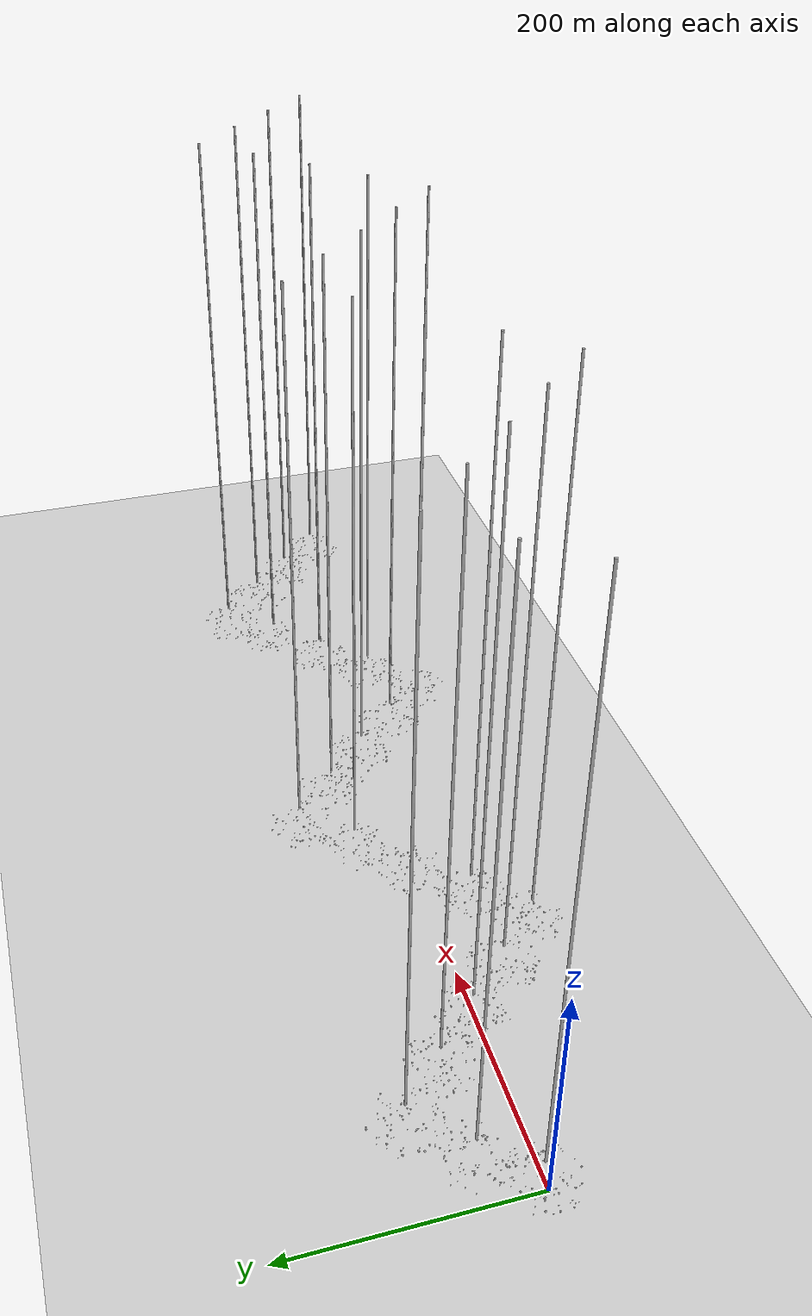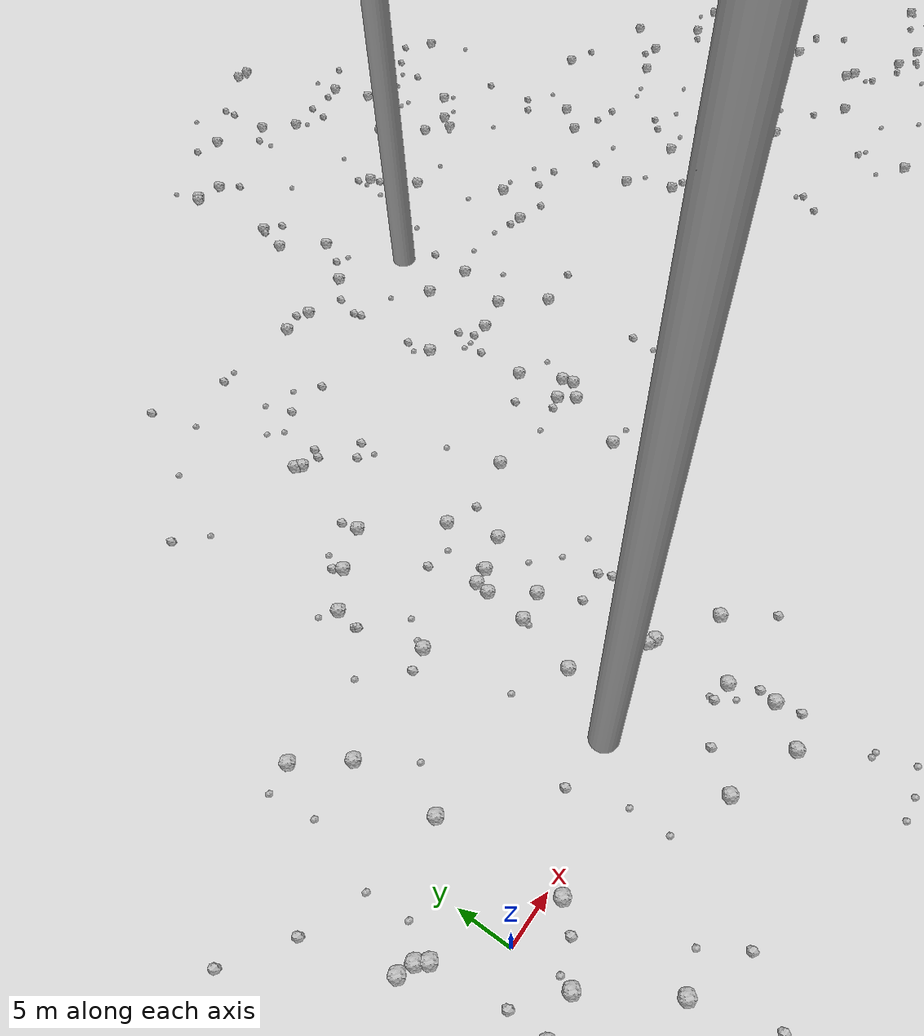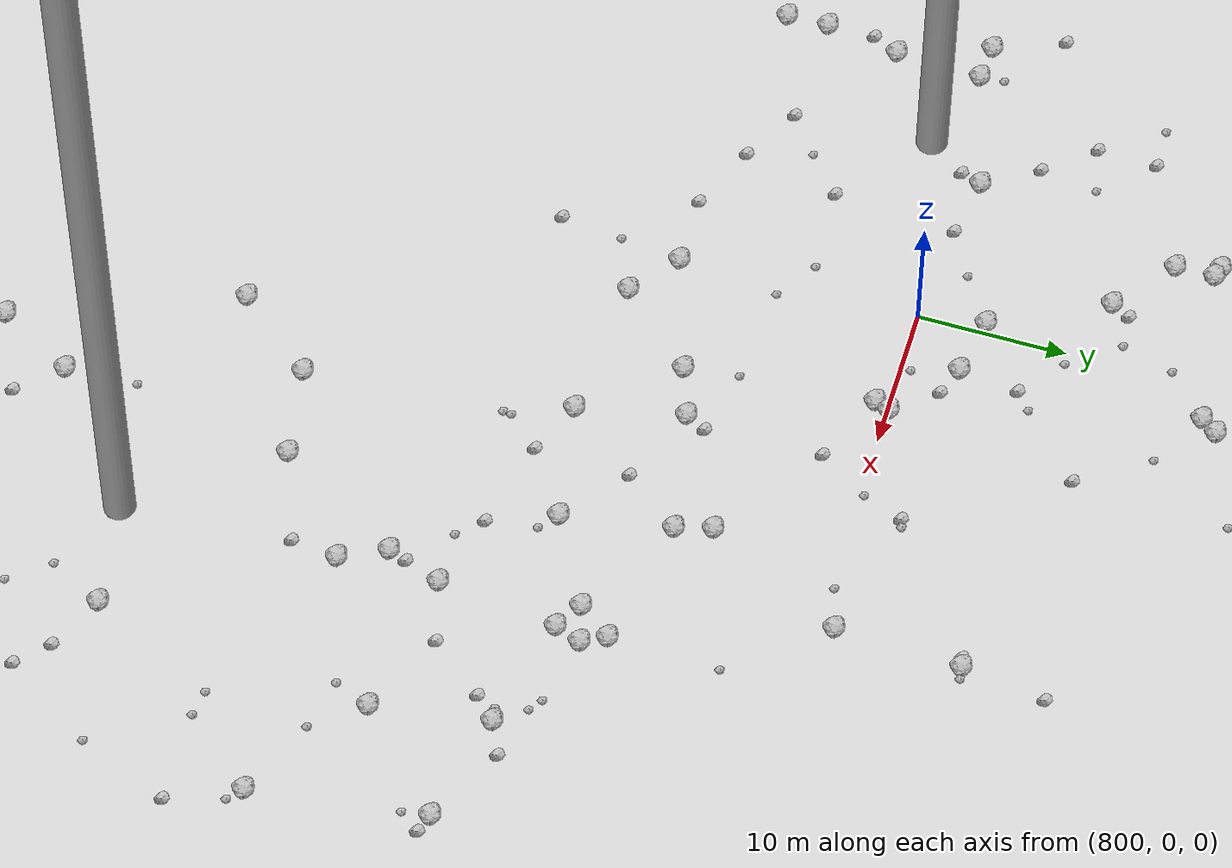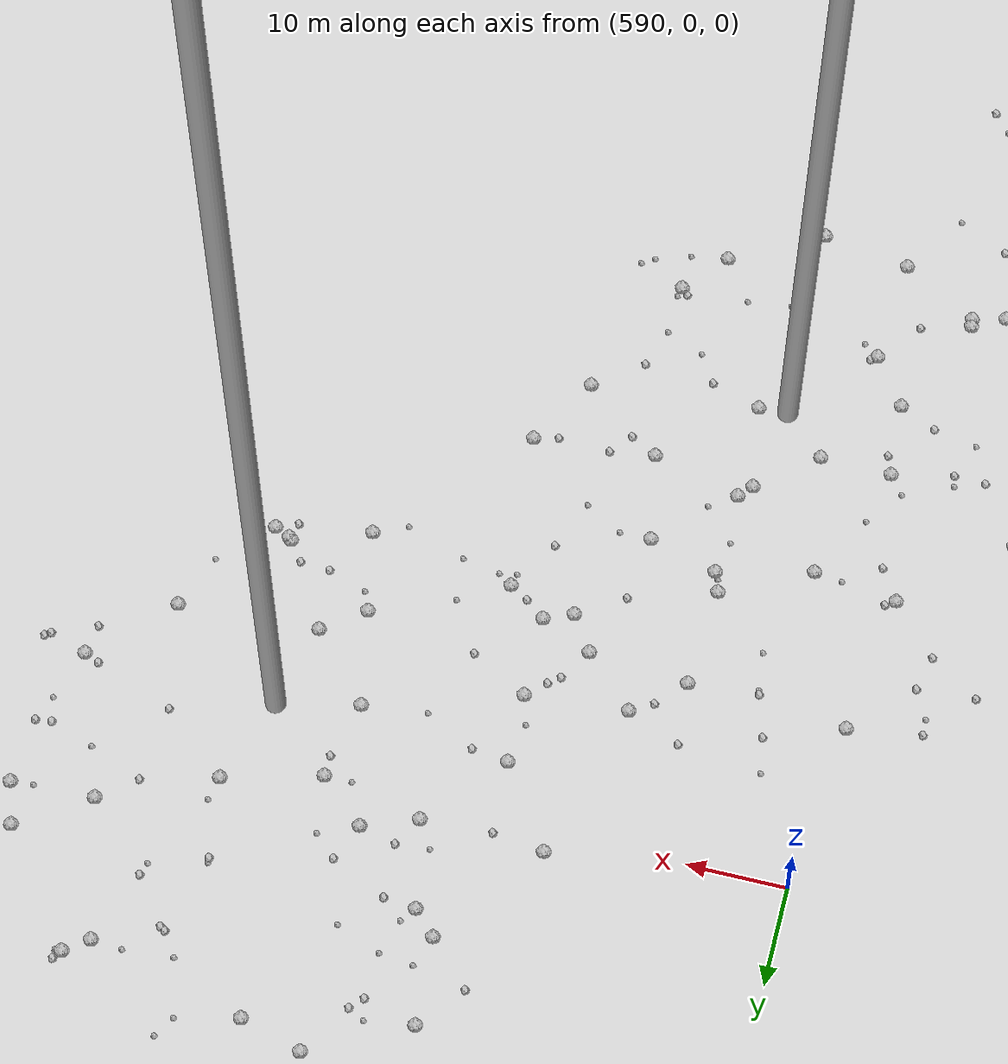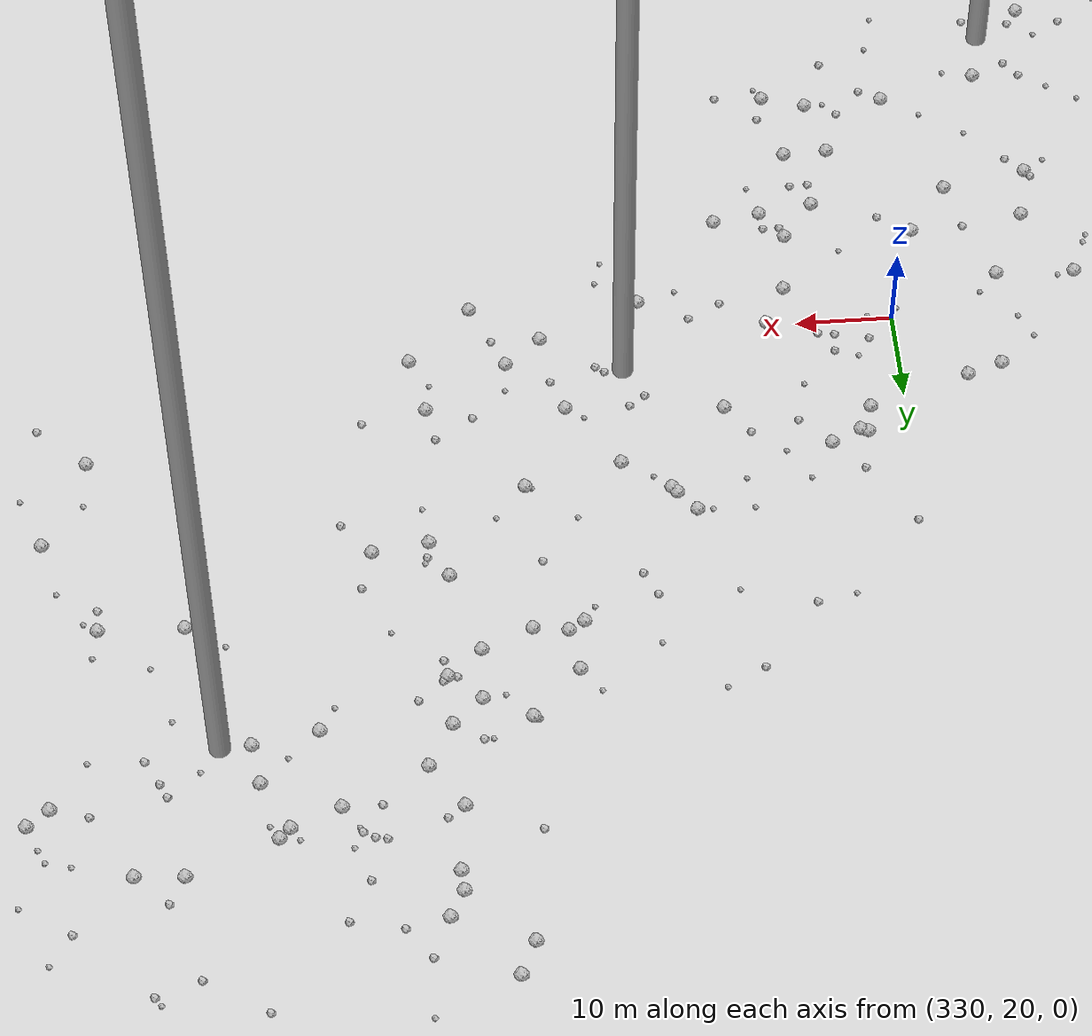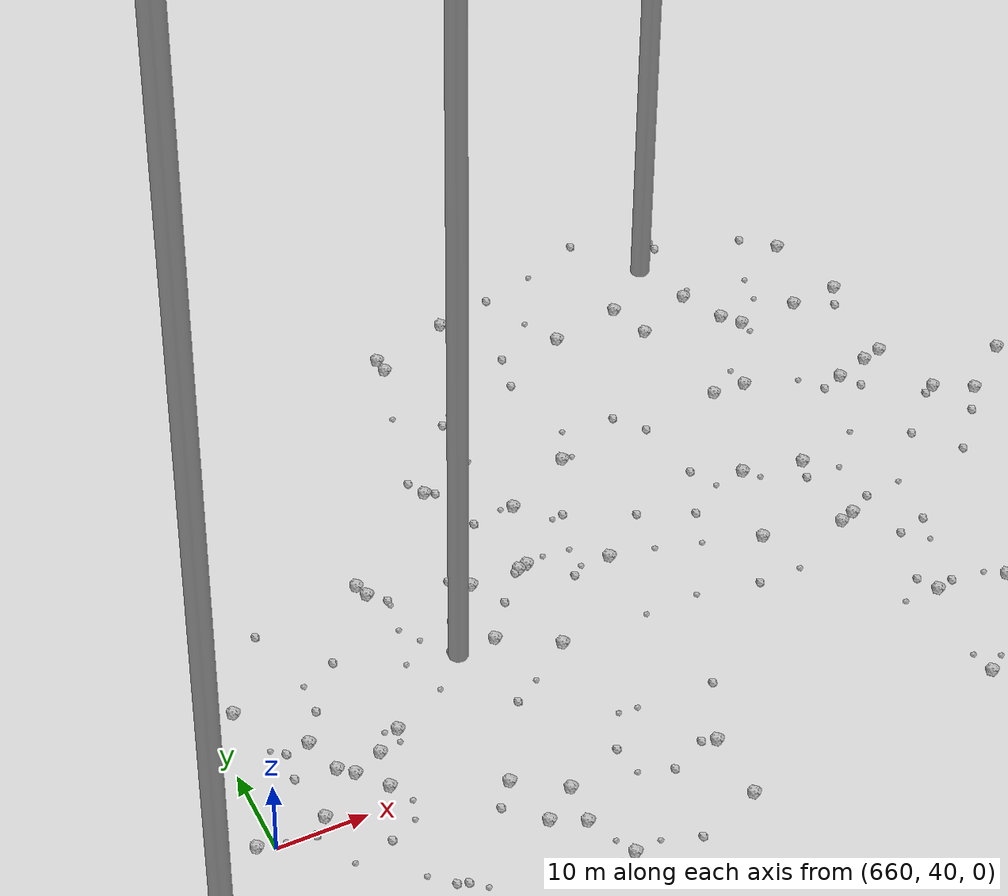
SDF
<sdf version="1.6">
 <world name="default">
  <include><uri>model://custom_ground</uri></include>
  <include><uri>model://sun</uri></include>
  <spherical_coordinates>
   <surface_model>EARTH_WGS84</surface_model>
   <latitude_deg>38.161479</latitude_deg>
   <longitude_deg>-122.454630</longitude_deg>
   <elevation>488.0</elevation>
   <heading_deg>90</heading_deg>
  </spherical_coordinates>
  <model name="rock1_0_0">
   <include><uri>model://rock1</uri><pose>22.308620223104214 9.26747592368821 0.5 0 0 0</pose></include>
  </model>
  <model name="rock1_0_1">
   <include><uri>model://rock1</uri><pose>4.562709222028513 -12.443384446380044 0.5 0 0 0</pose></include>
  </model>
  <model name="rock1_0_2">
   <include><uri>model://rock1</uri><pose>24.811328525167355 19.98973940357446 0.5 0 0 0</pose></include>
  </model>
  <model name="rock1_0_3">
   <include><uri>model://rock1</uri><pose>20.008870464836406 -8.090587868503892 0.5 0 0 0</pose></include>
  </model>
  <model name="rock1_0_4">
   <include><uri>model://rock1</uri><pose>29.470454110968937 4.356780229560499 0.5 0 0 0</pose></include>
  </model>
  <model name="rock1_0_5">
   <include><uri>model://rock1</uri><pose>16.444151759151417 21.254955831086896 0.5 0 0 0</pose></include>
  </model>
  <model name="rock1_0_6">
   <include><uri>model://rock1</uri><pose>27.441193810272722 6.542060844040272 0.5 0 0 0</pose></include>
  </model>
  <model name="rock1_0_7">
   <include><uri>model://rock1</uri><pose>-2.9822028394363436 -18.50982843856778 0.5 0 0 0</pose></include>
  </model>
  <model name="rock1_0_8">
   <include><uri>model://rock1</uri><pose>-16.56201720687895 -1.5163516792459788 0.5 0 0 0</pose></include>
  </model>
  <model name="rock1_0_9">
   <include><uri>model://rock1</uri><pose>-16.530783998350156 -12.092335569259326 0.5 0 0 0</pose></include>
  </model>
  <model name="rock1_0_10">
   <include><uri>model://rock1</uri><pose>-1.1012876928839717 -24.00537039598757 0.5 0 0 0</pose></include>
  </model>
  <model name="rock1_0_11">
   <include><uri>model://rock1</uri><pose>35.163526501504606 0.6184716903843572 0.5 0 0 0</pose></include>
  </model>
  <model name="rock1_0_12">
   <include><uri>model://rock1</uri><pose>-4.257730570879854 4.400440445822156 0.5 0 0 0</pose></include>
  </model>
  <model name="rock1_0_13">
   <include><uri>model://rock1</uri><pose>4.723110136697105 10.730525927355636 0.5 0 0 0</pose></include>
  </model>
  <model name="rock1_0_14">
   <include><uri>model://rock1</uri><pose>-6.360068208035969 5.76799929947844 0.5 0 0 0</pose></include>
  </model>
  <model name="rock1_0_15">
   <include><uri>model://rock1</uri><pose>28.7107455233144 4.729115519488744 0.5 0 0 0</pose></include>
  </model>
  <model name="rock1_0_16">
   <include><uri>model://rock1</uri><pose>5.287955324384686 -1.1939486858563733 0.5 0 0 0</pose></include>
  </model>
  <model name="rock1_0_17">
   <include><uri>model://rock1</uri><pose>0.11741777801728404 -5.321752076599356 0.5 0 0 0</pose></include>
  </model>
  <model name="rock1_0_18">
   <include><uri>model://rock1</uri><pose>-4.952026050579846 5.272826522183607 0.5 0 0 0</pose></include>
  </model>
  <model name="rock1_0_19">
   <include><uri>model://rock1</uri><pose>29.94336174089542 -7.479580578999805 0.5 0 0 0</pose></include>
  </model>
  <model name="rock1_0_20">
   <include><uri>model://rock1</uri><pose>11.147084034901372 -28.95110937901299 0.5 0 0 0</pose></include>
  </model>
  <model name="rock1_0_21">
   <include><uri>model://rock1</uri><pose>1.1920050839972731 23.755741985726623 0.5 0 0 0</pose></include>
  </model>
  <model name="rock1_0_22">
   <include><uri>model://rock1</uri><pose>-3.7432479727045482 -5.740278726342208 0.5 0 0 0</pose></include>
  </model>
  <model name="rock1_0_23">
   <include><uri>model://rock1</uri><pose>29.165776066680763 -3.224174789111018 0.5 0 0 0</pose></include>
  </model>
  <model name="rock1_0_24">
   <include><uri>model://rock1</uri><pose>26.854620622841296 -10.90775442842148 0.5 0 0 0</pose></include>
  </model>
  <model name="rock1_0_25">
   <include><uri>model://rock1</uri><pose>-13.900711147749242 8.191447904003972 0.5 0 0 0</pose></include>
  </model>
  <model name="rock1_0_26">
   <include><uri>model://rock1</uri><pose>4.567770396846768 19.39016596392149 0.5 0 0 0</pose></include>
  </model>
  <model name="rock2_0_0">
   <include><uri>model://rock2</uri><pose>30.2533708564413 -5.8881054527053 0.3 0 0 0</pose></include>
  </model>
  <model name="rock2_0_1">
   <include><uri>model://rock2</uri><pose>22.935777543572016 -4.816369977577438 0.3 0 0 0</pose></include>
  </model>
  <model name="rock2_0_2">
   <include><uri>model://rock2</uri><pose>14.69397805485147 27.730520868193338 0.3 0 0 0</pose></include>
  </model>
  <model name="rock2_0_3">
   <include><uri>model://rock2</uri><pose>6.4897586655811 -19.231469428955688 0.3 0 0 0</pose></include>
  </model>
  <model name="rock2_0_4">
   <include><uri>model://rock2</uri><pose>14.086981989050372 20.673280447721083 0.3 0 0 0</pose></include>
  </model>
  <model name="rock2_0_5">
   <include><uri>model://rock2</uri><pose>1.9721722087136158 -14.147955656649662 0.3 0 0 0</pose></include>
  </model>
  <model name="rock2_0_6">
   <include><uri>model://rock2</uri><pose>27.05174821746742 -2.9526014054589993 0.3 0 0 0</pose></include>
  </model>
  <model name="rock2_0_7">
   <include><uri>model://rock2</uri><pose>5.016824085041829 -18.701549802954837 0.3 0 0 0</pose></include>
  </model>
  <model name="rock2_0_8">
   <include><uri>model://rock2</uri><pose>10.162662157523648 -14.953208334670201 0.3 0 0 0</pose></include>
  </model>
  <model name="rock2_0_9">
   <include><uri>model://rock2</uri><pose>37.74074558881411 10.997839764058554 0.3 0 0 0</pose></include>
  </model>
  <model name="rock2_0_10">
   <include><uri>model://rock2</uri><pose>-17.233885184004887 3.6542566736223705 0.3 0 0 0</pose></include>
  </model>
  <model name="rock2_0_11">
   <include><uri>model://rock2</uri><pose>-13.62655181374857 -16.620854768918832 0.3 0 0 0</pose></include>
  </model>
  <model name="rock2_0_12">
   <include><uri>model://rock2</uri><pose>26.711938942056996 22.256227756666448 0.3 0 0 0</pose></include>
  </model>
  <model name="rock2_0_13">
   <include><uri>model://rock2</uri><pose>0.17015938325854307 -14.192471663121541 0.3 0 0 0</pose></include>
  </model>
  <model name="rock2_0_14">
   <include><uri>model://rock2</uri><pose>12.796785483927032 3.4365608689248432 0.3 0 0 0</pose></include>
  </model>
  <model name="rock2_0_15">
   <include><uri>model://rock2</uri><pose>-12.247872790719565 -2.1906554779789538 0.3 0 0 0</pose></include>
  </model>
  <model name="rock2_0_16">
   <include><uri>model://rock2</uri><pose>-3.568034473757681 -2.217047268998769 0.3 0 0 0</pose></include>
  </model>
  <model name="rock2_0_17">
   <include><uri>model://rock2</uri><pose>18.23534807301901 -26.76183472839397 0.3 0 0 0</pose></include>
  </model>
  <model name="rock2_0_18">
   <include><uri>model://rock2</uri><pose>-13.960352695234823 -14.028806909160709 0.3 0 0 0</pose></include>
  </model>
  <model name="rock2_0_19">
   <include><uri>model://rock2</uri><pose>30.270348449529223 -9.8574451921139 0.3 0 0 0</pose></include>
  </model>
  <model name="rock2_0_20">
   <include><uri>model://rock2</uri><pose>-11.308309938455904 -12.822765915465723 0.3 0 0 0</pose></include>
  </model>
  <model name="rock2_0_21">
   <include><uri>model://rock2</uri><pose>-13.774340450145209 17.202986008786233 0.3 0 0 0</pose></include>
  </model>
  <model name="rock2_0_22">
   <include><uri>model://rock2</uri><pose>-8.578581905736723 13.654939459167167 0.3 0 0 0</pose></include>
  </model>
  <model name="rock2_0_23">
   <include><uri>model://rock2</uri><pose>38.270993657163025 -3.8584984044349326 0.3 0 0 0</pose></include>
  </model>
  <model name="rock2_0_24">
   <include><uri>model://rock2</uri><pose>3.275502488908522 -3.2360365315144115 0.3 0 0 0</pose></include>
  </model>
  <model name="rock2_0_25">
   <include><uri>model://rock2</uri><pose>29.238032917530383 12.126386647046026 0.3 0 0 0</pose></include>
  </model>
  <model name="rock2_0_26">
   <include><uri>model://rock2</uri><pose>32.699692116814475 12.536044358993209 0.3 0 0 0</pose></include>
  </model>
  <model name="rock3_0_0">
   <include><uri>model://rock3</uri><pose>26.339779061743563 -20.87643342858989 0.2 0 0 0</pose></include>
  </model>
  <model name="rock3_0_1">
   <include><uri>model://rock3</uri><pose>14.268697191161152 -5.686227768458814 0.2 0 0 0</pose></include>
  </model>
  <model name="rock3_0_2">
   <include><uri>model://rock3</uri><pose>18.313080672262124 24.19514584638972 0.2 0 0 0</pose></include>
  </model>
  <model name="rock3_0_3">
   <include><uri>model://rock3</uri><pose>0.510087046909419 -4.102163464911062 0.2 0 0 0</pose></include>
  </model>
  <model name="rock3_0_4">
   <include><uri>model://rock3</uri><pose>27.212604149788028 16.149870492937133 0.2 0 0 0</pose></include>
  </model>
  <model name="rock3_0_5">
   <include><uri>model://rock3</uri><pose>14.357524419121042 -1.8383093050265344 0.2 0 0 0</pose></include>
  </model>
  <model name="rock3_0_6">
   <include><uri>model://rock3</uri><pose>31.398113162008258 -19.955635350931352 0.2 0 0 0</pose></include>
  </model>
  <model name="rock3_0_7">
   <include><uri>model://rock3</uri><pose>16.83361836040531 22.264365480721366 0.2 0 0 0</pose></include>
  </model>
  <model name="rock3_0_8">
   <include><uri>model://rock3</uri><pose>28.99519655461924 4.098234992048951 0.2 0 0 0</pose></include>
  </model>
  <model name="rock3_0_9">
   <include><uri>model://rock3</uri><pose>10.42737739412581 24.39211708817001 0.2 0 0 0</pose></include>
  </model>
  <model name="rock3_0_10">
   <include><uri>model://rock3</uri><pose>28.202101736493987 -4.596706770136617 0.2 0 0 0</pose></include>
  </model>
  <model name="rock3_0_11">
   <include><uri>model://rock3</uri><pose>17.314719671927364 12.052566872389306 0.2 0 0 0</pose></include>
  </model>
  <model name="rock3_0_12">
   <include><uri>model://rock3</uri><pose>-1.6894297277103192 23.240631320085143 0.2 0 0 0</pose></include>
  </model>
  <model name="rock3_0_13">
   <include><uri>model://rock3</uri><pose>27.166843686270504 -2.484899225487265 0.2 0 0 0</pose></include>
  </model>
  <model name="rock3_0_14">
   <include><uri>model://rock3</uri><pose>24.56665842643298 5.215732299296377 0.2 0 0 0</pose></include>
  </model>
  <model name="rock3_0_15">
   <include><uri>model://rock3</uri><pose>-14.33847927480167 13.753372977871528 0.2 0 0 0</pose></include>
  </model>
  <model name="rock3_0_16">
   <include><uri>model://rock3</uri><pose>30.56490252784939 -16.578011458108495 0.2 0 0 0</pose></include>
  </model>
  <model name="rock3_0_17">
   <include><uri>model://rock3</uri><pose>29.960923798074518 -16.462116162832345 0.2 0 0 0</pose></include>
  </model>
  <model name="rock3_0_18">
   <include><uri>model://rock3</uri><pose>-1.1417343725686422 18.717637223608953 0.2 0 0 0</pose></include>
  </model>
  <model name="rock3_0_19">
   <include><uri>model://rock3</uri><pose>-2.3225031511827865 -22.056190964784374 0.2 0 0 0</pose></include>
  </model>
  <model name="rock3_0_20">
   <include><uri>model://rock3</uri><pose>7.941604796566256 -11.41917086000845 0.2 0 0 0</pose></include>
  </model>
  <model name="rock3_0_21">
   <include><uri>model://rock3</uri><pose>-12.523045423025938 -10.631419660339827 0.2 0 0 0</pose></include>
  </model>
  <model name="rock3_0_22">
   <include><uri>model://rock3</uri><pose>-3.154331251079711 11.52448634905705 0.2 0 0 0</pose></include>
  </model>
  <model name="rock3_0_23">
   <include><uri>model://rock3</uri><pose>28.658433722484844 -20.740941189679845 0.2 0 0 0</pose></include>
  </model>
  <model name="rock3_0_24">
   <include><uri>model://rock3</uri><pose>29.946131264927374 18.78979699231769 0.2 0 0 0</pose></include>
  </model>
  <model name="rock3_0_25">
   <include><uri>model://rock3</uri><pose>-2.877628558218447 7.4890763916232 0.2 0 0 0</pose></include>
  </model>
  <model name="rock3_0_26">
   <include><uri>model://rock3</uri><pose>7.6463522551676135 14.655072734698038 0.2 0 0 0</pose></include>
  </model>
  <model name="rock1_1_0">
   <include><uri>model://rock1</uri><pose>25.062459308294358 21.445883524141706 0.5 0 0 0</pose></include>
  </model>
  <model name="rock1_1_1">
   <include><uri>model://rock1</uri><pose>45.220495841822725 61.465925893851285 0.5 0 0 0</pose></include>
  </model>
  <model name="rock1_1_2">
   <include><uri>model://rock1</uri><pose>51.58339933286234 27.055729752869492 0.5 0 0 0</pose></include>
  </model>
  <model name="rock1_1_3">
   <include><uri>model://rock1</uri><pose>38.83323779714219 28.463421792241313 0.5 0 0 0</pose></include>
  </model>
  <model name="rock1_1_4">
   <include><uri>model://rock1</uri><pose>53.23422004991139 29.94967095823342 0.5 0 0 0</pose></include>
  </model>
  <model name="rock1_1_5">
   <include><uri>model://rock1</uri><pose>24.27494438307847 15.53494168653917 0.5 0 0 0</pose></include>
  </model>
  <model name="rock1_1_6">
   <include><uri>model://rock1</uri><pose>60.05552443347485 43.802367199902434 0.5 0 0 0</pose></include>
  </model>
  <model name="rock1_1_7">
   <include><uri>model://rock1</uri><pose>27.428490060580227 16.080816882399994 0.5 0 0 0</pose></include>
  </model>
  <model name="rock1_1_8">
   <include><uri>model://rock1</uri><pose>62.436391297213305 50.640141384520525 0.5 0 0 0</pose></include>
  </model>
  <model name="rock1_1_9">
   <include><uri>model://rock1</uri><pose>56.80625572611462 51.91580656438584 0.5 0 0 0</pose></include>
  </model>
  <model name="rock1_1_10">
   <include><uri>model://rock1</uri><pose>26.834727061811392 21.742232176224984 0.5 0 0 0</pose></include>
  </model>
  <model name="rock1_1_11">
   <include><uri>model://rock1</uri><pose>15.060804535043102 30.276581574947837 0.5 0 0 0</pose></include>
  </model>
  <model name="rock1_1_12">
   <include><uri>model://rock1</uri><pose>30.68096954124893 22.98960429170543 0.5 0 0 0</pose></include>
  </model>
  <model name="rock1_1_13">
   <include><uri>model://rock1</uri><pose>63.94275347091627 38.9916563421006 0.5 0 0 0</pose></include>
  </model>
  <model name="rock1_1_14">
   <include><uri>model://rock1</uri><pose>41.447716716750406 61.504469652433876 0.5 0 0 0</pose></include>
  </model>
  <model name="rock1_1_15">
   <include><uri>model://rock1</uri><pose>23.482677370580888 35.12559074806647 0.5 0 0 0</pose></include>
  </model>
  <model name="rock1_1_16">
   <include><uri>model://rock1</uri><pose>52.167581767584316 62.69238561728281 0.5 0 0 0</pose></include>
  </model>
  <model name="rock1_1_17">
   <include><uri>model://rock1</uri><pose>55.54263107528065 42.53040075671679 0.5 0 0 0</pose></include>
  </model>
  <model name="rock1_1_18">
   <include><uri>model://rock1</uri><pose>25.916936232618596 45.84016245943496 0.5 0 0 0</pose></include>
  </model>
  <model name="rock1_1_19">
   <include><uri>model://rock1</uri><pose>53.46473849341485 28.660588386957194 0.5 0 0 0</pose></include>
  </model>
  <model name="rock1_1_20">
   <include><uri>model://rock1</uri><pose>50.41942640917965 28.81364607553425 0.5 0 0 0</pose></include>
  </model>
  <model name="rock1_1_21">
   <include><uri>model://rock1</uri><pose>18.92317755167638 33.07262130178564 0.5 0 0 0</pose></include>
  </model>
  <model name="rock1_1_22">
   <include><uri>model://rock1</uri><pose>51.16717338599356 34.54131212120039 0.5 0 0 0</pose></include>
  </model>
  <model name="rock1_1_23">
   <include><uri>model://rock1</uri><pose>26.47580939292887 45.35415633934926 0.5 0 0 0</pose></include>
  </model>
  <model name="rock1_1_24">
   <include><uri>model://rock1</uri><pose>48.3444459383706 45.29622440039094 0.5 0 0 0</pose></include>
  </model>
  <model name="rock1_1_25">
   <include><uri>model://rock1</uri><pose>48.15599821837466 20.185267371113394 0.5 0 0 0</pose></include>
  </model>
  <model name="rock1_1_26">
   <include><uri>model://rock1</uri><pose>29.22715449957834 28.225733121533544 0.5 0 0 0</pose></include>
  </model>
  <model name="rock2_1_0">
   <include><uri>model://rock2</uri><pose>22.66247820709901 64.44129221471712 0.3 0 0 0</pose></include>
  </model>
  <model name="rock2_1_1">
   <include><uri>model://rock2</uri><pose>36.61369777960151 51.775816506734515 0.3 0 0 0</pose></include>
  </model>
  <model name="rock2_1_2">
   <include><uri>model://rock2</uri><pose>32.59237721065659 27.081410595003828 0.3 0 0 0</pose></include>
  </model>
  <model name="rock2_1_3">
   <include><uri>model://rock2</uri><pose>63.916694577037575 26.94727292125008 0.3 0 0 0</pose></include>
  </model>
  <model name="rock2_1_4">
   <include><uri>model://rock2</uri><pose>53.50060030679946 42.72649334154226 0.3 0 0 0</pose></include>
  </model>
  <model name="rock2_1_5">
   <include><uri>model://rock2</uri><pose>69.44549580693806 39.74720897892632 0.3 0 0 0</pose></include>
  </model>
  <model name="rock2_1_6">
   <include><uri>model://rock2</uri><pose>18.35537069031878 34.02221365571936 0.3 0 0 0</pose></include>
  </model>
  <model name="rock2_1_7">
   <include><uri>model://rock2</uri><pose>11.639715855808943 49.34271655992385 0.3 0 0 0</pose></include>
  </model>
  <model name="rock2_1_8">
   <include><uri>model://rock2</uri><pose>14.532935124538703 27.876926224391788 0.3 0 0 0</pose></include>
  </model>
  <model name="rock2_1_9">
   <include><uri>model://rock2</uri><pose>30.701336624971624 41.47383729159468 0.3 0 0 0</pose></include>
  </model>
  <model name="rock2_1_10">
   <include><uri>model://rock2</uri><pose>49.31537231777764 60.05009385284363 0.3 0 0 0</pose></include>
  </model>
  <model name="rock2_1_11">
   <include><uri>model://rock2</uri><pose>51.54190135450443 40.29994122560394 0.3 0 0 0</pose></include>
  </model>
  <model name="rock2_1_12">
   <include><uri>model://rock2</uri><pose>28.36308808665176 44.934202968605 0.3 0 0 0</pose></include>
  </model>
  <model name="rock2_1_13">
   <include><uri>model://rock2</uri><pose>43.9483127946297 62.463926487960585 0.3 0 0 0</pose></include>
  </model>
  <model name="rock2_1_14">
   <include><uri>model://rock2</uri><pose>47.17994110012332 32.37603854603298 0.3 0 0 0</pose></include>
  </model>
  <model name="rock2_1_15">
   <include><uri>model://rock2</uri><pose>32.561930993228536 42.47628892809591 0.3 0 0 0</pose></include>
  </model>
  <model name="rock2_1_16">
   <include><uri>model://rock2</uri><pose>48.29741443643493 57.056938078658476 0.3 0 0 0</pose></include>
  </model>
  <model name="rock2_1_17">
   <include><uri>model://rock2</uri><pose>52.8205658817552 44.53418168222239 0.3 0 0 0</pose></include>
  </model>
  <model name="rock2_1_18">
   <include><uri>model://rock2</uri><pose>30.80260632119881 61.45576516498793 0.3 0 0 0</pose></include>
  </model>
  <model name="rock2_1_19">
   <include><uri>model://rock2</uri><pose>48.81460298279103 28.4159528303934 0.3 0 0 0</pose></include>
  </model>
  <model name="rock2_1_20">
   <include><uri>model://rock2</uri><pose>31.727732506210526 51.85471475066865 0.3 0 0 0</pose></include>
  </model>
  <model name="rock2_1_21">
   <include><uri>model://rock2</uri><pose>23.914346600156723 26.59816501003831 0.3 0 0 0</pose></include>
  </model>
  <model name="rock2_1_22">
   <include><uri>model://rock2</uri><pose>47.99198103171277 48.38056653753067 0.3 0 0 0</pose></include>
  </model>
  <model name="rock2_1_23">
   <include><uri>model://rock2</uri><pose>23.139619796995678 36.99116012633245 0.3 0 0 0</pose></include>
  </model>
  <model name="rock2_1_24">
   <include><uri>model://rock2</uri><pose>48.49802220375991 56.10890971592548 0.3 0 0 0</pose></include>
  </model>
  <model name="rock2_1_25">
   <include><uri>model://rock2</uri><pose>33.205519095956866 11.26157440428491 0.3 0 0 0</pose></include>
  </model>
  <model name="rock2_1_26">
   <include><uri>model://rock2</uri><pose>28.955804796225326 45.94495014560594 0.3 0 0 0</pose></include>
  </model>
  <model name="rock3_1_0">
   <include><uri>model://rock3</uri><pose>29.00164152242248 50.41705301667357 0.2 0 0 0</pose></include>
  </model>
  <model name="rock3_1_1">
   <include><uri>model://rock3</uri><pose>26.56365195137822 26.142437591060194 0.2 0 0 0</pose></include>
  </model>
  <model name="rock3_1_2">
   <include><uri>model://rock3</uri><pose>37.36054003942821 34.51985853145143 0.2 0 0 0</pose></include>
  </model>
  <model name="rock3_1_3">
   <include><uri>model://rock3</uri><pose>32.53928134192662 61.62698926146876 0.2 0 0 0</pose></include>
  </model>
  <model name="rock3_1_4">
   <include><uri>model://rock3</uri><pose>64.88235593273612 46.520434963910496 0.2 0 0 0</pose></include>
  </model>
  <model name="rock3_1_5">
   <include><uri>model://rock3</uri><pose>35.7446733589106 15.573382565505334 0.2 0 0 0</pose></include>
  </model>
  <model name="rock3_1_6">
   <include><uri>model://rock3</uri><pose>50.628211333018264 20.026559878023505 0.2 0 0 0</pose></include>
  </model>
  <model name="rock3_1_7">
   <include><uri>model://rock3</uri><pose>24.057592024282513 58.92025946803498 0.2 0 0 0</pose></include>
  </model>
  <model name="rock3_1_8">
   <include><uri>model://rock3</uri><pose>45.2397615173693 27.67049422940169 0.2 0 0 0</pose></include>
  </model>
  <model name="rock3_1_9">
   <include><uri>model://rock3</uri><pose>32.42030945568261 16.439940766340353 0.2 0 0 0</pose></include>
  </model>
  <model name="rock3_1_10">
   <include><uri>model://rock3</uri><pose>30.705678726490255 54.88265632232265 0.2 0 0 0</pose></include>
  </model>
  <model name="rock3_1_11">
   <include><uri>model://rock3</uri><pose>32.157330431561505 40.3054216116213 0.2 0 0 0</pose></include>
  </model>
  <model name="rock3_1_12">
   <include><uri>model://rock3</uri><pose>19.362841978242894 35.3753796571163 0.2 0 0 0</pose></include>
  </model>
  <model name="rock3_1_13">
   <include><uri>model://rock3</uri><pose>49.58358629362233 13.676899236972613 0.2 0 0 0</pose></include>
  </model>
  <model name="rock3_1_14">
   <include><uri>model://rock3</uri><pose>27.668301403406947 51.73076956645752 0.2 0 0 0</pose></include>
  </model>
  <model name="rock3_1_15">
   <include><uri>model://rock3</uri><pose>52.21578589128355 42.284319221854346 0.2 0 0 0</pose></include>
  </model>
  <model name="rock3_1_16">
   <include><uri>model://rock3</uri><pose>14.39239851251136 46.69597635177654 0.2 0 0 0</pose></include>
  </model>
  <model name="rock3_1_17">
   <include><uri>model://rock3</uri><pose>13.422851550634435 31.415815518189806 0.2 0 0 0</pose></include>
  </model>
  <model name="rock3_1_18">
   <include><uri>model://rock3</uri><pose>18.10475625481547 55.21372470174398 0.2 0 0 0</pose></include>
  </model>
  <model name="rock3_1_19">
   <include><uri>model://rock3</uri><pose>34.19151075171443 53.91285174420677 0.2 0 0 0</pose></include>
  </model>
  <model name="rock3_1_20">
   <include><uri>model://rock3</uri><pose>47.23271127818354 46.90849084839214 0.2 0 0 0</pose></include>
  </model>
  <model name="rock3_1_21">
   <include><uri>model://rock3</uri><pose>63.53823598165451 23.97942588101091 0.2 0 0 0</pose></include>
  </model>
  <model name="rock3_1_22">
   <include><uri>model://rock3</uri><pose>51.11235089919764 42.35991622247832 0.2 0 0 0</pose></include>
  </model>
  <model name="rock3_1_23">
   <include><uri>model://rock3</uri><pose>54.72366264594391 33.03669593733234 0.2 0 0 0</pose></include>
  </model>
  <model name="rock3_1_24">
   <include><uri>model://rock3</uri><pose>24.06487249251827 14.75186153329602 0.2 0 0 0</pose></include>
  </model>
  <model name="rock3_1_25">
   <include><uri>model://rock3</uri><pose>53.18198116962114 55.2474606824161 0.2 0 0 0</pose></include>
  </model>
  <model name="rock3_1_26">
   <include><uri>model://rock3</uri><pose>66.66254715455193 52.42995301349087 0.2 0 0 0</pose></include>
  </model>
  <model name="rock1_2_0">
   <include><uri>model://rock1</uri><pose>85.64415625179186 75.2097252782191 0.5 0 0 0</pose></include>
  </model>
  <model name="rock1_2_1">
   <include><uri>model://rock1</uri><pose>88.55833098137943 72.89063091831113 0.5 0 0 0</pose></include>
  </model>
  <model name="rock1_2_2">
   <include><uri>model://rock1</uri><pose>74.32832824164392 67.72319041863474 0.5 0 0 0</pose></include>
  </model>
  <model name="rock1_2_3">
   <include><uri>model://rock1</uri><pose>75.7774064473125 51.39044993901757 0.5 0 0 0</pose></include>
  </model>
  <model name="rock1_2_4">
   <include><uri>model://rock1</uri><pose>90.07342600824495 75.00285884524098 0.5 0 0 0</pose></include>
  </model>
  <model name="rock1_2_5">
   <include><uri>model://rock1</uri><pose>57.84824445915868 89.64152748779327 0.5 0 0 0</pose></include>
  </model>
  <model name="rock1_2_6">
   <include><uri>model://rock1</uri><pose>98.74505345908204 57.4277133747258 0.5 0 0 0</pose></include>
  </model>
  <model name="rock1_2_7">
   <include><uri>model://rock1</uri><pose>56.66694927175937 68.83616113202434 0.5 0 0 0</pose></include>
  </model>
  <model name="rock1_2_8">
   <include><uri>model://rock1</uri><pose>71.28719319794531 73.64609587259712 0.5 0 0 0</pose></include>
  </model>
  <model name="rock1_2_9">
   <include><uri>model://rock1</uri><pose>94.59694423647036 78.51819862819782 0.5 0 0 0</pose></include>
  </model>
  <model name="rock1_2_10">
   <include><uri>model://rock1</uri><pose>82.8561792892193 109.03963558845007 0.5 0 0 0</pose></include>
  </model>
  <model name="rock1_2_11">
   <include><uri>model://rock1</uri><pose>70.20734091492679 67.22125919513812 0.5 0 0 0</pose></include>
  </model>
  <model name="rock1_2_12">
   <include><uri>model://rock1</uri><pose>102.59688635395206 61.26829437321847 0.5 0 0 0</pose></include>
  </model>
  <model name="rock1_2_13">
   <include><uri>model://rock1</uri><pose>81.87851389028339 80.85913458513346 0.5 0 0 0</pose></include>
  </model>
  <model name="rock1_2_14">
   <include><uri>model://rock1</uri><pose>88.24082222833209 88.45122689175416 0.5 0 0 0</pose></include>
  </model>
  <model name="rock1_2_15">
   <include><uri>model://rock1</uri><pose>107.08186739270491 90.7566973668132 0.5 0 0 0</pose></include>
  </model>
  <model name="rock1_2_16">
   <include><uri>model://rock1</uri><pose>53.97485784335842 89.64362922656366 0.5 0 0 0</pose></include>
  </model>
  <model name="rock1_2_17">
   <include><uri>model://rock1</uri><pose>54.30839016167137 77.74858321874936 0.5 0 0 0</pose></include>
  </model>
  <model name="rock1_2_18">
   <include><uri>model://rock1</uri><pose>79.74874910581181 56.92995789321984 0.5 0 0 0</pose></include>
  </model>
  <model name="rock1_2_19">
   <include><uri>model://rock1</uri><pose>65.74422270714992 98.05756763395368 0.5 0 0 0</pose></include>
  </model>
  <model name="rock1_2_20">
   <include><uri>model://rock1</uri><pose>81.01017143736009 108.97987688265638 0.5 0 0 0</pose></include>
  </model>
  <model name="rock1_2_21">
   <include><uri>model://rock1</uri><pose>84.51484617784791 81.04472612570319 0.5 0 0 0</pose></include>
  </model>
  <model name="rock1_2_22">
   <include><uri>model://rock1</uri><pose>52.83908460328815 73.49624923858971 0.5 0 0 0</pose></include>
  </model>
  <model name="rock1_2_23">
   <include><uri>model://rock1</uri><pose>72.37987035600729 95.48969431379277 0.5 0 0 0</pose></include>
  </model>
  <model name="rock1_2_24">
   <include><uri>model://rock1</uri><pose>86.92756120879532 93.95829990561907 0.5 0 0 0</pose></include>
  </model>
  <model name="rock1_2_25">
   <include><uri>model://rock1</uri><pose>54.49678474415324 90.20514733871552 0.5 0 0 0</pose></include>
  </model>
  <model name="rock1_2_26">
   <include><uri>model://rock1</uri><pose>75.87024869093301 91.97373279862502 0.5 0 0 0</pose></include>
  </model>
  <model name="rock2_2_0">
   <include><uri>model://rock2</uri><pose>72.62341049009466 101.71751180234614 0.3 0 0 0</pose></include>
  </model>
  <model name="rock2_2_1">
   <include><uri>model://rock2</uri><pose>70.14775632060622 75.03269089031492 0.3 0 0 0</pose></include>
  </model>
  <model name="rock2_2_2">
   <include><uri>model://rock2</uri><pose>62.47617077581886 61.253119656673256 0.3 0 0 0</pose></include>
  </model>
  <model name="rock2_2_3">
   <include><uri>model://rock2</uri><pose>83.79461094658748 53.79645572178545 0.3 0 0 0</pose></include>
  </model>
  <model name="rock2_2_4">
   <include><uri>model://rock2</uri><pose>84.61738618113161 93.54129791789744 0.3 0 0 0</pose></include>
  </model>
  <model name="rock2_2_5">
   <include><uri>model://rock2</uri><pose>72.64907377432128 103.56758178271424 0.3 0 0 0</pose></include>
  </model>
  <model name="rock2_2_6">
   <include><uri>model://rock2</uri><pose>87.64291614259429 53.85213876843786 0.3 0 0 0</pose></include>
  </model>
  <model name="rock2_2_7">
   <include><uri>model://rock2</uri><pose>56.30634223628431 76.49292134884286 0.3 0 0 0</pose></include>
  </model>
  <model name="rock2_2_8">
   <include><uri>model://rock2</uri><pose>62.3224084628505 98.83894994470089 0.3 0 0 0</pose></include>
  </model>
  <model name="rock2_2_9">
   <include><uri>model://rock2</uri><pose>101.83744733279765 74.94536579758167 0.3 0 0 0</pose></include>
  </model>
  <model name="rock2_2_10">
   <include><uri>model://rock2</uri><pose>99.2364149641142 66.17311608982365 0.3 0 0 0</pose></include>
  </model>
  <model name="rock2_2_11">
   <include><uri>model://rock2</uri><pose>53.88069580804928 77.31219092828792 0.3 0 0 0</pose></include>
  </model>
  <model name="rock2_2_12">
   <include><uri>model://rock2</uri><pose>79.89243381384176 90.31664323537717 0.3 0 0 0</pose></include>
  </model>
  <model name="rock2_2_13">
   <include><uri>model://rock2</uri><pose>99.46207954045288 91.0390766919902 0.3 0 0 0</pose></include>
  </model>
  <model name="rock2_2_14">
   <include><uri>model://rock2</uri><pose>97.35608008228544 86.03824127651747 0.3 0 0 0</pose></include>
  </model>
  <model name="rock2_2_15">
   <include><uri>model://rock2</uri><pose>69.61365367556122 93.58907850253829 0.3 0 0 0</pose></include>
  </model>
  <model name="rock2_2_16">
   <include><uri>model://rock2</uri><pose>85.9974244605556 82.33633281824967 0.3 0 0 0</pose></include>
  </model>
  <model name="rock2_2_17">
   <include><uri>model://rock2</uri><pose>74.01348091860508 51.79017623396476 0.3 0 0 0</pose></include>
  </model>
  <model name="rock2_2_18">
   <include><uri>model://rock2</uri><pose>79.786649489654 50.80302109404221 0.3 0 0 0</pose></include>
  </model>
  <model name="rock2_2_19">
   <include><uri>model://rock2</uri><pose>54.6861941779495 65.49766516299387 0.3 0 0 0</pose></include>
  </model>
  <model name="rock2_2_20">
   <include><uri>model://rock2</uri><pose>101.68772515688744 67.87678625121916 0.3 0 0 0</pose></include>
  </model>
  <model name="rock2_2_21">
   <include><uri>model://rock2</uri><pose>71.63517631705811 72.4657958169483 0.3 0 0 0</pose></include>
  </model>
  <model name="rock2_2_22">
   <include><uri>model://rock2</uri><pose>63.07845195759889 55.98104064673582 0.3 0 0 0</pose></include>
  </model>
  <model name="rock2_2_23">
   <include><uri>model://rock2</uri><pose>103.67986277848179 93.59058924326014 0.3 0 0 0</pose></include>
  </model>
  <model name="rock2_2_24">
   <include><uri>model://rock2</uri><pose>80.70661989463102 93.20444820099317 0.3 0 0 0</pose></include>
  </model>
  <model name="rock2_2_25">
   <include><uri>model://rock2</uri><pose>59.56943205254788 87.58972361117586 0.3 0 0 0</pose></include>
  </model>
  <model name="rock2_2_26">
   <include><uri>model://rock2</uri><pose>91.83128743600037 97.69331206576223 0.3 0 0 0</pose></include>
  </model>
  <model name="rock3_2_0">
   <include><uri>model://rock3</uri><pose>56.234228540230696 64.8654200211545 0.2 0 0 0</pose></include>
  </model>
  <model name="rock3_2_1">
   <include><uri>model://rock3</uri><pose>73.22192494738098 80.34043295715159 0.2 0 0 0</pose></include>
  </model>
  <model name="rock3_2_2">
   <include><uri>model://rock3</uri><pose>89.29970536223195 82.79373024820556 0.2 0 0 0</pose></include>
  </model>
  <model name="rock3_2_3">
   <include><uri>model://rock3</uri><pose>92.42702100521353 75.20534705442763 0.2 0 0 0</pose></include>
  </model>
  <model name="rock3_2_4">
   <include><uri>model://rock3</uri><pose>79.65500472297039 67.91102542683691 0.2 0 0 0</pose></include>
  </model>
  <model name="rock3_2_5">
   <include><uri>model://rock3</uri><pose>87.7899769413153 72.46804070568369 0.2 0 0 0</pose></include>
  </model>
  <model name="rock3_2_6">
   <include><uri>model://rock3</uri><pose>69.36616888109985 70.39540393020644 0.2 0 0 0</pose></include>
  </model>
  <model name="rock3_2_7">
   <include><uri>model://rock3</uri><pose>75.57403163704575 59.89946191358858 0.2 0 0 0</pose></include>
  </model>
  <model name="rock3_2_8">
   <include><uri>model://rock3</uri><pose>63.58897725516708 81.5263381702191 0.2 0 0 0</pose></include>
  </model>
  <model name="rock3_2_9">
   <include><uri>model://rock3</uri><pose>93.5289774227666 86.91653143859659 0.2 0 0 0</pose></include>
  </model>
  <model name="rock3_2_10">
   <include><uri>model://rock3</uri><pose>109.079684616961 85.32129404846197 0.2 0 0 0</pose></include>
  </model>
  <model name="rock3_2_11">
   <include><uri>model://rock3</uri><pose>95.70056619817652 77.7148370154886 0.2 0 0 0</pose></include>
  </model>
  <model name="rock3_2_12">
   <include><uri>model://rock3</uri><pose>68.00238406391313 104.95497257674634 0.2 0 0 0</pose></include>
  </model>
  <model name="rock3_2_13">
   <include><uri>model://rock3</uri><pose>105.28373721853508 65.60818160784108 0.2 0 0 0</pose></include>
  </model>
  <model name="rock3_2_14">
   <include><uri>model://rock3</uri><pose>96.77936528749055 88.57263429080461 0.2 0 0 0</pose></include>
  </model>
  <model name="rock3_2_15">
   <include><uri>model://rock3</uri><pose>71.38565689450402 52.48444931094095 0.2 0 0 0</pose></include>
  </model>
  <model name="rock3_2_16">
   <include><uri>model://rock3</uri><pose>66.32896032662039 61.58752361966383 0.2 0 0 0</pose></include>
  </model>
  <model name="rock3_2_17">
   <include><uri>model://rock3</uri><pose>86.9880963305993 97.82655383187841 0.2 0 0 0</pose></include>
  </model>
  <model name="rock3_2_18">
   <include><uri>model://rock3</uri><pose>70.13910484501278 73.47200716507282 0.2 0 0 0</pose></include>
  </model>
  <model name="rock3_2_19">
   <include><uri>model://rock3</uri><pose>90.58630547477942 82.48743366892172 0.2 0 0 0</pose></include>
  </model>
  <model name="rock3_2_20">
   <include><uri>model://rock3</uri><pose>86.80595695900271 56.59134543995518 0.2 0 0 0</pose></include>
  </model>
  <model name="rock3_2_21">
   <include><uri>model://rock3</uri><pose>69.7136792961148 91.40486564097506 0.2 0 0 0</pose></include>
  </model>
  <model name="rock3_2_22">
   <include><uri>model://rock3</uri><pose>77.04470420702208 90.96231506711852 0.2 0 0 0</pose></include>
  </model>
  <model name="rock3_2_23">
   <include><uri>model://rock3</uri><pose>92.35264547973067 67.70176376260997 0.2 0 0 0</pose></include>
  </model>
  <model name="rock3_2_24">
   <include><uri>model://rock3</uri><pose>53.30373969906976 93.4695937840489 0.2 0 0 0</pose></include>
  </model>
  <model name="rock3_2_25">
   <include><uri>model://rock3</uri><pose>82.11915568576632 57.467203410185476 0.2 0 0 0</pose></include>
  </model>
  <model name="rock3_2_26">
   <include><uri>model://rock3</uri><pose>82.20464927180605 108.57505672023387 0.2 0 0 0</pose></include>
  </model>
  <model name="rock1_3_0">
   <include><uri>model://rock1</uri><pose>122.7000921663901 37.26001747939578 0.5 0 0 0</pose></include>
  </model>
  <model name="rock1_3_1">
   <include><uri>model://rock1</uri><pose>117.55465922859298 39.815151375552844 0.5 0 0 0</pose></include>
  </model>
  <model name="rock1_3_2">
   <include><uri>model://rock1</uri><pose>110.875155010659 37.46858277114505 0.5 0 0 0</pose></include>
  </model>
  <model name="rock1_3_3">
   <include><uri>model://rock1</uri><pose>137.99455635886954 43.170927636649324 0.5 0 0 0</pose></include>
  </model>
  <model name="rock1_3_4">
   <include><uri>model://rock1</uri><pose>132.62064874270084 12.98419407640402 0.5 0 0 0</pose></include>
  </model>
  <model name="rock1_3_5">
   <include><uri>model://rock1</uri><pose>143.34403628223683 45.6122217175181 0.5 0 0 0</pose></include>
  </model>
  <model name="rock1_3_6">
   <include><uri>model://rock1</uri><pose>114.84322225476129 32.52761368378468 0.5 0 0 0</pose></include>
  </model>
  <model name="rock1_3_7">
   <include><uri>model://rock1</uri><pose>116.76415704752827 13.522234274998212 0.5 0 0 0</pose></include>
  </model>
  <model name="rock1_3_8">
   <include><uri>model://rock1</uri><pose>102.0722307097635 42.96370795976401 0.5 0 0 0</pose></include>
  </model>
  <model name="rock1_3_9">
   <include><uri>model://rock1</uri><pose>104.50825732854375 38.1590325282115 0.5 0 0 0</pose></include>
  </model>
  <model name="rock1_3_10">
   <include><uri>model://rock1</uri><pose>126.9212246253159 26.70373070268789 0.5 0 0 0</pose></include>
  </model>
  <model name="rock1_3_11">
   <include><uri>model://rock1</uri><pose>91.3261338136046 44.06257261188328 0.5 0 0 0</pose></include>
  </model>
  <model name="rock1_3_12">
   <include><uri>model://rock1</uri><pose>137.83455660535049 29.672919279624146 0.5 0 0 0</pose></include>
  </model>
  <model name="rock1_3_13">
   <include><uri>model://rock1</uri><pose>93.63489826685124 38.14581575700156 0.5 0 0 0</pose></include>
  </model>
  <model name="rock1_3_14">
   <include><uri>model://rock1</uri><pose>118.89849546346647 36.689338210106634 0.5 0 0 0</pose></include>
  </model>
  <model name="rock1_3_15">
   <include><uri>model://rock1</uri><pose>136.28668982549976 45.5175003679137 0.5 0 0 0</pose></include>
  </model>
  <model name="rock1_3_16">
   <include><uri>model://rock1</uri><pose>115.69414920876861 68.77126313647322 0.5 0 0 0</pose></include>
  </model>
  <model name="rock1_3_17">
   <include><uri>model://rock1</uri><pose>131.3457827580391 65.13575647363925 0.5 0 0 0</pose></include>
  </model>
  <model name="rock1_3_18">
   <include><uri>model://rock1</uri><pose>143.3669831565373 55.74761086392307 0.5 0 0 0</pose></include>
  </model>
  <model name="rock1_3_19">
   <include><uri>model://rock1</uri><pose>126.77023841867255 59.52338299667725 0.5 0 0 0</pose></include>
  </model>
  <model name="rock1_3_20">
   <include><uri>model://rock1</uri><pose>120.3158220501612 57.48378588971455 0.5 0 0 0</pose></include>
  </model>
  <model name="rock1_3_21">
   <include><uri>model://rock1</uri><pose>134.69266181505745 50.626789053107856 0.5 0 0 0</pose></include>
  </model>
  <model name="rock1_3_22">
   <include><uri>model://rock1</uri><pose>136.38508605793777 30.416937382567436 0.5 0 0 0</pose></include>
  </model>
  <model name="rock1_3_23">
   <include><uri>model://rock1</uri><pose>143.8137376523498 57.596683310236976 0.5 0 0 0</pose></include>
  </model>
  <model name="rock1_3_24">
   <include><uri>model://rock1</uri><pose>125.98420091173955 46.88696511248812 0.5 0 0 0</pose></include>
  </model>
  <model name="rock1_3_25">
   <include><uri>model://rock1</uri><pose>136.3595362482666 56.870792180710616 0.5 0 0 0</pose></include>
  </model>
  <model name="rock1_3_26">
   <include><uri>model://rock1</uri><pose>139.3397284354351 39.79567957446554 0.5 0 0 0</pose></include>
  </model>
  <model name="rock2_3_0">
   <include><uri>model://rock2</uri><pose>133.89823968351135 55.63405399871189 0.3 0 0 0</pose></include>
  </model>
  <model name="rock2_3_1">
   <include><uri>model://rock2</uri><pose>142.21341159046892 24.29826058270419 0.3 0 0 0</pose></include>
  </model>
  <model name="rock2_3_2">
   <include><uri>model://rock2</uri><pose>116.41208080678189 20.264557374606973 0.3 0 0 0</pose></include>
  </model>
  <model name="rock2_3_3">
   <include><uri>model://rock2</uri><pose>123.43376706240556 42.845282464406026 0.3 0 0 0</pose></include>
  </model>
  <model name="rock2_3_4">
   <include><uri>model://rock2</uri><pose>102.23354008383033 22.398416866429383 0.3 0 0 0</pose></include>
  </model>
  <model name="rock2_3_5">
   <include><uri>model://rock2</uri><pose>92.47270304567473 28.363391310787016 0.3 0 0 0</pose></include>
  </model>
  <model name="rock2_3_6">
   <include><uri>model://rock2</uri><pose>102.83331330995829 55.93564994631606 0.3 0 0 0</pose></include>
  </model>
  <model name="rock2_3_7">
   <include><uri>model://rock2</uri><pose>124.59322972118714 60.25058381009715 0.3 0 0 0</pose></include>
  </model>
  <model name="rock2_3_8">
   <include><uri>model://rock2</uri><pose>106.17145562138346 55.449743957546055 0.3 0 0 0</pose></include>
  </model>
  <model name="rock2_3_9">
   <include><uri>model://rock2</uri><pose>107.77573913862284 48.897138654402426 0.3 0 0 0</pose></include>
  </model>
  <model name="rock2_3_10">
   <include><uri>model://rock2</uri><pose>92.74598936468459 49.98199970400704 0.3 0 0 0</pose></include>
  </model>
  <model name="rock2_3_11">
   <include><uri>model://rock2</uri><pose>137.48816930282482 26.53689062781893 0.3 0 0 0</pose></include>
  </model>
  <model name="rock2_3_12">
   <include><uri>model://rock2</uri><pose>147.65293915610266 35.507341413693396 0.3 0 0 0</pose></include>
  </model>
  <model name="rock2_3_13">
   <include><uri>model://rock2</uri><pose>145.07945437627657 39.35623860547228 0.3 0 0 0</pose></include>
  </model>
  <model name="rock2_3_14">
   <include><uri>model://rock2</uri><pose>95.6656032779569 37.6831542326526 0.3 0 0 0</pose></include>
  </model>
  <model name="rock2_3_15">
   <include><uri>model://rock2</uri><pose>132.4726608175008 14.146020007941846 0.3 0 0 0</pose></include>
  </model>
  <model name="rock2_3_16">
   <include><uri>model://rock2</uri><pose>96.98971663077766 35.912355921725315 0.3 0 0 0</pose></include>
  </model>
  <model name="rock2_3_17">
   <include><uri>model://rock2</uri><pose>145.49235890183868 51.714343757970255 0.3 0 0 0</pose></include>
  </model>
  <model name="rock2_3_18">
   <include><uri>model://rock2</uri><pose>105.8197609640005 47.314432802032094 0.3 0 0 0</pose></include>
  </model>
  <model name="rock2_3_19">
   <include><uri>model://rock2</uri><pose>122.76212664770229 29.932950604188335 0.3 0 0 0</pose></include>
  </model>
  <model name="rock2_3_20">
   <include><uri>model://rock2</uri><pose>119.97055258260016 67.74684581391728 0.3 0 0 0</pose></include>
  </model>
  <model name="rock2_3_21">
   <include><uri>model://rock2</uri><pose>129.28482865257692 14.532288289260958 0.3 0 0 0</pose></include>
  </model>
  <model name="rock2_3_22">
   <include><uri>model://rock2</uri><pose>112.01012970161212 40.48563329360431 0.3 0 0 0</pose></include>
  </model>
  <model name="rock2_3_23">
   <include><uri>model://rock2</uri><pose>145.75109159187912 39.608417313061565 0.3 0 0 0</pose></include>
  </model>
  <model name="rock2_3_24">
   <include><uri>model://rock2</uri><pose>128.902251965786 49.80951458450456 0.3 0 0 0</pose></include>
  </model>
  <model name="rock2_3_25">
   <include><uri>model://rock2</uri><pose>99.99310046260067 19.840650404702092 0.3 0 0 0</pose></include>
  </model>
  <model name="rock2_3_26">
   <include><uri>model://rock2</uri><pose>107.71457791290908 31.673678309551047 0.3 0 0 0</pose></include>
  </model>
  <model name="rock3_3_0">
   <include><uri>model://rock3</uri><pose>107.71625434985364 31.978972143239872 0.2 0 0 0</pose></include>
  </model>
  <model name="rock3_3_1">
   <include><uri>model://rock3</uri><pose>103.44559232083029 30.066371486100042 0.2 0 0 0</pose></include>
  </model>
  <model name="rock3_3_2">
   <include><uri>model://rock3</uri><pose>137.88909840306314 51.89468346629977 0.2 0 0 0</pose></include>
  </model>
  <model name="rock3_3_3">
   <include><uri>model://rock3</uri><pose>128.262949318369 11.21776465378904 0.2 0 0 0</pose></include>
  </model>
  <model name="rock3_3_4">
   <include><uri>model://rock3</uri><pose>100.21720839403353 29.934759921393074 0.2 0 0 0</pose></include>
  </model>
  <model name="rock3_3_5">
   <include><uri>model://rock3</uri><pose>141.56337154537556 55.323323896029876 0.2 0 0 0</pose></include>
  </model>
  <model name="rock3_3_6">
   <include><uri>model://rock3</uri><pose>121.2863498785026 34.561258743775966 0.2 0 0 0</pose></include>
  </model>
  <model name="rock3_3_7">
   <include><uri>model://rock3</uri><pose>96.64070139851063 35.22046092689895 0.2 0 0 0</pose></include>
  </model>
  <model name="rock3_3_8">
   <include><uri>model://rock3</uri><pose>125.30946690856577 20.198228517623193 0.2 0 0 0</pose></include>
  </model>
  <model name="rock3_3_9">
   <include><uri>model://rock3</uri><pose>112.43663697560845 54.68615940918803 0.2 0 0 0</pose></include>
  </model>
  <model name="rock3_3_10">
   <include><uri>model://rock3</uri><pose>137.90095070162818 16.316296178022704 0.2 0 0 0</pose></include>
  </model>
  <model name="rock3_3_11">
   <include><uri>model://rock3</uri><pose>114.72725121010178 55.324409933722244 0.2 0 0 0</pose></include>
  </model>
  <model name="rock3_3_12">
   <include><uri>model://rock3</uri><pose>141.3618577460101 19.87476256148186 0.2 0 0 0</pose></include>
  </model>
  <model name="rock3_3_13">
   <include><uri>model://rock3</uri><pose>117.80327335781439 19.6259681272279 0.2 0 0 0</pose></include>
  </model>
  <model name="rock3_3_14">
   <include><uri>model://rock3</uri><pose>129.41685660577585 15.964880762896199 0.2 0 0 0</pose></include>
  </model>
  <model name="rock3_3_15">
   <include><uri>model://rock3</uri><pose>101.75862839955761 23.208111804585698 0.2 0 0 0</pose></include>
  </model>
  <model name="rock3_3_16">
   <include><uri>model://rock3</uri><pose>141.58646471358247 59.01496361347467 0.2 0 0 0</pose></include>
  </model>
  <model name="rock3_3_17">
   <include><uri>model://rock3</uri><pose>113.23846123523617 16.258052004824904 0.2 0 0 0</pose></include>
  </model>
  <model name="rock3_3_18">
   <include><uri>model://rock3</uri><pose>112.65390449163448 33.019135861902484 0.2 0 0 0</pose></include>
  </model>
  <model name="rock3_3_19">
   <include><uri>model://rock3</uri><pose>105.90414513073918 43.57388006997556 0.2 0 0 0</pose></include>
  </model>
  <model name="rock3_3_20">
   <include><uri>model://rock3</uri><pose>137.03167364504768 27.404264787368785 0.2 0 0 0</pose></include>
  </model>
  <model name="rock3_3_21">
   <include><uri>model://rock3</uri><pose>118.44202229345858 49.768434353088445 0.2 0 0 0</pose></include>
  </model>
  <model name="rock3_3_22">
   <include><uri>model://rock3</uri><pose>111.36275686408258 47.19739178143698 0.2 0 0 0</pose></include>
  </model>
  <model name="rock3_3_23">
   <include><uri>model://rock3</uri><pose>93.90709869352618 42.545618265564 0.2 0 0 0</pose></include>
  </model>
  <model name="rock3_3_24">
   <include><uri>model://rock3</uri><pose>140.90550704118291 55.70548811902782 0.2 0 0 0</pose></include>
  </model>
  <model name="rock3_3_25">
   <include><uri>model://rock3</uri><pose>109.80211641644416 42.77879010994962 0.2 0 0 0</pose></include>
  </model>
  <model name="rock3_3_26">
   <include><uri>model://rock3</uri><pose>97.82262345182045 50.17170533834603 0.2 0 0 0</pose></include>
  </model>
  <model name="rock1_4_0">
   <include><uri>model://rock1</uri><pose>155.14732669443458 12.923285731950322 0.5 0 0 0</pose></include>
  </model>
  <model name="rock1_4_1">
   <include><uri>model://rock1</uri><pose>139.51445717068611 14.682603966024104 0.5 0 0 0</pose></include>
  </model>
  <model name="rock1_4_2">
   <include><uri>model://rock1</uri><pose>144.64250192313904 -14.090632971041494 0.5 0 0 0</pose></include>
  </model>
  <model name="rock1_4_3">
   <include><uri>model://rock1</uri><pose>169.15276391423814 14.626261997600743 0.5 0 0 0</pose></include>
  </model>
  <model name="rock1_4_4">
   <include><uri>model://rock1</uri><pose>167.18632134444454 4.754083272207637 0.5 0 0 0</pose></include>
  </model>
  <model name="rock1_4_5">
   <include><uri>model://rock1</uri><pose>167.7813527760365 -20.528619058137576 0.5 0 0 0</pose></include>
  </model>
  <model name="rock1_4_6">
   <include><uri>model://rock1</uri><pose>151.237564090406 5.610120131703425 0.5 0 0 0</pose></include>
  </model>
  <model name="rock1_4_7">
   <include><uri>model://rock1</uri><pose>176.74659971532765 18.913603670674448 0.5 0 0 0</pose></include>
  </model>
  <model name="rock1_4_8">
   <include><uri>model://rock1</uri><pose>149.8414704636917 -16.948022600745187 0.5 0 0 0</pose></include>
  </model>
  <model name="rock1_4_9">
   <include><uri>model://rock1</uri><pose>132.4435110493459 10.548731007284772 0.5 0 0 0</pose></include>
  </model>
  <model name="rock1_4_10">
   <include><uri>model://rock1</uri><pose>162.0222743503212 -14.356697334256124 0.5 0 0 0</pose></include>
  </model>
  <model name="rock1_4_11">
   <include><uri>model://rock1</uri><pose>180.68596905539462 -21.278496587072233 0.5 0 0 0</pose></include>
  </model>
  <model name="rock1_4_12">
   <include><uri>model://rock1</uri><pose>150.31614567877952 24.005497496785033 0.5 0 0 0</pose></include>
  </model>
  <model name="rock1_4_13">
   <include><uri>model://rock1</uri><pose>147.2605055158869 -12.80644516240374 0.5 0 0 0</pose></include>
  </model>
  <model name="rock1_4_14">
   <include><uri>model://rock1</uri><pose>181.82023672058972 9.853743029048815 0.5 0 0 0</pose></include>
  </model>
  <model name="rock1_4_15">
   <include><uri>model://rock1</uri><pose>133.81482526031587 13.773937729828702 0.5 0 0 0</pose></include>
  </model>
  <model name="rock1_4_16">
   <include><uri>model://rock1</uri><pose>150.0542052128294 -21.073131671114638 0.5 0 0 0</pose></include>
  </model>
  <model name="rock1_4_17">
   <include><uri>model://rock1</uri><pose>151.7894506981589 -24.431227533101392 0.5 0 0 0</pose></include>
  </model>
  <model name="rock1_4_18">
   <include><uri>model://rock1</uri><pose>163.13949806896662 29.81720338837848 0.5 0 0 0</pose></include>
  </model>
  <model name="rock1_4_19">
   <include><uri>model://rock1</uri><pose>154.07407073991988 12.971375293953272 0.5 0 0 0</pose></include>
  </model>
  <model name="rock1_4_20">
   <include><uri>model://rock1</uri><pose>158.11752959122077 -20.385787050005714 0.5 0 0 0</pose></include>
  </model>
  <model name="rock1_4_21">
   <include><uri>model://rock1</uri><pose>144.71885524077487 25.02038871296856 0.5 0 0 0</pose></include>
  </model>
  <model name="rock1_4_22">
   <include><uri>model://rock1</uri><pose>139.93554473795058 12.556926336063704 0.5 0 0 0</pose></include>
  </model>
  <model name="rock1_4_23">
   <include><uri>model://rock1</uri><pose>143.40151985656718 19.008981676477575 0.5 0 0 0</pose></include>
  </model>
  <model name="rock1_4_24">
   <include><uri>model://rock1</uri><pose>138.32663809733853 10.04192558386245 0.5 0 0 0</pose></include>
  </model>
  <model name="rock1_4_25">
   <include><uri>model://rock1</uri><pose>168.77348780011923 -12.14886064882317 0.5 0 0 0</pose></include>
  </model>
  <model name="rock1_4_26">
   <include><uri>model://rock1</uri><pose>160.15200510839117 25.75752766854547 0.5 0 0 0</pose></include>
  </model>
  <model name="rock2_4_0">
   <include><uri>model://rock2</uri><pose>152.33868534174414 -5.386155312732875 0.3 0 0 0</pose></include>
  </model>
  <model name="rock2_4_1">
   <include><uri>model://rock2</uri><pose>170.85324932848198 1.0940295219142655 0.3 0 0 0</pose></include>
  </model>
  <model name="rock2_4_2">
   <include><uri>model://rock2</uri><pose>165.30479063540196 1.7214932243329066 0.3 0 0 0</pose></include>
  </model>
  <model name="rock2_4_3">
   <include><uri>model://rock2</uri><pose>130.91231208686796 2.9451184628654232 0.3 0 0 0</pose></include>
  </model>
  <model name="rock2_4_4">
   <include><uri>model://rock2</uri><pose>149.793692302538 9.601223200955317 0.3 0 0 0</pose></include>
  </model>
  <model name="rock2_4_5">
   <include><uri>model://rock2</uri><pose>157.43607776296477 27.763638487406126 0.3 0 0 0</pose></include>
  </model>
  <model name="rock2_4_6">
   <include><uri>model://rock2</uri><pose>147.13028439252207 22.997591504285467 0.3 0 0 0</pose></include>
  </model>
  <model name="rock2_4_7">
   <include><uri>model://rock2</uri><pose>149.65201668694192 18.236371720773825 0.3 0 0 0</pose></include>
  </model>
  <model name="rock2_4_8">
   <include><uri>model://rock2</uri><pose>172.026787449361 -24.47590583455101 0.3 0 0 0</pose></include>
  </model>
  <model name="rock2_4_9">
   <include><uri>model://rock2</uri><pose>174.83691645942193 14.592409725688839 0.3 0 0 0</pose></include>
  </model>
  <model name="rock2_4_10">
   <include><uri>model://rock2</uri><pose>161.68039154116477 22.015994212397423 0.3 0 0 0</pose></include>
  </model>
  <model name="rock2_4_11">
   <include><uri>model://rock2</uri><pose>174.5162425059084 6.9004061759913 0.3 0 0 0</pose></include>
  </model>
  <model name="rock2_4_12">
   <include><uri>model://rock2</uri><pose>138.41761832313136 -2.9266801318731197 0.3 0 0 0</pose></include>
  </model>
  <model name="rock2_4_13">
   <include><uri>model://rock2</uri><pose>175.35159071288595 -24.12482453125274 0.3 0 0 0</pose></include>
  </model>
  <model name="rock2_4_14">
   <include><uri>model://rock2</uri><pose>185.29607053182704 -7.027791906840289 0.3 0 0 0</pose></include>
  </model>
  <model name="rock2_4_15">
   <include><uri>model://rock2</uri><pose>187.84227829215794 -1.826869797795446 0.3 0 0 0</pose></include>
  </model>
  <model name="rock2_4_16">
   <include><uri>model://rock2</uri><pose>145.71731062263535 -14.474749270492342 0.3 0 0 0</pose></include>
  </model>
  <model name="rock2_4_17">
   <include><uri>model://rock2</uri><pose>143.97454029756923 -18.95811659782916 0.3 0 0 0</pose></include>
  </model>
  <model name="rock2_4_18">
   <include><uri>model://rock2</uri><pose>179.37511406260603 -6.966660972026652 0.3 0 0 0</pose></include>
  </model>
  <model name="rock2_4_19">
   <include><uri>model://rock2</uri><pose>149.33955343752518 9.843810360071366 0.3 0 0 0</pose></include>
  </model>
  <model name="rock2_4_20">
   <include><uri>model://rock2</uri><pose>141.00958390751254 -5.543040418836181 0.3 0 0 0</pose></include>
  </model>
  <model name="rock2_4_21">
   <include><uri>model://rock2</uri><pose>157.44810920924266 10.879435630612008 0.3 0 0 0</pose></include>
  </model>
  <model name="rock2_4_22">
   <include><uri>model://rock2</uri><pose>152.54203881762731 -15.038763941656283 0.3 0 0 0</pose></include>
  </model>
  <model name="rock2_4_23">
   <include><uri>model://rock2</uri><pose>184.06978049514407 -15.424571392219345 0.3 0 0 0</pose></include>
  </model>
  <model name="rock2_4_24">
   <include><uri>model://rock2</uri><pose>148.71145463917094 6.643998110400659 0.3 0 0 0</pose></include>
  </model>
  <model name="rock2_4_25">
   <include><uri>model://rock2</uri><pose>169.8246797369573 -1.1564560511289343 0.3 0 0 0</pose></include>
  </model>
  <model name="rock2_4_26">
   <include><uri>model://rock2</uri><pose>159.8207576144433 9.670030551894634 0.3 0 0 0</pose></include>
  </model>
  <model name="rock3_4_0">
   <include><uri>model://rock3</uri><pose>163.0420833041074 -27.206953047698793 0.2 0 0 0</pose></include>
  </model>
  <model name="rock3_4_1">
   <include><uri>model://rock3</uri><pose>184.67729910324707 -11.576216230661494 0.2 0 0 0</pose></include>
  </model>
  <model name="rock3_4_2">
   <include><uri>model://rock3</uri><pose>162.9324580480294 29.033566927595892 0.2 0 0 0</pose></include>
  </model>
  <model name="rock3_4_3">
   <include><uri>model://rock3</uri><pose>160.2320990012525 -24.4638013097974 0.2 0 0 0</pose></include>
  </model>
  <model name="rock3_4_4">
   <include><uri>model://rock3</uri><pose>154.71540917027755 0.10179555246862293 0.2 0 0 0</pose></include>
  </model>
  <model name="rock3_4_5">
   <include><uri>model://rock3</uri><pose>134.33657069989883 3.4307385433574566 0.2 0 0 0</pose></include>
  </model>
  <model name="rock3_4_6">
   <include><uri>model://rock3</uri><pose>146.25708340184016 22.38135107647375 0.2 0 0 0</pose></include>
  </model>
  <model name="rock3_4_7">
   <include><uri>model://rock3</uri><pose>176.9464643665512 -15.90497616847043 0.2 0 0 0</pose></include>
  </model>
  <model name="rock3_4_8">
   <include><uri>model://rock3</uri><pose>156.96345756066876 -3.160054254614785 0.2 0 0 0</pose></include>
  </model>
  <model name="rock3_4_9">
   <include><uri>model://rock3</uri><pose>165.72214111870963 20.305220325480462 0.2 0 0 0</pose></include>
  </model>
  <model name="rock3_4_10">
   <include><uri>model://rock3</uri><pose>139.0633770212998 12.092688171988094 0.2 0 0 0</pose></include>
  </model>
  <model name="rock3_4_11">
   <include><uri>model://rock3</uri><pose>144.99220297531002 -25.501967206931404 0.2 0 0 0</pose></include>
  </model>
  <model name="rock3_4_12">
   <include><uri>model://rock3</uri><pose>188.01808944825834 8.805099326306724 0.2 0 0 0</pose></include>
  </model>
  <model name="rock3_4_13">
   <include><uri>model://rock3</uri><pose>156.79613421009574 7.938865628000627 0.2 0 0 0</pose></include>
  </model>
  <model name="rock3_4_14">
   <include><uri>model://rock3</uri><pose>179.4297847290971 -17.044250090082098 0.2 0 0 0</pose></include>
  </model>
  <model name="rock3_4_15">
   <include><uri>model://rock3</uri><pose>173.7771522362295 -9.786973159143624 0.2 0 0 0</pose></include>
  </model>
  <model name="rock3_4_16">
   <include><uri>model://rock3</uri><pose>183.7848439502721 13.054177245201522 0.2 0 0 0</pose></include>
  </model>
  <model name="rock3_4_17">
   <include><uri>model://rock3</uri><pose>188.05465195022714 -9.087120114381612 0.2 0 0 0</pose></include>
  </model>
  <model name="rock3_4_18">
   <include><uri>model://rock3</uri><pose>143.50982690486245 14.596560340920249 0.2 0 0 0</pose></include>
  </model>
  <model name="rock3_4_19">
   <include><uri>model://rock3</uri><pose>165.61633455994112 -11.198319512030093 0.2 0 0 0</pose></include>
  </model>
  <model name="rock3_4_20">
   <include><uri>model://rock3</uri><pose>145.00055709215323 -19.475157335421763 0.2 0 0 0</pose></include>
  </model>
  <model name="rock3_4_21">
   <include><uri>model://rock3</uri><pose>178.1591249883172 3.907831712583196 0.2 0 0 0</pose></include>
  </model>
  <model name="rock3_4_22">
   <include><uri>model://rock3</uri><pose>139.1720568194479 2.684118116892087 0.2 0 0 0</pose></include>
  </model>
  <model name="rock3_4_23">
   <include><uri>model://rock3</uri><pose>163.0898481942009 -15.046382152533393 0.2 0 0 0</pose></include>
  </model>
  <model name="rock3_4_24">
   <include><uri>model://rock3</uri><pose>155.29345763991876 -23.989112324451757 0.2 0 0 0</pose></include>
  </model>
  <model name="rock3_4_25">
   <include><uri>model://rock3</uri><pose>155.17484886642328 -23.542194741632514 0.2 0 0 0</pose></include>
  </model>
  <model name="rock3_4_26">
   <include><uri>model://rock3</uri><pose>158.1459672532331 -13.916862099673686 0.2 0 0 0</pose></include>
  </model>
  <model name="rock1_5_0">
   <include><uri>model://rock1</uri><pose>209.01977225331945 -68.16383402293896 0.5 0 0 0</pose></include>
  </model>
  <model name="rock1_5_1">
   <include><uri>model://rock1</uri><pose>181.91209851178348 -30.700532041470275 0.5 0 0 0</pose></include>
  </model>
  <model name="rock1_5_2">
   <include><uri>model://rock1</uri><pose>216.2224266936115 -60.32276139913948 0.5 0 0 0</pose></include>
  </model>
  <model name="rock1_5_3">
   <include><uri>model://rock1</uri><pose>204.1307322133365 -29.83578944814181 0.5 0 0 0</pose></include>
  </model>
  <model name="rock1_5_4">
   <include><uri>model://rock1</uri><pose>222.81764066474076 -29.50639128584092 0.5 0 0 0</pose></include>
  </model>
  <model name="rock1_5_5">
   <include><uri>model://rock1</uri><pose>198.40478030170905 -50.926257428228325 0.5 0 0 0</pose></include>
  </model>
  <model name="rock1_5_6">
   <include><uri>model://rock1</uri><pose>220.014856660956 -46.29947907752181 0.5 0 0 0</pose></include>
  </model>
  <model name="rock1_5_7">
   <include><uri>model://rock1</uri><pose>189.8458881106452 -64.55112503673305 0.5 0 0 0</pose></include>
  </model>
  <model name="rock1_5_8">
   <include><uri>model://rock1</uri><pose>192.02845675520362 -31.842636431163626 0.5 0 0 0</pose></include>
  </model>
  <model name="rock1_5_9">
   <include><uri>model://rock1</uri><pose>185.9201340754161 -55.70484662264185 0.5 0 0 0</pose></include>
  </model>
  <model name="rock1_5_10">
   <include><uri>model://rock1</uri><pose>187.47281729148116 -44.32151803401355 0.5 0 0 0</pose></include>
  </model>
  <model name="rock1_5_11">
   <include><uri>model://rock1</uri><pose>193.50214758018478 -44.90286404600443 0.5 0 0 0</pose></include>
  </model>
  <model name="rock1_5_12">
   <include><uri>model://rock1</uri><pose>213.1646348890054 -18.194250718109316 0.5 0 0 0</pose></include>
  </model>
  <model name="rock1_5_13">
   <include><uri>model://rock1</uri><pose>194.29893848225439 -25.288930943625502 0.5 0 0 0</pose></include>
  </model>
  <model name="rock1_5_14">
   <include><uri>model://rock1</uri><pose>197.52980280637345 -27.49987063744488 0.5 0 0 0</pose></include>
  </model>
  <model name="rock1_5_15">
   <include><uri>model://rock1</uri><pose>221.86250479063085 -41.50961694106236 0.5 0 0 0</pose></include>
  </model>
  <model name="rock1_5_16">
   <include><uri>model://rock1</uri><pose>192.50267124177776 -27.445121006554963 0.5 0 0 0</pose></include>
  </model>
  <model name="rock1_5_17">
   <include><uri>model://rock1</uri><pose>177.02841490260874 -56.88440804714888 0.5 0 0 0</pose></include>
  </model>
  <model name="rock1_5_18">
   <include><uri>model://rock1</uri><pose>202.36396287976925 -43.622225359749066 0.5 0 0 0</pose></include>
  </model>
  <model name="rock1_5_19">
   <include><uri>model://rock1</uri><pose>200.79170362605856 -20.903765617674424 0.5 0 0 0</pose></include>
  </model>
  <model name="rock1_5_20">
   <include><uri>model://rock1</uri><pose>176.18487315125162 -57.582741288376766 0.5 0 0 0</pose></include>
  </model>
  <model name="rock1_5_21">
   <include><uri>model://rock1</uri><pose>216.25190597203357 -19.100411654909458 0.5 0 0 0</pose></include>
  </model>
  <model name="rock1_5_22">
   <include><uri>model://rock1</uri><pose>192.98418744073362 -68.99067928988443 0.5 0 0 0</pose></include>
  </model>
  <model name="rock1_5_23">
   <include><uri>model://rock1</uri><pose>182.8738444965909 -61.21911114710866 0.5 0 0 0</pose></include>
  </model>
  <model name="rock1_5_24">
   <include><uri>model://rock1</uri><pose>216.3247629910863 -29.617596571501743 0.5 0 0 0</pose></include>
  </model>
  <model name="rock1_5_25">
   <include><uri>model://rock1</uri><pose>190.39545828451418 -20.124659081062077 0.5 0 0 0</pose></include>
  </model>
  <model name="rock1_5_26">
   <include><uri>model://rock1</uri><pose>186.76347199063483 -61.29651520623352 0.5 0 0 0</pose></include>
  </model>
  <model name="rock2_5_0">
   <include><uri>model://rock2</uri><pose>178.70618935913689 -56.270874657763635 0.3 0 0 0</pose></include>
  </model>
  <model name="rock2_5_1">
   <include><uri>model://rock2</uri><pose>184.16845067405305 -61.57947648329959 0.3 0 0 0</pose></include>
  </model>
  <model name="rock2_5_2">
   <include><uri>model://rock2</uri><pose>184.9669338313877 -33.664746306311024 0.3 0 0 0</pose></include>
  </model>
  <model name="rock2_5_3">
   <include><uri>model://rock2</uri><pose>191.62940028534703 -49.10821761727344 0.3 0 0 0</pose></include>
  </model>
  <model name="rock2_5_4">
   <include><uri>model://rock2</uri><pose>173.3278734694176 -52.78377462017008 0.3 0 0 0</pose></include>
  </model>
  <model name="rock2_5_5">
   <include><uri>model://rock2</uri><pose>183.5157643941549 -41.156218999921805 0.3 0 0 0</pose></include>
  </model>
  <model name="rock2_5_6">
   <include><uri>model://rock2</uri><pose>210.49051912271085 -57.82980254631221 0.3 0 0 0</pose></include>
  </model>
  <model name="rock2_5_7">
   <include><uri>model://rock2</uri><pose>217.32458903956064 -50.87894586239675 0.3 0 0 0</pose></include>
  </model>
  <model name="rock2_5_8">
   <include><uri>model://rock2</uri><pose>188.82926131393413 -65.30027521631919 0.3 0 0 0</pose></include>
  </model>
  <model name="rock2_5_9">
   <include><uri>model://rock2</uri><pose>193.35456044243412 -15.342217037326819 0.3 0 0 0</pose></include>
  </model>
  <model name="rock2_5_10">
   <include><uri>model://rock2</uri><pose>176.11067892700183 -43.98105546984227 0.3 0 0 0</pose></include>
  </model>
  <model name="rock2_5_11">
   <include><uri>model://rock2</uri><pose>181.56282963446307 -28.94239684947342 0.3 0 0 0</pose></include>
  </model>
  <model name="rock2_5_12">
   <include><uri>model://rock2</uri><pose>177.73224719450425 -58.177686438429134 0.3 0 0 0</pose></include>
  </model>
  <model name="rock2_5_13">
   <include><uri>model://rock2</uri><pose>191.15498585259994 -62.9358303612235 0.3 0 0 0</pose></include>
  </model>
  <model name="rock2_5_14">
   <include><uri>model://rock2</uri><pose>175.11768986480755 -50.151807998488245 0.3 0 0 0</pose></include>
  </model>
  <model name="rock2_5_15">
   <include><uri>model://rock2</uri><pose>192.27312335127672 -39.9765238783263 0.3 0 0 0</pose></include>
  </model>
  <model name="rock2_5_16">
   <include><uri>model://rock2</uri><pose>180.68105093727172 -28.542027459968942 0.3 0 0 0</pose></include>
  </model>
  <model name="rock2_5_17">
   <include><uri>model://rock2</uri><pose>198.61945510995156 -67.57124829085232 0.3 0 0 0</pose></include>
  </model>
  <model name="rock2_5_18">
   <include><uri>model://rock2</uri><pose>209.1121576103534 -34.204500794768514 0.3 0 0 0</pose></include>
  </model>
  <model name="rock2_5_19">
   <include><uri>model://rock2</uri><pose>189.70588248430835 -57.48123930043933 0.3 0 0 0</pose></include>
  </model>
  <model name="rock2_5_20">
   <include><uri>model://rock2</uri><pose>206.950140665098 -24.187472212552542 0.3 0 0 0</pose></include>
  </model>
  <model name="rock2_5_21">
   <include><uri>model://rock2</uri><pose>211.91363236900239 -61.80632707727606 0.3 0 0 0</pose></include>
  </model>
  <model name="rock2_5_22">
   <include><uri>model://rock2</uri><pose>202.34466002048535 -62.71943700162154 0.3 0 0 0</pose></include>
  </model>
  <model name="rock2_5_23">
   <include><uri>model://rock2</uri><pose>181.54305128187596 -19.240087247509926 0.3 0 0 0</pose></include>
  </model>
  <model name="rock2_5_24">
   <include><uri>model://rock2</uri><pose>188.11713075407886 -54.9179700418706 0.3 0 0 0</pose></include>
  </model>
  <model name="rock2_5_25">
   <include><uri>model://rock2</uri><pose>178.60418645714725 -51.28376156813808 0.3 0 0 0</pose></include>
  </model>
  <model name="rock2_5_26">
   <include><uri>model://rock2</uri><pose>195.58851156455103 -39.12093762877613 0.3 0 0 0</pose></include>
  </model>
  <model name="rock3_5_0">
   <include><uri>model://rock3</uri><pose>179.2192444882085 -52.925524942057294 0.2 0 0 0</pose></include>
  </model>
  <model name="rock3_5_1">
   <include><uri>model://rock3</uri><pose>196.93358198808255 -44.81251663249938 0.2 0 0 0</pose></include>
  </model>
  <model name="rock3_5_2">
   <include><uri>model://rock3</uri><pose>177.18418263237416 -31.925153545283003 0.2 0 0 0</pose></include>
  </model>
  <model name="rock3_5_3">
   <include><uri>model://rock3</uri><pose>180.43701662859766 -44.74732627365323 0.2 0 0 0</pose></include>
  </model>
  <model name="rock3_5_4">
   <include><uri>model://rock3</uri><pose>196.2579346021821 -55.58203596133623 0.2 0 0 0</pose></include>
  </model>
  <model name="rock3_5_5">
   <include><uri>model://rock3</uri><pose>204.29550250223897 -11.674872709265351 0.2 0 0 0</pose></include>
  </model>
  <model name="rock3_5_6">
   <include><uri>model://rock3</uri><pose>221.34352777271727 -34.92647696370925 0.2 0 0 0</pose></include>
  </model>
  <model name="rock3_5_7">
   <include><uri>model://rock3</uri><pose>194.0312144108914 -56.361079006471556 0.2 0 0 0</pose></include>
  </model>
  <model name="rock3_5_8">
   <include><uri>model://rock3</uri><pose>201.5667548763267 -38.722696256703195 0.2 0 0 0</pose></include>
  </model>
  <model name="rock3_5_9">
   <include><uri>model://rock3</uri><pose>184.21191649708672 -25.603866540349202 0.2 0 0 0</pose></include>
  </model>
  <model name="rock3_5_10">
   <include><uri>model://rock3</uri><pose>219.43017727278666 -53.48452565219816 0.2 0 0 0</pose></include>
  </model>
  <model name="rock3_5_11">
   <include><uri>model://rock3</uri><pose>187.45340456435207 -26.70152220053184 0.2 0 0 0</pose></include>
  </model>
  <model name="rock3_5_12">
   <include><uri>model://rock3</uri><pose>186.09149743490423 -24.256248470341824 0.2 0 0 0</pose></include>
  </model>
  <model name="rock3_5_13">
   <include><uri>model://rock3</uri><pose>206.35486079622785 -18.656427384860976 0.2 0 0 0</pose></include>
  </model>
  <model name="rock3_5_14">
   <include><uri>model://rock3</uri><pose>200.2568988305045 -14.840842534616804 0.2 0 0 0</pose></include>
  </model>
  <model name="rock3_5_15">
   <include><uri>model://rock3</uri><pose>177.14604820604958 -25.607782251646697 0.2 0 0 0</pose></include>
  </model>
  <model name="rock3_5_16">
   <include><uri>model://rock3</uri><pose>194.4969611030704 -28.91152237037462 0.2 0 0 0</pose></include>
  </model>
  <model name="rock3_5_17">
   <include><uri>model://rock3</uri><pose>221.17289081185 -36.21024267448531 0.2 0 0 0</pose></include>
  </model>
  <model name="rock3_5_18">
   <include><uri>model://rock3</uri><pose>185.39520971453237 -58.40452165372742 0.2 0 0 0</pose></include>
  </model>
  <model name="rock3_5_19">
   <include><uri>model://rock3</uri><pose>192.98259904755045 -34.76570893602169 0.2 0 0 0</pose></include>
  </model>
  <model name="rock3_5_20">
   <include><uri>model://rock3</uri><pose>217.17771313121497 -17.827866020242986 0.2 0 0 0</pose></include>
  </model>
  <model name="rock3_5_21">
   <include><uri>model://rock3</uri><pose>215.22605437148405 -55.05147129601498 0.2 0 0 0</pose></include>
  </model>
  <model name="rock3_5_22">
   <include><uri>model://rock3</uri><pose>212.99811070517814 -13.868489376329585 0.2 0 0 0</pose></include>
  </model>
  <model name="rock3_5_23">
   <include><uri>model://rock3</uri><pose>179.95801044789346 -36.79732663559874 0.2 0 0 0</pose></include>
  </model>
  <model name="rock3_5_24">
   <include><uri>model://rock3</uri><pose>197.57054325813837 -37.12939585661694 0.2 0 0 0</pose></include>
  </model>
  <model name="rock3_5_25">
   <include><uri>model://rock3</uri><pose>222.93525442740477 -21.296457303311158 0.2 0 0 0</pose></include>
  </model>
  <model name="rock3_5_26">
   <include><uri>model://rock3</uri><pose>211.8934369588386 -32.79742686878616 0.2 0 0 0</pose></include>
  </model>
  <model name="rock1_6_0">
   <include><uri>model://rock1</uri><pose>266.6868536924844 -88.97444265564634 0.5 0 0 0</pose></include>
  </model>
  <model name="rock1_6_1">
   <include><uri>model://rock1</uri><pose>244.60647334677674 -79.54012278331676 0.5 0 0 0</pose></include>
  </model>
  <model name="rock1_6_2">
   <include><uri>model://rock1</uri><pose>237.69436788803532 -62.978321177895495 0.5 0 0 0</pose></include>
  </model>
  <model name="rock1_6_3">
   <include><uri>model://rock1</uri><pose>223.65640329108578 -76.46018909186296 0.5 0 0 0</pose></include>
  </model>
  <model name="rock1_6_4">
   <include><uri>model://rock1</uri><pose>254.98763840339618 -88.0989041103196 0.5 0 0 0</pose></include>
  </model>
  <model name="rock1_6_5">
   <include><uri>model://rock1</uri><pose>229.60145541841436 -65.89439998973452 0.5 0 0 0</pose></include>
  </model>
  <model name="rock1_6_6">
   <include><uri>model://rock1</uri><pose>252.5818242709338 -87.62824302289839 0.5 0 0 0</pose></include>
  </model>
  <model name="rock1_6_7">
   <include><uri>model://rock1</uri><pose>225.36840659242196 -91.98457931870186 0.5 0 0 0</pose></include>
  </model>
  <model name="rock1_6_8">
   <include><uri>model://rock1</uri><pose>230.8026590833806 -104.06446340925908 0.5 0 0 0</pose></include>
  </model>
  <model name="rock1_6_9">
   <include><uri>model://rock1</uri><pose>230.60582685043016 -86.23868104442057 0.5 0 0 0</pose></include>
  </model>
  <model name="rock1_6_10">
   <include><uri>model://rock1</uri><pose>250.56266826282877 -76.16995621352501 0.5 0 0 0</pose></include>
  </model>
  <model name="rock1_6_11">
   <include><uri>model://rock1</uri><pose>218.05985485942003 -92.99412664413305 0.5 0 0 0</pose></include>
  </model>
  <model name="rock1_6_12">
   <include><uri>model://rock1</uri><pose>236.59922831412126 -68.32343246963994 0.5 0 0 0</pose></include>
  </model>
  <model name="rock1_6_13">
   <include><uri>model://rock1</uri><pose>231.0359707708701 -74.62776167728421 0.5 0 0 0</pose></include>
  </model>
  <model name="rock1_6_14">
   <include><uri>model://rock1</uri><pose>232.4377362316789 -72.73204108275627 0.5 0 0 0</pose></include>
  </model>
  <model name="rock1_6_15">
   <include><uri>model://rock1</uri><pose>237.51106035353666 -84.33027095915605 0.5 0 0 0</pose></include>
  </model>
  <model name="rock1_6_16">
   <include><uri>model://rock1</uri><pose>259.32204268613816 -63.65342529222979 0.5 0 0 0</pose></include>
  </model>
  <model name="rock1_6_17">
   <include><uri>model://rock1</uri><pose>245.54223021624307 -72.75113977967476 0.5 0 0 0</pose></include>
  </model>
  <model name="rock1_6_18">
   <include><uri>model://rock1</uri><pose>247.7091876310448 -90.93156289537941 0.5 0 0 0</pose></include>
  </model>
  <model name="rock1_6_19">
   <include><uri>model://rock1</uri><pose>241.46073863428205 -76.2037711155555 0.5 0 0 0</pose></include>
  </model>
  <model name="rock1_6_20">
   <include><uri>model://rock1</uri><pose>240.65108805320898 -72.1958026716676 0.5 0 0 0</pose></include>
  </model>
  <model name="rock1_6_21">
   <include><uri>model://rock1</uri><pose>241.11495430190695 -68.57955743771791 0.5 0 0 0</pose></include>
  </model>
  <model name="rock1_6_22">
   <include><uri>model://rock1</uri><pose>257.24785583005223 -67.24983982135234 0.5 0 0 0</pose></include>
  </model>
  <model name="rock1_6_23">
   <include><uri>model://rock1</uri><pose>263.685641840456 -75.95094399054116 0.5 0 0 0</pose></include>
  </model>
  <model name="rock1_6_24">
   <include><uri>model://rock1</uri><pose>252.64797630731556 -68.62435107289885 0.5 0 0 0</pose></include>
  </model>
  <model name="rock1_6_25">
   <include><uri>model://rock1</uri><pose>256.4168027290001 -56.54672252413013 0.5 0 0 0</pose></include>
  </model>
  <model name="rock1_6_26">
   <include><uri>model://rock1</uri><pose>213.17052787122657 -90.69397838809404 0.5 0 0 0</pose></include>
  </model>
  <model name="rock2_6_0">
   <include><uri>model://rock2</uri><pose>230.23522239389544 -100.75286778281121 0.3 0 0 0</pose></include>
  </model>
  <model name="rock2_6_1">
   <include><uri>model://rock2</uri><pose>258.4870965283959 -60.36417898793531 0.3 0 0 0</pose></include>
  </model>
  <model name="rock2_6_2">
   <include><uri>model://rock2</uri><pose>222.82891331064832 -77.80833493552147 0.3 0 0 0</pose></include>
  </model>
  <model name="rock2_6_3">
   <include><uri>model://rock2</uri><pose>244.73681391532972 -50.62922929661008 0.3 0 0 0</pose></include>
  </model>
  <model name="rock2_6_4">
   <include><uri>model://rock2</uri><pose>227.50984049463557 -71.99102649564094 0.3 0 0 0</pose></include>
  </model>
  <model name="rock2_6_5">
   <include><uri>model://rock2</uri><pose>254.88271947645887 -55.40258389856347 0.3 0 0 0</pose></include>
  </model>
  <model name="rock2_6_6">
   <include><uri>model://rock2</uri><pose>247.03687715578167 -83.39470392009946 0.3 0 0 0</pose></include>
  </model>
  <model name="rock2_6_7">
   <include><uri>model://rock2</uri><pose>241.19800735334096 -105.71752026332567 0.3 0 0 0</pose></include>
  </model>
  <model name="rock2_6_8">
   <include><uri>model://rock2</uri><pose>228.99931425761648 -53.8673140243453 0.3 0 0 0</pose></include>
  </model>
  <model name="rock2_6_9">
   <include><uri>model://rock2</uri><pose>228.3408636224039 -95.55467367871566 0.3 0 0 0</pose></include>
  </model>
  <model name="rock2_6_10">
   <include><uri>model://rock2</uri><pose>227.28862566230814 -81.93351252472476 0.3 0 0 0</pose></include>
  </model>
  <model name="rock2_6_11">
   <include><uri>model://rock2</uri><pose>240.79502646087886 -92.28398511648184 0.3 0 0 0</pose></include>
  </model>
  <model name="rock2_6_12">
   <include><uri>model://rock2</uri><pose>226.79008747560562 -73.26424376438554 0.3 0 0 0</pose></include>
  </model>
  <model name="rock2_6_13">
   <include><uri>model://rock2</uri><pose>244.3101105732947 -83.90479442162237 0.3 0 0 0</pose></include>
  </model>
  <model name="rock2_6_14">
   <include><uri>model://rock2</uri><pose>238.1436079233855 -52.97488966543068 0.3 0 0 0</pose></include>
  </model>
  <model name="rock2_6_15">
   <include><uri>model://rock2</uri><pose>231.75848089003665 -99.15517299612509 0.3 0 0 0</pose></include>
  </model>
  <model name="rock2_6_16">
   <include><uri>model://rock2</uri><pose>240.85299959091725 -93.01728952248503 0.3 0 0 0</pose></include>
  </model>
  <model name="rock2_6_17">
   <include><uri>model://rock2</uri><pose>242.19990265376543 -92.60649079421948 0.3 0 0 0</pose></include>
  </model>
  <model name="rock2_6_18">
   <include><uri>model://rock2</uri><pose>222.4404778544551 -84.51213941723343 0.3 0 0 0</pose></include>
  </model>
  <model name="rock2_6_19">
   <include><uri>model://rock2</uri><pose>224.45499244707958 -60.06785444382973 0.3 0 0 0</pose></include>
  </model>
  <model name="rock2_6_20">
   <include><uri>model://rock2</uri><pose>214.20983420328992 -80.4185843793303 0.3 0 0 0</pose></include>
  </model>
  <model name="rock2_6_21">
   <include><uri>model://rock2</uri><pose>220.5146406764808 -93.48961802980942 0.3 0 0 0</pose></include>
  </model>
  <model name="rock2_6_22">
   <include><uri>model://rock2</uri><pose>240.30041209348053 -103.11113570025118 0.3 0 0 0</pose></include>
  </model>
  <model name="rock2_6_23">
   <include><uri>model://rock2</uri><pose>254.18715161421187 -84.13677923887094 0.3 0 0 0</pose></include>
  </model>
  <model name="rock2_6_24">
   <include><uri>model://rock2</uri><pose>242.12292423883642 -97.65878792920823 0.3 0 0 0</pose></include>
  </model>
  <model name="rock2_6_25">
   <include><uri>model://rock2</uri><pose>246.38443832690083 -74.65503585446257 0.3 0 0 0</pose></include>
  </model>
  <model name="rock2_6_26">
   <include><uri>model://rock2</uri><pose>245.70289496642653 -75.96301413194107 0.3 0 0 0</pose></include>
  </model>
  <model name="rock3_6_0">
   <include><uri>model://rock3</uri><pose>267.03266955038816 -77.92998234755166 0.2 0 0 0</pose></include>
  </model>
  <model name="rock3_6_1">
   <include><uri>model://rock3</uri><pose>217.7316153509232 -94.62610211508982 0.2 0 0 0</pose></include>
  </model>
  <model name="rock3_6_2">
   <include><uri>model://rock3</uri><pose>222.6226610572944 -89.1653097325212 0.2 0 0 0</pose></include>
  </model>
  <model name="rock3_6_3">
   <include><uri>model://rock3</uri><pose>264.11669870827933 -71.94615130489984 0.2 0 0 0</pose></include>
  </model>
  <model name="rock3_6_4">
   <include><uri>model://rock3</uri><pose>262.5700458236015 -90.32120037601678 0.2 0 0 0</pose></include>
  </model>
  <model name="rock3_6_5">
   <include><uri>model://rock3</uri><pose>246.2763375681072 -75.83965035474368 0.2 0 0 0</pose></include>
  </model>
  <model name="rock3_6_6">
   <include><uri>model://rock3</uri><pose>219.67607200497613 -71.55407076796386 0.2 0 0 0</pose></include>
  </model>
  <model name="rock3_6_7">
   <include><uri>model://rock3</uri><pose>244.74340415165102 -95.07559333986079 0.2 0 0 0</pose></include>
  </model>
  <model name="rock3_6_8">
   <include><uri>model://rock3</uri><pose>234.2454059353536 -102.43387741407307 0.2 0 0 0</pose></include>
  </model>
  <model name="rock3_6_9">
   <include><uri>model://rock3</uri><pose>232.66152713147832 -93.71613266605254 0.2 0 0 0</pose></include>
  </model>
  <model name="rock3_6_10">
   <include><uri>model://rock3</uri><pose>247.11495408906026 -88.62738393666471 0.2 0 0 0</pose></include>
  </model>
  <model name="rock3_6_11">
   <include><uri>model://rock3</uri><pose>246.931201063554 -74.6780116605219 0.2 0 0 0</pose></include>
  </model>
  <model name="rock3_6_12">
   <include><uri>model://rock3</uri><pose>253.5140088279224 -78.80092396753089 0.2 0 0 0</pose></include>
  </model>
  <model name="rock3_6_13">
   <include><uri>model://rock3</uri><pose>255.0272762842742 -86.87409708048915 0.2 0 0 0</pose></include>
  </model>
  <model name="rock3_6_14">
   <include><uri>model://rock3</uri><pose>230.17527830659293 -90.15549113978665 0.2 0 0 0</pose></include>
  </model>
  <model name="rock3_6_15">
   <include><uri>model://rock3</uri><pose>261.5977136359919 -93.93557716252909 0.2 0 0 0</pose></include>
  </model>
  <model name="rock3_6_16">
   <include><uri>model://rock3</uri><pose>246.2361376385021 -102.27868613711202 0.2 0 0 0</pose></include>
  </model>
  <model name="rock3_6_17">
   <include><uri>model://rock3</uri><pose>242.78432110534754 -80.3638770692337 0.2 0 0 0</pose></include>
  </model>
  <model name="rock3_6_18">
   <include><uri>model://rock3</uri><pose>237.9326612625684 -52.49115250405243 0.2 0 0 0</pose></include>
  </model>
  <model name="rock3_6_19">
   <include><uri>model://rock3</uri><pose>226.5159381922065 -106.66460367466662 0.2 0 0 0</pose></include>
  </model>
  <model name="rock3_6_20">
   <include><uri>model://rock3</uri><pose>226.78731853140837 -72.81129094044825 0.2 0 0 0</pose></include>
  </model>
  <model name="rock3_6_21">
   <include><uri>model://rock3</uri><pose>243.25217449037532 -53.08535154372441 0.2 0 0 0</pose></include>
  </model>
  <model name="rock3_6_22">
   <include><uri>model://rock3</uri><pose>222.3323255540254 -74.64792100881613 0.2 0 0 0</pose></include>
  </model>
  <model name="rock3_6_23">
   <include><uri>model://rock3</uri><pose>224.92535010152184 -69.21189540301046 0.2 0 0 0</pose></include>
  </model>
  <model name="rock3_6_24">
   <include><uri>model://rock3</uri><pose>242.81385173954328 -72.49392229295665 0.2 0 0 0</pose></include>
  </model>
  <model name="rock3_6_25">
   <include><uri>model://rock3</uri><pose>211.59139126298044 -86.67947404427002 0.2 0 0 0</pose></include>
  </model>
  <model name="rock3_6_26">
   <include><uri>model://rock3</uri><pose>221.92379405930294 -61.763282129876075 0.2 0 0 0</pose></include>
  </model>
  <model name="rock1_7_0">
   <include><uri>model://rock1</uri><pose>290.32918211662513 -46.60117590575979 0.5 0 0 0</pose></include>
  </model>
  <model name="rock1_7_1">
   <include><uri>model://rock1</uri><pose>289.696008459653 -15.059712069812115 0.5 0 0 0</pose></include>
  </model>
  <model name="rock1_7_2">
   <include><uri>model://rock1</uri><pose>303.6508647393159 -35.99332768178364 0.5 0 0 0</pose></include>
  </model>
  <model name="rock1_7_3">
   <include><uri>model://rock1</uri><pose>270.47083288837416 -14.418162964376172 0.5 0 0 0</pose></include>
  </model>
  <model name="rock1_7_4">
   <include><uri>model://rock1</uri><pose>302.2557048278404 -23.019909169828445 0.5 0 0 0</pose></include>
  </model>
  <model name="rock1_7_5">
   <include><uri>model://rock1</uri><pose>283.3015263494667 -13.501275877515475 0.5 0 0 0</pose></include>
  </model>
  <model name="rock1_7_6">
   <include><uri>model://rock1</uri><pose>288.3045609228169 -35.96520385087112 0.5 0 0 0</pose></include>
  </model>
  <model name="rock1_7_7">
   <include><uri>model://rock1</uri><pose>272.64967667332394 -24.461458342940993 0.5 0 0 0</pose></include>
  </model>
  <model name="rock1_7_8">
   <include><uri>model://rock1</uri><pose>292.1569507954374 -66.91765799010471 0.5 0 0 0</pose></include>
  </model>
  <model name="rock1_7_9">
   <include><uri>model://rock1</uri><pose>304.87710519034147 -37.20328883567406 0.5 0 0 0</pose></include>
  </model>
  <model name="rock1_7_10">
   <include><uri>model://rock1</uri><pose>292.177361428163 -31.52802414629744 0.5 0 0 0</pose></include>
  </model>
  <model name="rock1_7_11">
   <include><uri>model://rock1</uri><pose>258.4420237995782 -41.575982992873094 0.5 0 0 0</pose></include>
  </model>
  <model name="rock1_7_12">
   <include><uri>model://rock1</uri><pose>302.4435124236988 -23.790818968146766 0.5 0 0 0</pose></include>
  </model>
  <model name="rock1_7_13">
   <include><uri>model://rock1</uri><pose>278.5426853298223 -42.09462993753705 0.5 0 0 0</pose></include>
  </model>
  <model name="rock1_7_14">
   <include><uri>model://rock1</uri><pose>285.756214764633 -57.97485739420742 0.5 0 0 0</pose></include>
  </model>
  <model name="rock1_7_15">
   <include><uri>model://rock1</uri><pose>285.4443362384824 -64.70321181937183 0.5 0 0 0</pose></include>
  </model>
  <model name="rock1_7_16">
   <include><uri>model://rock1</uri><pose>295.36504871352514 -53.0052782645442 0.5 0 0 0</pose></include>
  </model>
  <model name="rock1_7_17">
   <include><uri>model://rock1</uri><pose>286.6225375079082 -17.750890703603304 0.5 0 0 0</pose></include>
  </model>
  <model name="rock1_7_18">
   <include><uri>model://rock1</uri><pose>299.427193197839 -58.912835452440675 0.5 0 0 0</pose></include>
  </model>
  <model name="rock1_7_19">
   <include><uri>model://rock1</uri><pose>271.27402976921314 -46.59128551214475 0.5 0 0 0</pose></include>
  </model>
  <model name="rock1_7_20">
   <include><uri>model://rock1</uri><pose>290.1218663551487 -20.350173132722702 0.5 0 0 0</pose></include>
  </model>
  <model name="rock1_7_21">
   <include><uri>model://rock1</uri><pose>269.61948118563964 -31.585881325567158 0.5 0 0 0</pose></include>
  </model>
  <model name="rock1_7_22">
   <include><uri>model://rock1</uri><pose>274.0356720904745 -18.840385809696166 0.5 0 0 0</pose></include>
  </model>
  <model name="rock1_7_23">
   <include><uri>model://rock1</uri><pose>286.07166961924145 -58.12445141357514 0.5 0 0 0</pose></include>
  </model>
  <model name="rock1_7_24">
   <include><uri>model://rock1</uri><pose>275.07084402217293 -40.04843500567816 0.5 0 0 0</pose></include>
  </model>
  <model name="rock1_7_25">
   <include><uri>model://rock1</uri><pose>296.6722622100124 -60.17993403805569 0.5 0 0 0</pose></include>
  </model>
  <model name="rock1_7_26">
   <include><uri>model://rock1</uri><pose>288.06554061872583 -23.752188501959196 0.5 0 0 0</pose></include>
  </model>
  <model name="rock2_7_0">
   <include><uri>model://rock2</uri><pose>275.5517772127769 -68.45607817314585 0.3 0 0 0</pose></include>
  </model>
  <model name="rock2_7_1">
   <include><uri>model://rock2</uri><pose>281.125245636933 -43.368503791273824 0.3 0 0 0</pose></include>
  </model>
  <model name="rock2_7_2">
   <include><uri>model://rock2</uri><pose>291.189955100817 -48.411347608921325 0.3 0 0 0</pose></include>
  </model>
  <model name="rock2_7_3">
   <include><uri>model://rock2</uri><pose>268.08648758296283 -41.68421812242137 0.3 0 0 0</pose></include>
  </model>
  <model name="rock2_7_4">
   <include><uri>model://rock2</uri><pose>296.4632412532929 -29.163403072919614 0.3 0 0 0</pose></include>
  </model>
  <model name="rock2_7_5">
   <include><uri>model://rock2</uri><pose>261.3490695379897 -29.880943758915492 0.3 0 0 0</pose></include>
  </model>
  <model name="rock2_7_6">
   <include><uri>model://rock2</uri><pose>253.0536802183109 -31.40373917751093 0.3 0 0 0</pose></include>
  </model>
  <model name="rock2_7_7">
   <include><uri>model://rock2</uri><pose>270.5265930730541 -63.53332867952561 0.3 0 0 0</pose></include>
  </model>
  <model name="rock2_7_8">
   <include><uri>model://rock2</uri><pose>255.5921466176773 -49.28989737759859 0.3 0 0 0</pose></include>
  </model>
  <model name="rock2_7_9">
   <include><uri>model://rock2</uri><pose>302.91237953167416 -55.04079221770481 0.3 0 0 0</pose></include>
  </model>
  <model name="rock2_7_10">
   <include><uri>model://rock2</uri><pose>288.35523466229006 -50.34855338106752 0.3 0 0 0</pose></include>
  </model>
  <model name="rock2_7_11">
   <include><uri>model://rock2</uri><pose>257.447289835292 -52.66232232806061 0.3 0 0 0</pose></include>
  </model>
  <model name="rock2_7_12">
   <include><uri>model://rock2</uri><pose>273.4342734386659 -19.855863990005005 0.3 0 0 0</pose></include>
  </model>
  <model name="rock2_7_13">
   <include><uri>model://rock2</uri><pose>254.75518076855394 -48.06037788932341 0.3 0 0 0</pose></include>
  </model>
  <model name="rock2_7_14">
   <include><uri>model://rock2</uri><pose>292.5962146704975 -13.088289757701432 0.3 0 0 0</pose></include>
  </model>
  <model name="rock2_7_15">
   <include><uri>model://rock2</uri><pose>264.36148904388534 -51.45401100826934 0.3 0 0 0</pose></include>
  </model>
  <model name="rock2_7_16">
   <include><uri>model://rock2</uri><pose>291.63293754991753 -14.342542208863257 0.3 0 0 0</pose></include>
  </model>
  <model name="rock2_7_17">
   <include><uri>model://rock2</uri><pose>256.68539333408165 -41.40646273206911 0.3 0 0 0</pose></include>
  </model>
  <model name="rock2_7_18">
   <include><uri>model://rock2</uri><pose>283.10744327292696 -18.651379941542295 0.3 0 0 0</pose></include>
  </model>
  <model name="rock2_7_19">
   <include><uri>model://rock2</uri><pose>265.1956191052577 -24.299447967989764 0.3 0 0 0</pose></include>
  </model>
  <model name="rock2_7_20">
   <include><uri>model://rock2</uri><pose>253.9174883545469 -45.33878350195677 0.3 0 0 0</pose></include>
  </model>
  <model name="rock2_7_21">
   <include><uri>model://rock2</uri><pose>294.07137814828235 -55.2591021137053 0.3 0 0 0</pose></include>
  </model>
  <model name="rock2_7_22">
   <include><uri>model://rock2</uri><pose>263.49459404427273 -62.65798954472375 0.3 0 0 0</pose></include>
  </model>
  <model name="rock2_7_23">
   <include><uri>model://rock2</uri><pose>270.3526218466518 -21.19434009174963 0.3 0 0 0</pose></include>
  </model>
  <model name="rock2_7_24">
   <include><uri>model://rock2</uri><pose>257.86242425910666 -29.75433908310844 0.3 0 0 0</pose></include>
  </model>
  <model name="rock2_7_25">
   <include><uri>model://rock2</uri><pose>289.47382756388123 -41.178499866597235 0.3 0 0 0</pose></include>
  </model>
  <model name="rock2_7_26">
   <include><uri>model://rock2</uri><pose>254.54892967986046 -55.74046546097637 0.3 0 0 0</pose></include>
  </model>
  <model name="rock3_7_0">
   <include><uri>model://rock3</uri><pose>290.347205644479 -62.371899107138034 0.2 0 0 0</pose></include>
  </model>
  <model name="rock3_7_1">
   <include><uri>model://rock3</uri><pose>283.2144802673602 -21.573214967930184 0.2 0 0 0</pose></include>
  </model>
  <model name="rock3_7_2">
   <include><uri>model://rock3</uri><pose>279.99300989537585 -49.010481165234125 0.2 0 0 0</pose></include>
  </model>
  <model name="rock3_7_3">
   <include><uri>model://rock3</uri><pose>281.81669671428966 -19.716166126728226 0.2 0 0 0</pose></include>
  </model>
  <model name="rock3_7_4">
   <include><uri>model://rock3</uri><pose>278.49284148518933 -27.38569676543937 0.2 0 0 0</pose></include>
  </model>
  <model name="rock3_7_5">
   <include><uri>model://rock3</uri><pose>280.4737401757181 -23.631920052079764 0.2 0 0 0</pose></include>
  </model>
  <model name="rock3_7_6">
   <include><uri>model://rock3</uri><pose>278.1881700404895 -26.07830933307131 0.2 0 0 0</pose></include>
  </model>
  <model name="rock3_7_7">
   <include><uri>model://rock3</uri><pose>295.57441103980756 -39.0491323060587 0.2 0 0 0</pose></include>
  </model>
  <model name="rock3_7_8">
   <include><uri>model://rock3</uri><pose>268.23902701939573 -36.99984268168448 0.2 0 0 0</pose></include>
  </model>
  <model name="rock3_7_9">
   <include><uri>model://rock3</uri><pose>287.95987969396856 -66.38021426434855 0.2 0 0 0</pose></include>
  </model>
  <model name="rock3_7_10">
   <include><uri>model://rock3</uri><pose>258.4199017842174 -27.591282193781332 0.2 0 0 0</pose></include>
  </model>
  <model name="rock3_7_11">
   <include><uri>model://rock3</uri><pose>259.1961111862221 -53.75668372587185 0.2 0 0 0</pose></include>
  </model>
  <model name="rock3_7_12">
   <include><uri>model://rock3</uri><pose>297.7376684510724 -50.65456676164102 0.2 0 0 0</pose></include>
  </model>
  <model name="rock3_7_13">
   <include><uri>model://rock3</uri><pose>290.81450804593146 -40.89182185672847 0.2 0 0 0</pose></include>
  </model>
  <model name="rock3_7_14">
   <include><uri>model://rock3</uri><pose>282.7641815844888 -25.936411645483886 0.2 0 0 0</pose></include>
  </model>
  <model name="rock3_7_15">
   <include><uri>model://rock3</uri><pose>281.73678892422146 -52.71024319590515 0.2 0 0 0</pose></include>
  </model>
  <model name="rock3_7_16">
   <include><uri>model://rock3</uri><pose>265.04619398134037 -23.525910701160747 0.2 0 0 0</pose></include>
  </model>
  <model name="rock3_7_17">
   <include><uri>model://rock3</uri><pose>271.5069692742139 -37.35624527780999 0.2 0 0 0</pose></include>
  </model>
  <model name="rock3_7_18">
   <include><uri>model://rock3</uri><pose>261.7516422696815 -48.885306368731584 0.2 0 0 0</pose></include>
  </model>
  <model name="rock3_7_19">
   <include><uri>model://rock3</uri><pose>279.8484999599172 -54.45859843102683 0.2 0 0 0</pose></include>
  </model>
  <model name="rock3_7_20">
   <include><uri>model://rock3</uri><pose>263.3872612363947 -16.103759830159035 0.2 0 0 0</pose></include>
  </model>
  <model name="rock3_7_21">
   <include><uri>model://rock3</uri><pose>284.46608762192506 -31.126440632575395 0.2 0 0 0</pose></include>
  </model>
  <model name="rock3_7_22">
   <include><uri>model://rock3</uri><pose>259.8022777370264 -42.678779201756214 0.2 0 0 0</pose></include>
  </model>
  <model name="rock3_7_23">
   <include><uri>model://rock3</uri><pose>283.2637634382386 -68.84867522672677 0.2 0 0 0</pose></include>
  </model>
  <model name="rock3_7_24">
   <include><uri>model://rock3</uri><pose>282.1841198999502 -35.764887147359644 0.2 0 0 0</pose></include>
  </model>
  <model name="rock3_7_25">
   <include><uri>model://rock3</uri><pose>281.7781293091188 -25.907173272952512 0.2 0 0 0</pose></include>
  </model>
  <model name="rock3_7_26">
   <include><uri>model://rock3</uri><pose>301.5774109212499 -36.36966932740199 0.2 0 0 0</pose></include>
  </model>
  <model name="rock1_8_0">
   <include><uri>model://rock1</uri><pose>339.96753716952645 8.519153689086515 0.5 0 0 0</pose></include>
  </model>
  <model name="rock1_8_1">
   <include><uri>model://rock1</uri><pose>340.85442895338844 15.503646705141406 0.5 0 0 0</pose></include>
  </model>
  <model name="rock1_8_2">
   <include><uri>model://rock1</uri><pose>294.8324594168658 2.301413490543176 0.5 0 0 0</pose></include>
  </model>
  <model name="rock1_8_3">
   <include><uri>model://rock1</uri><pose>340.27996065274124 -10.885414824365732 0.5 0 0 0</pose></include>
  </model>
  <model name="rock1_8_4">
   <include><uri>model://rock1</uri><pose>336.65830253295576 4.34102500637681 0.5 0 0 0</pose></include>
  </model>
  <model name="rock1_8_5">
   <include><uri>model://rock1</uri><pose>302.21376288460203 -6.674904239482963 0.5 0 0 0</pose></include>
  </model>
  <model name="rock1_8_6">
   <include><uri>model://rock1</uri><pose>310.2789477951335 15.578896236573762 0.5 0 0 0</pose></include>
  </model>
  <model name="rock1_8_7">
   <include><uri>model://rock1</uri><pose>347.20211588314817 5.982942724049245 0.5 0 0 0</pose></include>
  </model>
  <model name="rock1_8_8">
   <include><uri>model://rock1</uri><pose>323.1836912821019 28.241713219988334 0.5 0 0 0</pose></include>
  </model>
  <model name="rock1_8_9">
   <include><uri>model://rock1</uri><pose>313.4857523190625 1.5850382286950548 0.5 0 0 0</pose></include>
  </model>
  <model name="rock1_8_10">
   <include><uri>model://rock1</uri><pose>330.93484605463254 -26.08098030114945 0.5 0 0 0</pose></include>
  </model>
  <model name="rock1_8_11">
   <include><uri>model://rock1</uri><pose>338.76899047704535 -2.7798976848355252 0.5 0 0 0</pose></include>
  </model>
  <model name="rock1_8_12">
   <include><uri>model://rock1</uri><pose>297.529390183771 13.792806384089559 0.5 0 0 0</pose></include>
  </model>
  <model name="rock1_8_13">
   <include><uri>model://rock1</uri><pose>318.4298225175432 15.263946204396404 0.5 0 0 0</pose></include>
  </model>
  <model name="rock1_8_14">
   <include><uri>model://rock1</uri><pose>314.6979216371881 7.512358062431602 0.5 0 0 0</pose></include>
  </model>
  <model name="rock1_8_15">
   <include><uri>model://rock1</uri><pose>322.3353671100838 3.2244843116927697 0.5 0 0 0</pose></include>
  </model>
  <model name="rock1_8_16">
   <include><uri>model://rock1</uri><pose>326.5223573368116 8.804744428117317 0.5 0 0 0</pose></include>
  </model>
  <model name="rock1_8_17">
   <include><uri>model://rock1</uri><pose>327.4525807750784 -9.766473603986352 0.5 0 0 0</pose></include>
  </model>
  <model name="rock1_8_18">
   <include><uri>model://rock1</uri><pose>342.27542742050656 5.201342452765147 0.5 0 0 0</pose></include>
  </model>
  <model name="rock1_8_19">
   <include><uri>model://rock1</uri><pose>294.4704565206693 0.07401589764768346 0.5 0 0 0</pose></include>
  </model>
  <model name="rock1_8_20">
   <include><uri>model://rock1</uri><pose>335.75851264358664 -9.488119964769332 0.5 0 0 0</pose></include>
  </model>
  <model name="rock1_8_21">
   <include><uri>model://rock1</uri><pose>311.0284749204591 -21.39415121565998 0.5 0 0 0</pose></include>
  </model>
  <model name="rock1_8_22">
   <include><uri>model://rock1</uri><pose>306.5908859906559 20.30897169661909 0.5 0 0 0</pose></include>
  </model>
  <model name="rock1_8_23">
   <include><uri>model://rock1</uri><pose>319.5333204888698 27.049402979994625 0.5 0 0 0</pose></include>
  </model>
  <model name="rock1_8_24">
   <include><uri>model://rock1</uri><pose>317.08309666372173 -12.327441517198949 0.5 0 0 0</pose></include>
  </model>
  <model name="rock1_8_25">
   <include><uri>model://rock1</uri><pose>334.18046004549603 -2.934164897178487 0.5 0 0 0</pose></include>
  </model>
  <model name="rock1_8_26">
   <include><uri>model://rock1</uri><pose>299.23733020547445 -4.6415170679717335 0.5 0 0 0</pose></include>
  </model>
  <model name="rock2_8_0">
   <include><uri>model://rock2</uri><pose>317.16154677467404 -20.346282005614107 0.3 0 0 0</pose></include>
  </model>
  <model name="rock2_8_1">
   <include><uri>model://rock2</uri><pose>345.3318157131579 -11.368857620537813 0.3 0 0 0</pose></include>
  </model>
  <model name="rock2_8_2">
   <include><uri>model://rock2</uri><pose>302.91453930750953 2.8500197364180266 0.3 0 0 0</pose></include>
  </model>
  <model name="rock2_8_3">
   <include><uri>model://rock2</uri><pose>333.4745417824008 -15.326962178353849 0.3 0 0 0</pose></include>
  </model>
  <model name="rock2_8_4">
   <include><uri>model://rock2</uri><pose>329.8798274444457 6.586945120724266 0.3 0 0 0</pose></include>
  </model>
  <model name="rock2_8_5">
   <include><uri>model://rock2</uri><pose>332.4694771527877 -8.143361505219794 0.3 0 0 0</pose></include>
  </model>
  <model name="rock2_8_6">
   <include><uri>model://rock2</uri><pose>312.89474670912455 2.2418396870030506 0.3 0 0 0</pose></include>
  </model>
  <model name="rock2_8_7">
   <include><uri>model://rock2</uri><pose>300.62456933878605 21.32219874332079 0.3 0 0 0</pose></include>
  </model>
  <model name="rock2_8_8">
   <include><uri>model://rock2</uri><pose>315.24514877321997 -0.3653345129741936 0.3 0 0 0</pose></include>
  </model>
  <model name="rock2_8_9">
   <include><uri>model://rock2</uri><pose>341.0702534939118 -8.06153000893428 0.3 0 0 0</pose></include>
  </model>
  <model name="rock2_8_10">
   <include><uri>model://rock2</uri><pose>308.38348901872723 -23.649270479123118 0.3 0 0 0</pose></include>
  </model>
  <model name="rock2_8_11">
   <include><uri>model://rock2</uri><pose>338.5984175869006 1.586201365914448 0.3 0 0 0</pose></include>
  </model>
  <model name="rock2_8_12">
   <include><uri>model://rock2</uri><pose>336.69088012937925 1.5193055500317882 0.3 0 0 0</pose></include>
  </model>
  <model name="rock2_8_13">
   <include><uri>model://rock2</uri><pose>296.1170259908048 13.543177668688834 0.3 0 0 0</pose></include>
  </model>
  <model name="rock2_8_14">
   <include><uri>model://rock2</uri><pose>312.19546139989166 -19.709953952135848 0.3 0 0 0</pose></include>
  </model>
  <model name="rock2_8_15">
   <include><uri>model://rock2</uri><pose>313.45000964773544 -13.980435810832748 0.3 0 0 0</pose></include>
  </model>
  <model name="rock2_8_16">
   <include><uri>model://rock2</uri><pose>321.0479969121997 8.522190049696896 0.3 0 0 0</pose></include>
  </model>
  <model name="rock2_8_17">
   <include><uri>model://rock2</uri><pose>336.22114887461373 21.87360627626054 0.3 0 0 0</pose></include>
  </model>
  <model name="rock2_8_18">
   <include><uri>model://rock2</uri><pose>342.0663185914187 7.193530744235645 0.3 0 0 0</pose></include>
  </model>
  <model name="rock2_8_19">
   <include><uri>model://rock2</uri><pose>329.669120360719 -11.150481532231225 0.3 0 0 0</pose></include>
  </model>
  <model name="rock2_8_20">
   <include><uri>model://rock2</uri><pose>306.55307678408434 -19.626861970728378 0.3 0 0 0</pose></include>
  </model>
  <model name="rock2_8_21">
   <include><uri>model://rock2</uri><pose>306.33687803717726 23.242870386523308 0.3 0 0 0</pose></include>
  </model>
  <model name="rock2_8_22">
   <include><uri>model://rock2</uri><pose>340.3610382410549 7.1960333554774465 0.3 0 0 0</pose></include>
  </model>
  <model name="rock2_8_23">
   <include><uri>model://rock2</uri><pose>307.4979680223842 21.73967038898475 0.3 0 0 0</pose></include>
  </model>
  <model name="rock2_8_24">
   <include><uri>model://rock2</uri><pose>293.12861536193765 -12.399936098704863 0.3 0 0 0</pose></include>
  </model>
  <model name="rock2_8_25">
   <include><uri>model://rock2</uri><pose>332.70756632366744 22.63999292253284 0.3 0 0 0</pose></include>
  </model>
  <model name="rock2_8_26">
   <include><uri>model://rock2</uri><pose>312.04850801302655 -12.142277522253838 0.3 0 0 0</pose></include>
  </model>
  <model name="rock3_8_0">
   <include><uri>model://rock3</uri><pose>301.2861452807517 -15.532372663880935 0.2 0 0 0</pose></include>
  </model>
  <model name="rock3_8_1">
   <include><uri>model://rock3</uri><pose>334.42462549148706 10.73525644637595 0.2 0 0 0</pose></include>
  </model>
  <model name="rock3_8_2">
   <include><uri>model://rock3</uri><pose>323.53184990180245 -7.448759671712402 0.2 0 0 0</pose></include>
  </model>
  <model name="rock3_8_3">
   <include><uri>model://rock3</uri><pose>320.2143412364477 -13.191657591072609 0.2 0 0 0</pose></include>
  </model>
  <model name="rock3_8_4">
   <include><uri>model://rock3</uri><pose>299.59981200459146 11.92852972377866 0.2 0 0 0</pose></include>
  </model>
  <model name="rock3_8_5">
   <include><uri>model://rock3</uri><pose>320.4024849435652 17.42682728518539 0.2 0 0 0</pose></include>
  </model>
  <model name="rock3_8_6">
   <include><uri>model://rock3</uri><pose>306.174486399414 -8.4296837303682 0.2 0 0 0</pose></include>
  </model>
  <model name="rock3_8_7">
   <include><uri>model://rock3</uri><pose>319.06270983799186 -4.441515541309641 0.2 0 0 0</pose></include>
  </model>
  <model name="rock3_8_8">
   <include><uri>model://rock3</uri><pose>328.2572670557876 -17.26787471359266 0.2 0 0 0</pose></include>
  </model>
  <model name="rock3_8_9">
   <include><uri>model://rock3</uri><pose>333.7452518770166 -9.705199787199842 0.2 0 0 0</pose></include>
  </model>
  <model name="rock3_8_10">
   <include><uri>model://rock3</uri><pose>329.37799597337056 18.84116320905457 0.2 0 0 0</pose></include>
  </model>
  <model name="rock3_8_11">
   <include><uri>model://rock3</uri><pose>327.13066993359314 -21.594156635027534 0.2 0 0 0</pose></include>
  </model>
  <model name="rock3_8_12">
   <include><uri>model://rock3</uri><pose>309.5314397193599 -18.04019822867547 0.2 0 0 0</pose></include>
  </model>
  <model name="rock3_8_13">
   <include><uri>model://rock3</uri><pose>311.9614351694604 15.789586319534827 0.2 0 0 0</pose></include>
  </model>
  <model name="rock3_8_14">
   <include><uri>model://rock3</uri><pose>332.4839597636316 19.65327623091494 0.2 0 0 0</pose></include>
  </model>
  <model name="rock3_8_15">
   <include><uri>model://rock3</uri><pose>316.88987642841573 20.88182016067818 0.2 0 0 0</pose></include>
  </model>
  <model name="rock3_8_16">
   <include><uri>model://rock3</uri><pose>315.60637116581563 23.570642542022597 0.2 0 0 0</pose></include>
  </model>
  <model name="rock3_8_17">
   <include><uri>model://rock3</uri><pose>333.9956643045855 24.728592568882355 0.2 0 0 0</pose></include>
  </model>
  <model name="rock3_8_18">
   <include><uri>model://rock3</uri><pose>311.1928554901815 -0.04642895934634339 0.2 0 0 0</pose></include>
  </model>
  <model name="rock3_8_19">
   <include><uri>model://rock3</uri><pose>343.18741672188344 1.4811069448091452 0.2 0 0 0</pose></include>
  </model>
  <model name="rock3_8_20">
   <include><uri>model://rock3</uri><pose>300.5682374884177 10.59398718107068 0.2 0 0 0</pose></include>
  </model>
  <model name="rock3_8_21">
   <include><uri>model://rock3</uri><pose>309.2338253653298 -10.462386116679404 0.2 0 0 0</pose></include>
  </model>
  <model name="rock3_8_22">
   <include><uri>model://rock3</uri><pose>295.7067820037517 11.047421475278078 0.2 0 0 0</pose></include>
  </model>
  <model name="rock3_8_23">
   <include><uri>model://rock3</uri><pose>293.29324372257014 12.334573418548565 0.2 0 0 0</pose></include>
  </model>
  <model name="rock3_8_24">
   <include><uri>model://rock3</uri><pose>308.21649642342504 10.661181711746003 0.2 0 0 0</pose></include>
  </model>
  <model name="rock3_8_25">
   <include><uri>model://rock3</uri><pose>340.9604811151077 -12.357555048927352 0.2 0 0 0</pose></include>
  </model>
  <model name="rock3_8_26">
   <include><uri>model://rock3</uri><pose>308.64156745415636 11.608808234201454 0.2 0 0 0</pose></include>
  </model>
  <model name="rock1_9_0">
   <include><uri>model://rock1</uri><pose>385.34969967145184 45.63913053615683 0.5 0 0 0</pose></include>
  </model>
  <model name="rock1_9_1">
   <include><uri>model://rock1</uri><pose>356.1702660613523 16.087031659612173 0.5 0 0 0</pose></include>
  </model>
  <model name="rock1_9_2">
   <include><uri>model://rock1</uri><pose>377.8306081549502 49.043195956724034 0.5 0 0 0</pose></include>
  </model>
  <model name="rock1_9_3">
   <include><uri>model://rock1</uri><pose>366.68163982985567 20.145689848047354 0.5 0 0 0</pose></include>
  </model>
  <model name="rock1_9_4">
   <include><uri>model://rock1</uri><pose>338.10897922121364 35.79946652308913 0.5 0 0 0</pose></include>
  </model>
  <model name="rock1_9_5">
   <include><uri>model://rock1</uri><pose>365.80843392041544 61.129228892055856 0.5 0 0 0</pose></include>
  </model>
  <model name="rock1_9_6">
   <include><uri>model://rock1</uri><pose>335.02329467380605 34.343905414939215 0.5 0 0 0</pose></include>
  </model>
  <model name="rock1_9_7">
   <include><uri>model://rock1</uri><pose>375.2318833924072 58.05151821985399 0.5 0 0 0</pose></include>
  </model>
  <model name="rock1_9_8">
   <include><uri>model://rock1</uri><pose>359.6583445163506 36.549569079720925 0.5 0 0 0</pose></include>
  </model>
  <model name="rock1_9_9">
   <include><uri>model://rock1</uri><pose>364.7595977596049 29.27005456438532 0.5 0 0 0</pose></include>
  </model>
  <model name="rock1_9_10">
   <include><uri>model://rock1</uri><pose>354.8565172389172 40.04959357251359 0.5 0 0 0</pose></include>
  </model>
  <model name="rock1_9_11">
   <include><uri>model://rock1</uri><pose>370.76853078981105 66.18287703180249 0.5 0 0 0</pose></include>
  </model>
  <model name="rock1_9_12">
   <include><uri>model://rock1</uri><pose>370.058411091029 55.95470158504055 0.5 0 0 0</pose></include>
  </model>
  <model name="rock1_9_13">
   <include><uri>model://rock1</uri><pose>366.55469925928855 56.48558841140266 0.5 0 0 0</pose></include>
  </model>
  <model name="rock1_9_14">
   <include><uri>model://rock1</uri><pose>333.66318735361546 31.54546756789055 0.5 0 0 0</pose></include>
  </model>
  <model name="rock1_9_15">
   <include><uri>model://rock1</uri><pose>370.4288900999425 23.132261478653916 0.5 0 0 0</pose></include>
  </model>
  <model name="rock1_9_16">
   <include><uri>model://rock1</uri><pose>379.611236508604 44.88761446608288 0.5 0 0 0</pose></include>
  </model>
  <model name="rock1_9_17">
   <include><uri>model://rock1</uri><pose>378.965658012386 28.328421632162204 0.5 0 0 0</pose></include>
  </model>
  <model name="rock1_9_18">
   <include><uri>model://rock1</uri><pose>380.3049226237175 21.97215656948503 0.5 0 0 0</pose></include>
  </model>
  <model name="rock1_9_19">
   <include><uri>model://rock1</uri><pose>364.9449783910397 55.520790713917535 0.5 0 0 0</pose></include>
  </model>
  <model name="rock1_9_20">
   <include><uri>model://rock1</uri><pose>369.5617804684348 38.774310080932345 0.5 0 0 0</pose></include>
  </model>
  <model name="rock1_9_21">
   <include><uri>model://rock1</uri><pose>334.28986156384696 34.67542613510673 0.5 0 0 0</pose></include>
  </model>
  <model name="rock1_9_22">
   <include><uri>model://rock1</uri><pose>343.10873765817814 19.89811003923225 0.5 0 0 0</pose></include>
  </model>
  <model name="rock1_9_23">
   <include><uri>model://rock1</uri><pose>352.539487710123 42.97904050214002 0.5 0 0 0</pose></include>
  </model>
  <model name="rock1_9_24">
   <include><uri>model://rock1</uri><pose>354.3499755168981 40.71392972743924 0.5 0 0 0</pose></include>
  </model>
  <model name="rock1_9_25">
   <include><uri>model://rock1</uri><pose>373.7094533800648 15.693718192459123 0.5 0 0 0</pose></include>
  </model>
  <model name="rock1_9_26">
   <include><uri>model://rock1</uri><pose>348.5930475964255 30.48257674069946 0.5 0 0 0</pose></include>
  </model>
  <model name="rock2_9_0">
   <include><uri>model://rock2</uri><pose>347.7794049686011 62.28374176322456 0.3 0 0 0</pose></include>
  </model>
  <model name="rock2_9_1">
   <include><uri>model://rock2</uri><pose>386.54675015032285 49.814059477229456 0.3 0 0 0</pose></include>
  </model>
  <model name="rock2_9_2">
   <include><uri>model://rock2</uri><pose>360.3646669300778 24.831145619942625 0.3 0 0 0</pose></include>
  </model>
  <model name="rock2_9_3">
   <include><uri>model://rock2</uri><pose>371.7035971587033 19.983327237920783 0.3 0 0 0</pose></include>
  </model>
  <model name="rock2_9_4">
   <include><uri>model://rock2</uri><pose>388.2503408043519 42.04743800818582 0.3 0 0 0</pose></include>
  </model>
  <model name="rock2_9_5">
   <include><uri>model://rock2</uri><pose>374.25765649278486 29.67555685634137 0.3 0 0 0</pose></include>
  </model>
  <model name="rock2_9_6">
   <include><uri>model://rock2</uri><pose>361.2468325123006 24.144114347994716 0.3 0 0 0</pose></include>
  </model>
  <model name="rock2_9_7">
   <include><uri>model://rock2</uri><pose>337.90580680893504 21.60652894079978 0.3 0 0 0</pose></include>
  </model>
  <model name="rock2_9_8">
   <include><uri>model://rock2</uri><pose>385.54497135647597 29.52386263387598 0.3 0 0 0</pose></include>
  </model>
  <model name="rock2_9_9">
   <include><uri>model://rock2</uri><pose>370.285879323693 66.3893698904354 0.3 0 0 0</pose></include>
  </model>
  <model name="rock2_9_10">
   <include><uri>model://rock2</uri><pose>330.63615512501536 45.97407450566522 0.3 0 0 0</pose></include>
  </model>
  <model name="rock2_9_11">
   <include><uri>model://rock2</uri><pose>368.46575142018116 47.96604335333787 0.3 0 0 0</pose></include>
  </model>
  <model name="rock2_9_12">
   <include><uri>model://rock2</uri><pose>351.0774560526909 18.588055215688563 0.3 0 0 0</pose></include>
  </model>
  <model name="rock2_9_13">
   <include><uri>model://rock2</uri><pose>347.69575281748257 16.867859244132276 0.3 0 0 0</pose></include>
  </model>
  <model name="rock2_9_14">
   <include><uri>model://rock2</uri><pose>341.8295785269375 55.05442183620318 0.3 0 0 0</pose></include>
  </model>
  <model name="rock2_9_15">
   <include><uri>model://rock2</uri><pose>341.1804151300328 32.60302286325236 0.3 0 0 0</pose></include>
  </model>
  <model name="rock2_9_16">
   <include><uri>model://rock2</uri><pose>377.7853416274007 60.992681201278124 0.3 0 0 0</pose></include>
  </model>
  <model name="rock2_9_17">
   <include><uri>model://rock2</uri><pose>335.0813350083121 39.157462037923736 0.3 0 0 0</pose></include>
  </model>
  <model name="rock2_9_18">
   <include><uri>model://rock2</uri><pose>357.4042025602817 52.85478978682775 0.3 0 0 0</pose></include>
  </model>
  <model name="rock2_9_19">
   <include><uri>model://rock2</uri><pose>356.51641537922023 28.218190091821175 0.3 0 0 0</pose></include>
  </model>
  <model name="rock2_9_20">
   <include><uri>model://rock2</uri><pose>336.42916341868795 23.989280165591257 0.3 0 0 0</pose></include>
  </model>
  <model name="rock2_9_21">
   <include><uri>model://rock2</uri><pose>346.14293868950836 33.71557227029007 0.3 0 0 0</pose></include>
  </model>
  <model name="rock2_9_22">
   <include><uri>model://rock2</uri><pose>379.8538354570895 46.63888087982397 0.3 0 0 0</pose></include>
  </model>
  <model name="rock2_9_23">
   <include><uri>model://rock2</uri><pose>366.00550913396086 25.71577531340807 0.3 0 0 0</pose></include>
  </model>
  <model name="rock2_9_24">
   <include><uri>model://rock2</uri><pose>378.16727986559255 32.096025198671484 0.3 0 0 0</pose></include>
  </model>
  <model name="rock2_9_25">
   <include><uri>model://rock2</uri><pose>358.1680568687299 29.379702578759613 0.3 0 0 0</pose></include>
  </model>
  <model name="rock2_9_26">
   <include><uri>model://rock2</uri><pose>358.65755422619736 50.22410924470902 0.3 0 0 0</pose></include>
  </model>
  <model name="rock3_9_0">
   <include><uri>model://rock3</uri><pose>368.8797541453486 38.889340256352114 0.2 0 0 0</pose></include>
  </model>
  <model name="rock3_9_1">
   <include><uri>model://rock3</uri><pose>363.8227741000195 63.62471281625983 0.2 0 0 0</pose></include>
  </model>
  <model name="rock3_9_2">
   <include><uri>model://rock3</uri><pose>380.07763010996274 47.24639791838907 0.2 0 0 0</pose></include>
  </model>
  <model name="rock3_9_3">
   <include><uri>model://rock3</uri><pose>356.50187243232597 38.39623811855958 0.2 0 0 0</pose></include>
  </model>
  <model name="rock3_9_4">
   <include><uri>model://rock3</uri><pose>352.1772026892795 14.828157069047709 0.2 0 0 0</pose></include>
  </model>
  <model name="rock3_9_5">
   <include><uri>model://rock3</uri><pose>346.67232651796274 43.02797661496383 0.2 0 0 0</pose></include>
  </model>
  <model name="rock3_9_6">
   <include><uri>model://rock3</uri><pose>357.52914597237526 58.55821103420306 0.2 0 0 0</pose></include>
  </model>
  <model name="rock3_9_7">
   <include><uri>model://rock3</uri><pose>363.73958500533024 53.77152570748811 0.2 0 0 0</pose></include>
  </model>
  <model name="rock3_9_8">
   <include><uri>model://rock3</uri><pose>372.6731043921304 42.29225716779325 0.2 0 0 0</pose></include>
  </model>
  <model name="rock3_9_9">
   <include><uri>model://rock3</uri><pose>373.20336527960563 63.347882545167884 0.2 0 0 0</pose></include>
  </model>
  <model name="rock3_9_10">
   <include><uri>model://rock3</uri><pose>370.68221431761174 26.33602041035192 0.2 0 0 0</pose></include>
  </model>
  <model name="rock3_9_11">
   <include><uri>model://rock3</uri><pose>340.04288365659204 27.9505391581516 0.2 0 0 0</pose></include>
  </model>
  <model name="rock3_9_12">
   <include><uri>model://rock3</uri><pose>349.25198210993267 52.91426010159254 0.2 0 0 0</pose></include>
  </model>
  <model name="rock3_9_13">
   <include><uri>model://rock3</uri><pose>350.9132635806615 42.91089954496564 0.2 0 0 0</pose></include>
  </model>
  <model name="rock3_9_14">
   <include><uri>model://rock3</uri><pose>364.5335824269449 42.84571903458159 0.2 0 0 0</pose></include>
  </model>
  <model name="rock3_9_15">
   <include><uri>model://rock3</uri><pose>340.60084153426067 39.82685026980768 0.2 0 0 0</pose></include>
  </model>
  <model name="rock3_9_16">
   <include><uri>model://rock3</uri><pose>342.7724539969178 36.2949965258026 0.2 0 0 0</pose></include>
  </model>
  <model name="rock3_9_17">
   <include><uri>model://rock3</uri><pose>359.606941353493 10.437982079356543 0.2 0 0 0</pose></include>
  </model>
  <model name="rock3_9_18">
   <include><uri>model://rock3</uri><pose>383.8906091852553 55.25264229078591 0.2 0 0 0</pose></include>
  </model>
  <model name="rock3_9_19">
   <include><uri>model://rock3</uri><pose>337.8290805291334 54.25679492844497 0.2 0 0 0</pose></include>
  </model>
  <model name="rock3_9_20">
   <include><uri>model://rock3</uri><pose>360.37979292175237 13.090092462774024 0.2 0 0 0</pose></include>
  </model>
  <model name="rock3_9_21">
   <include><uri>model://rock3</uri><pose>370.8659472585429 66.34882171406022 0.2 0 0 0</pose></include>
  </model>
  <model name="rock3_9_22">
   <include><uri>model://rock3</uri><pose>347.1524380139351 39.39507069820323 0.2 0 0 0</pose></include>
  </model>
  <model name="rock3_9_23">
   <include><uri>model://rock3</uri><pose>362.88589883579385 30.44142596563535 0.2 0 0 0</pose></include>
  </model>
  <model name="rock3_9_24">
   <include><uri>model://rock3</uri><pose>378.3835838884861 25.13849665678187 0.2 0 0 0</pose></include>
  </model>
  <model name="rock3_9_25">
   <include><uri>model://rock3</uri><pose>351.6532682983583 64.23989801974861 0.2 0 0 0</pose></include>
  </model>
  <model name="rock3_9_26">
   <include><uri>model://rock3</uri><pose>380.0138631317895 40.59099150893091 0.2 0 0 0</pose></include>
  </model>
  <model name="rock1_10_0">
   <include><uri>model://rock1</uri><pose>391.4206941869745 66.17663137903656 0.5 0 0 0</pose></include>
  </model>
  <model name="rock1_10_1">
   <include><uri>model://rock1</uri><pose>409.52834323776585 81.04261012497483 0.5 0 0 0</pose></include>
  </model>
  <model name="rock1_10_2">
   <include><uri>model://rock1</uri><pose>375.50772025860135 63.73704912780735 0.5 0 0 0</pose></include>
  </model>
  <model name="rock1_10_3">
   <include><uri>model://rock1</uri><pose>397.3397671446084 71.67827705552261 0.5 0 0 0</pose></include>
  </model>
  <model name="rock1_10_4">
   <include><uri>model://rock1</uri><pose>394.6576838204423 76.88146688767941 0.5 0 0 0</pose></include>
  </model>
  <model name="rock1_10_5">
   <include><uri>model://rock1</uri><pose>423.8320881791807 67.43700537909851 0.5 0 0 0</pose></include>
  </model>
  <model name="rock1_10_6">
   <include><uri>model://rock1</uri><pose>411.42066164085946 98.68216363830518 0.5 0 0 0</pose></include>
  </model>
  <model name="rock1_10_7">
   <include><uri>model://rock1</uri><pose>380.16111847173346 87.74206346476538 0.5 0 0 0</pose></include>
  </model>
  <model name="rock1_10_8">
   <include><uri>model://rock1</uri><pose>428.1673601769056 72.62460080013585 0.5 0 0 0</pose></include>
  </model>
  <model name="rock1_10_9">
   <include><uri>model://rock1</uri><pose>372.39730402275563 90.93279820825401 0.5 0 0 0</pose></include>
  </model>
  <model name="rock1_10_10">
   <include><uri>model://rock1</uri><pose>389.675225711799 74.94336258635614 0.5 0 0 0</pose></include>
  </model>
  <model name="rock1_10_11">
   <include><uri>model://rock1</uri><pose>412.6227655600055 52.82696401248144 0.5 0 0 0</pose></include>
  </model>
  <model name="rock1_10_12">
   <include><uri>model://rock1</uri><pose>395.73410456499903 77.93902406913317 0.5 0 0 0</pose></include>
  </model>
  <model name="rock1_10_13">
   <include><uri>model://rock1</uri><pose>381.17709675910044 71.01515011539962 0.5 0 0 0</pose></include>
  </model>
  <model name="rock1_10_14">
   <include><uri>model://rock1</uri><pose>378.71272393404234 60.89818225736479 0.5 0 0 0</pose></include>
  </model>
  <model name="rock1_10_15">
   <include><uri>model://rock1</uri><pose>397.9986729557708 67.3055081775318 0.5 0 0 0</pose></include>
  </model>
  <model name="rock1_10_16">
   <include><uri>model://rock1</uri><pose>374.00983243389607 94.4071550040702 0.5 0 0 0</pose></include>
  </model>
  <model name="rock1_10_17">
   <include><uri>model://rock1</uri><pose>417.3906738324587 73.02270272036445 0.5 0 0 0</pose></include>
  </model>
  <model name="rock1_10_18">
   <include><uri>model://rock1</uri><pose>407.11962653980936 100.40698964975206 0.5 0 0 0</pose></include>
  </model>
  <model name="rock1_10_19">
   <include><uri>model://rock1</uri><pose>378.6839937300307 84.98910744691938 0.5 0 0 0</pose></include>
  </model>
  <model name="rock1_10_20">
   <include><uri>model://rock1</uri><pose>399.14801919224584 105.7459141488043 0.5 0 0 0</pose></include>
  </model>
  <model name="rock1_10_21">
   <include><uri>model://rock1</uri><pose>377.9840709480867 75.70833914615588 0.5 0 0 0</pose></include>
  </model>
  <model name="rock1_10_22">
   <include><uri>model://rock1</uri><pose>378.8227807803938 82.8048817198344 0.5 0 0 0</pose></include>
  </model>
  <model name="rock1_10_23">
   <include><uri>model://rock1</uri><pose>419.59484271200904 74.73757032013168 0.5 0 0 0</pose></include>
  </model>
  <model name="rock1_10_24">
   <include><uri>model://rock1</uri><pose>404.7040304616227 81.39558917098645 0.5 0 0 0</pose></include>
  </model>
  <model name="rock1_10_25">
   <include><uri>model://rock1</uri><pose>404.057304024595 53.16827338317844 0.5 0 0 0</pose></include>
  </model>
  <model name="rock1_10_26">
   <include><uri>model://rock1</uri><pose>378.5919389859104 66.46870920444604 0.5 0 0 0</pose></include>
  </model>
  <model name="rock2_10_0">
   <include><uri>model://rock2</uri><pose>408.29111669150916 68.28359906095781 0.3 0 0 0</pose></include>
  </model>
  <model name="rock2_10_1">
   <include><uri>model://rock2</uri><pose>389.57518634192036 87.45117599489669 0.3 0 0 0</pose></include>
  </model>
  <model name="rock2_10_2">
   <include><uri>model://rock2</uri><pose>386.67014152439765 78.4636841574532 0.3 0 0 0</pose></include>
  </model>
  <model name="rock2_10_3">
   <include><uri>model://rock2</uri><pose>407.8132648641763 93.97804323593456 0.3 0 0 0</pose></include>
  </model>
  <model name="rock2_10_4">
   <include><uri>model://rock2</uri><pose>397.205314490894 96.42598889931506 0.3 0 0 0</pose></include>
  </model>
  <model name="rock2_10_5">
   <include><uri>model://rock2</uri><pose>384.3886939337883 88.59819419761027 0.3 0 0 0</pose></include>
  </model>
  <model name="rock2_10_6">
   <include><uri>model://rock2</uri><pose>387.2946790093432 83.152753780951 0.3 0 0 0</pose></include>
  </model>
  <model name="rock2_10_7">
   <include><uri>model://rock2</uri><pose>413.6114947704722 74.06525127007345 0.3 0 0 0</pose></include>
  </model>
  <model name="rock2_10_8">
   <include><uri>model://rock2</uri><pose>403.39556850207856 92.54638049602522 0.3 0 0 0</pose></include>
  </model>
  <model name="rock2_10_9">
   <include><uri>model://rock2</uri><pose>375.6629267295209 68.34169714609564 0.3 0 0 0</pose></include>
  </model>
  <model name="rock2_10_10">
   <include><uri>model://rock2</uri><pose>417.6899178382248 100.48631860317016 0.3 0 0 0</pose></include>
  </model>
  <model name="rock2_10_11">
   <include><uri>model://rock2</uri><pose>378.9893857198135 59.01658211665436 0.3 0 0 0</pose></include>
  </model>
  <model name="rock2_10_12">
   <include><uri>model://rock2</uri><pose>381.98793030088655 91.90712435433073 0.3 0 0 0</pose></include>
  </model>
  <model name="rock2_10_13">
   <include><uri>model://rock2</uri><pose>415.3033443730313 86.76233566702939 0.3 0 0 0</pose></include>
  </model>
  <model name="rock2_10_14">
   <include><uri>model://rock2</uri><pose>370.69872655548335 78.8203598732598 0.3 0 0 0</pose></include>
  </model>
  <model name="rock2_10_15">
   <include><uri>model://rock2</uri><pose>392.2332559325363 102.02309176419863 0.3 0 0 0</pose></include>
  </model>
  <model name="rock2_10_16">
   <include><uri>model://rock2</uri><pose>385.5389766457784 78.72106663007659 0.3 0 0 0</pose></include>
  </model>
  <model name="rock2_10_17">
   <include><uri>model://rock2</uri><pose>406.20060156672645 72.45288753004235 0.3 0 0 0</pose></include>
  </model>
  <model name="rock2_10_18">
   <include><uri>model://rock2</uri><pose>425.748074445691 71.43142208124291 0.3 0 0 0</pose></include>
  </model>
  <model name="rock2_10_19">
   <include><uri>model://rock2</uri><pose>381.71570551090355 63.47502835724032 0.3 0 0 0</pose></include>
  </model>
  <model name="rock2_10_20">
   <include><uri>model://rock2</uri><pose>406.2534366380427 84.18776084107043 0.3 0 0 0</pose></include>
  </model>
  <model name="rock2_10_21">
   <include><uri>model://rock2</uri><pose>392.7387353816293 100.34604783010832 0.3 0 0 0</pose></include>
  </model>
  <model name="rock2_10_22">
   <include><uri>model://rock2</uri><pose>379.1899531760314 61.39287166252128 0.3 0 0 0</pose></include>
  </model>
  <model name="rock2_10_23">
   <include><uri>model://rock2</uri><pose>385.7902396459139 74.93057468752454 0.3 0 0 0</pose></include>
  </model>
  <model name="rock2_10_24">
   <include><uri>model://rock2</uri><pose>379.6829549351765 76.87183946291061 0.3 0 0 0</pose></include>
  </model>
  <model name="rock2_10_25">
   <include><uri>model://rock2</uri><pose>406.88731282901637 70.92792831418706 0.3 0 0 0</pose></include>
  </model>
  <model name="rock2_10_26">
   <include><uri>model://rock2</uri><pose>387.8066911956583 77.79792071100402 0.3 0 0 0</pose></include>
  </model>
  <model name="rock3_10_0">
   <include><uri>model://rock3</uri><pose>402.95440259553095 69.82272760254742 0.2 0 0 0</pose></include>
  </model>
  <model name="rock3_10_1">
   <include><uri>model://rock3</uri><pose>425.271013716041 67.53949586037369 0.2 0 0 0</pose></include>
  </model>
  <model name="rock3_10_2">
   <include><uri>model://rock3</uri><pose>415.36223765212355 79.34537261762677 0.2 0 0 0</pose></include>
  </model>
  <model name="rock3_10_3">
   <include><uri>model://rock3</uri><pose>388.6897447811366 79.39909467087378 0.2 0 0 0</pose></include>
  </model>
  <model name="rock3_10_4">
   <include><uri>model://rock3</uri><pose>428.664189963327 78.50351000068102 0.2 0 0 0</pose></include>
  </model>
  <model name="rock3_10_5">
   <include><uri>model://rock3</uri><pose>417.8396401680616 78.69449460695955 0.2 0 0 0</pose></include>
  </model>
  <model name="rock3_10_6">
   <include><uri>model://rock3</uri><pose>413.1477174636188 55.88946080377061 0.2 0 0 0</pose></include>
  </model>
  <model name="rock3_10_7">
   <include><uri>model://rock3</uri><pose>407.1994393343547 94.83033738495556 0.2 0 0 0</pose></include>
  </model>
  <model name="rock3_10_8">
   <include><uri>model://rock3</uri><pose>407.49724706870893 57.583269325826485 0.2 0 0 0</pose></include>
  </model>
  <model name="rock3_10_9">
   <include><uri>model://rock3</uri><pose>418.507691057495 77.23773778505864 0.2 0 0 0</pose></include>
  </model>
  <model name="rock3_10_10">
   <include><uri>model://rock3</uri><pose>417.06726930553015 102.97791220375836 0.2 0 0 0</pose></include>
  </model>
  <model name="rock3_10_11">
   <include><uri>model://rock3</uri><pose>389.8271146462534 63.54001267387072 0.2 0 0 0</pose></include>
  </model>
  <model name="rock3_10_12">
   <include><uri>model://rock3</uri><pose>413.7654419017632 67.98349379780402 0.2 0 0 0</pose></include>
  </model>
  <model name="rock3_10_13">
   <include><uri>model://rock3</uri><pose>391.438117411619 107.10823034877802 0.2 0 0 0</pose></include>
  </model>
  <model name="rock3_10_14">
   <include><uri>model://rock3</uri><pose>382.2266044096743 98.11747522389976 0.2 0 0 0</pose></include>
  </model>
  <model name="rock3_10_15">
   <include><uri>model://rock3</uri><pose>393.75042637495375 78.12721122751644 0.2 0 0 0</pose></include>
  </model>
  <model name="rock3_10_16">
   <include><uri>model://rock3</uri><pose>425.05957181728854 70.1867129393536 0.2 0 0 0</pose></include>
  </model>
  <model name="rock3_10_17">
   <include><uri>model://rock3</uri><pose>374.7261343833537 68.2672065692148 0.2 0 0 0</pose></include>
  </model>
  <model name="rock3_10_18">
   <include><uri>model://rock3</uri><pose>420.3328380660572 83.45946068522458 0.2 0 0 0</pose></include>
  </model>
  <model name="rock3_10_19">
   <include><uri>model://rock3</uri><pose>400.1094662763576 55.56091546081092 0.2 0 0 0</pose></include>
  </model>
  <model name="rock3_10_20">
   <include><uri>model://rock3</uri><pose>417.4973265459955 89.85277902942013 0.2 0 0 0</pose></include>
  </model>
  <model name="rock3_10_21">
   <include><uri>model://rock3</uri><pose>396.54412134315896 76.44256215380585 0.2 0 0 0</pose></include>
  </model>
  <model name="rock3_10_22">
   <include><uri>model://rock3</uri><pose>388.0445878182378 77.21793859047027 0.2 0 0 0</pose></include>
  </model>
  <model name="rock3_10_23">
   <include><uri>model://rock3</uri><pose>394.53643089203626 68.90262968381492 0.2 0 0 0</pose></include>
  </model>
  <model name="rock3_10_24">
   <include><uri>model://rock3</uri><pose>427.4976414796106 68.15457362850078 0.2 0 0 0</pose></include>
  </model>
  <model name="rock3_10_25">
   <include><uri>model://rock3</uri><pose>405.54624618508956 63.84936026719707 0.2 0 0 0</pose></include>
  </model>
  <model name="rock3_10_26">
   <include><uri>model://rock3</uri><pose>425.15112550835596 87.715670703554 0.2 0 0 0</pose></include>
  </model>
  <model name="rock1_11_0">
   <include><uri>model://rock1</uri><pose>440.4508325288185 23.29613015937195 0.5 0 0 0</pose></include>
  </model>
  <model name="rock1_11_1">
   <include><uri>model://rock1</uri><pose>460.3724456546698 18.2190345065912 0.5 0 0 0</pose></include>
  </model>
  <model name="rock1_11_2">
   <include><uri>model://rock1</uri><pose>445.4077509313033 19.09679016789629 0.5 0 0 0</pose></include>
  </model>
  <model name="rock1_11_3">
   <include><uri>model://rock1</uri><pose>431.31061533476606 53.127895181648135 0.5 0 0 0</pose></include>
  </model>
  <model name="rock1_11_4">
   <include><uri>model://rock1</uri><pose>439.0095137858743 41.96784493151583 0.5 0 0 0</pose></include>
  </model>
  <model name="rock1_11_5">
   <include><uri>model://rock1</uri><pose>435.5942683010477 26.115655546791288 0.5 0 0 0</pose></include>
  </model>
  <model name="rock1_11_6">
   <include><uri>model://rock1</uri><pose>450.366076589391 27.54709599483115 0.5 0 0 0</pose></include>
  </model>
  <model name="rock1_11_7">
   <include><uri>model://rock1</uri><pose>452.1176541060369 56.52685617593575 0.5 0 0 0</pose></include>
  </model>
  <model name="rock1_11_8">
   <include><uri>model://rock1</uri><pose>444.133221276736 34.76875363677288 0.5 0 0 0</pose></include>
  </model>
  <model name="rock1_11_9">
   <include><uri>model://rock1</uri><pose>439.24613812414646 10.516939950648299 0.5 0 0 0</pose></include>
  </model>
  <model name="rock1_11_10">
   <include><uri>model://rock1</uri><pose>429.9438995071398 31.57467101120867 0.5 0 0 0</pose></include>
  </model>
  <model name="rock1_11_11">
   <include><uri>model://rock1</uri><pose>454.410590226665 26.661411663666208 0.5 0 0 0</pose></include>
  </model>
  <model name="rock1_11_12">
   <include><uri>model://rock1</uri><pose>450.32693942658676 23.436238613542542 0.5 0 0 0</pose></include>
  </model>
  <model name="rock1_11_13">
   <include><uri>model://rock1</uri><pose>455.8177549048028 40.24306646657759 0.5 0 0 0</pose></include>
  </model>
  <model name="rock1_11_14">
   <include><uri>model://rock1</uri><pose>457.44565858821636 63.396635529958004 0.5 0 0 0</pose></include>
  </model>
  <model name="rock1_11_15">
   <include><uri>model://rock1</uri><pose>423.3812069384809 21.263367345989845 0.5 0 0 0</pose></include>
  </model>
  <model name="rock1_11_16">
   <include><uri>model://rock1</uri><pose>454.67441278544135 36.2789180562669 0.5 0 0 0</pose></include>
  </model>
  <model name="rock1_11_17">
   <include><uri>model://rock1</uri><pose>449.1276008870428 53.664353751480405 0.5 0 0 0</pose></include>
  </model>
  <model name="rock1_11_18">
   <include><uri>model://rock1</uri><pose>436.7488758997848 49.75310564401933 0.5 0 0 0</pose></include>
  </model>
  <model name="rock1_11_19">
   <include><uri>model://rock1</uri><pose>413.511530209868 32.39794390692718 0.5 0 0 0</pose></include>
  </model>
  <model name="rock1_11_20">
   <include><uri>model://rock1</uri><pose>427.216253278072 26.273326886164185 0.5 0 0 0</pose></include>
  </model>
  <model name="rock1_11_21">
   <include><uri>model://rock1</uri><pose>432.25561225787396 61.354838477504984 0.5 0 0 0</pose></include>
  </model>
  <model name="rock1_11_22">
   <include><uri>model://rock1</uri><pose>455.2223886750946 36.9560731692622 0.5 0 0 0</pose></include>
  </model>
  <model name="rock1_11_23">
   <include><uri>model://rock1</uri><pose>434.45726043516515 37.653465336276625 0.5 0 0 0</pose></include>
  </model>
  <model name="rock1_11_24">
   <include><uri>model://rock1</uri><pose>437.04393593604647 22.261365009545283 0.5 0 0 0</pose></include>
  </model>
  <model name="rock1_11_25">
   <include><uri>model://rock1</uri><pose>424.64230816574707 31.444807181549145 0.5 0 0 0</pose></include>
  </model>
  <model name="rock1_11_26">
   <include><uri>model://rock1</uri><pose>418.04316418021835 42.15968939797807 0.5 0 0 0</pose></include>
  </model>
  <model name="rock2_11_0">
   <include><uri>model://rock2</uri><pose>446.1102400248368 29.317837113674315 0.3 0 0 0</pose></include>
  </model>
  <model name="rock2_11_1">
   <include><uri>model://rock2</uri><pose>433.2647963209793 63.86613512686615 0.3 0 0 0</pose></include>
  </model>
  <model name="rock2_11_2">
   <include><uri>model://rock2</uri><pose>418.475559430099 27.815874063189476 0.3 0 0 0</pose></include>
  </model>
  <model name="rock2_11_3">
   <include><uri>model://rock2</uri><pose>447.95627106098004 37.952757629231215 0.3 0 0 0</pose></include>
  </model>
  <model name="rock2_11_4">
   <include><uri>model://rock2</uri><pose>452.3105714031379 43.26087574351296 0.3 0 0 0</pose></include>
  </model>
  <model name="rock2_11_5">
   <include><uri>model://rock2</uri><pose>412.5809802388288 50.401173957990615 0.3 0 0 0</pose></include>
  </model>
  <model name="rock2_11_6">
   <include><uri>model://rock2</uri><pose>434.775014684161 51.21947448884917 0.3 0 0 0</pose></include>
  </model>
  <model name="rock2_11_7">
   <include><uri>model://rock2</uri><pose>422.8724323552236 39.97898088653686 0.3 0 0 0</pose></include>
  </model>
  <model name="rock2_11_8">
   <include><uri>model://rock2</uri><pose>444.6759671770363 10.481690468670612 0.3 0 0 0</pose></include>
  </model>
  <model name="rock2_11_9">
   <include><uri>model://rock2</uri><pose>440.5187339655736 17.107467640095642 0.3 0 0 0</pose></include>
  </model>
  <model name="rock2_11_10">
   <include><uri>model://rock2</uri><pose>447.2371213399995 64.45768604441355 0.3 0 0 0</pose></include>
  </model>
  <model name="rock2_11_11">
   <include><uri>model://rock2</uri><pose>448.65989651414395 40.17154517085939 0.3 0 0 0</pose></include>
  </model>
  <model name="rock2_11_12">
   <include><uri>model://rock2</uri><pose>461.4873036231901 27.24828652455639 0.3 0 0 0</pose></include>
  </model>
  <model name="rock2_11_13">
   <include><uri>model://rock2</uri><pose>450.40752105487036 17.54179763877012 0.3 0 0 0</pose></include>
  </model>
  <model name="rock2_11_14">
   <include><uri>model://rock2</uri><pose>436.1234377455049 60.43944559332417 0.3 0 0 0</pose></include>
  </model>
  <model name="rock2_11_15">
   <include><uri>model://rock2</uri><pose>423.64668773877844 64.62786819512726 0.3 0 0 0</pose></include>
  </model>
  <model name="rock2_11_16">
   <include><uri>model://rock2</uri><pose>463.8646404296733 28.425355438493355 0.3 0 0 0</pose></include>
  </model>
  <model name="rock2_11_17">
   <include><uri>model://rock2</uri><pose>443.8681328791064 31.295686622733417 0.3 0 0 0</pose></include>
  </model>
  <model name="rock2_11_18">
   <include><uri>model://rock2</uri><pose>430.3869540418648 47.75553549234449 0.3 0 0 0</pose></include>
  </model>
  <model name="rock2_11_19">
   <include><uri>model://rock2</uri><pose>441.22968460141954 35.81418183105154 0.3 0 0 0</pose></include>
  </model>
  <model name="rock2_11_20">
   <include><uri>model://rock2</uri><pose>431.72785028007326 47.40340518264873 0.3 0 0 0</pose></include>
  </model>
  <model name="rock2_11_21">
   <include><uri>model://rock2</uri><pose>430.487682274128 45.75626041465404 0.3 0 0 0</pose></include>
  </model>
  <model name="rock2_11_22">
   <include><uri>model://rock2</uri><pose>464.9034573560193 24.38737670514694 0.3 0 0 0</pose></include>
  </model>
  <model name="rock2_11_23">
   <include><uri>model://rock2</uri><pose>445.69814563885524 32.365043953003784 0.3 0 0 0</pose></include>
  </model>
  <model name="rock2_11_24">
   <include><uri>model://rock2</uri><pose>439.5268522813142 24.881422833322574 0.3 0 0 0</pose></include>
  </model>
  <model name="rock2_11_25">
   <include><uri>model://rock2</uri><pose>458.18611048149467 35.8028883535584 0.3 0 0 0</pose></include>
  </model>
  <model name="rock2_11_26">
   <include><uri>model://rock2</uri><pose>465.1630166176008 27.36902683730304 0.3 0 0 0</pose></include>
  </model>
  <model name="rock3_11_0">
   <include><uri>model://rock3</uri><pose>433.9683254578839 28.87326526120367 0.2 0 0 0</pose></include>
  </model>
  <model name="rock3_11_1">
   <include><uri>model://rock3</uri><pose>439.53345444595146 24.745311798993765 0.2 0 0 0</pose></include>
  </model>
  <model name="rock3_11_2">
   <include><uri>model://rock3</uri><pose>434.8428052205772 66.16629354246103 0.2 0 0 0</pose></include>
  </model>
  <model name="rock3_11_3">
   <include><uri>model://rock3</uri><pose>443.2603667965962 55.554660311572256 0.2 0 0 0</pose></include>
  </model>
  <model name="rock3_11_4">
   <include><uri>model://rock3</uri><pose>457.6416213431285 44.479203973464806 0.2 0 0 0</pose></include>
  </model>
  <model name="rock3_11_5">
   <include><uri>model://rock3</uri><pose>416.599824440699 48.001030267944195 0.2 0 0 0</pose></include>
  </model>
  <model name="rock3_11_6">
   <include><uri>model://rock3</uri><pose>456.1576209233837 51.54319913501464 0.2 0 0 0</pose></include>
  </model>
  <model name="rock3_11_7">
   <include><uri>model://rock3</uri><pose>413.9660495229072 51.81400870934955 0.2 0 0 0</pose></include>
  </model>
  <model name="rock3_11_8">
   <include><uri>model://rock3</uri><pose>467.8574455328405 47.75745592673367 0.2 0 0 0</pose></include>
  </model>
  <model name="rock3_11_9">
   <include><uri>model://rock3</uri><pose>427.8121622481385 42.68538193199698 0.2 0 0 0</pose></include>
  </model>
  <model name="rock3_11_10">
   <include><uri>model://rock3</uri><pose>432.7814677336546 38.58891946695405 0.2 0 0 0</pose></include>
  </model>
  <model name="rock3_11_11">
   <include><uri>model://rock3</uri><pose>425.795392145501 52.295277981535705 0.2 0 0 0</pose></include>
  </model>
  <model name="rock3_11_12">
   <include><uri>model://rock3</uri><pose>420.1679167969439 36.423247673562926 0.2 0 0 0</pose></include>
  </model>
  <model name="rock3_11_13">
   <include><uri>model://rock3</uri><pose>438.16977743575944 67.97394184450206 0.2 0 0 0</pose></include>
  </model>
  <model name="rock3_11_14">
   <include><uri>model://rock3</uri><pose>456.61996060401106 42.42860620424763 0.2 0 0 0</pose></include>
  </model>
  <model name="rock3_11_15">
   <include><uri>model://rock3</uri><pose>451.84961841778676 40.14295979775732 0.2 0 0 0</pose></include>
  </model>
  <model name="rock3_11_16">
   <include><uri>model://rock3</uri><pose>429.9550469347759 51.50584050013387 0.2 0 0 0</pose></include>
  </model>
  <model name="rock3_11_17">
   <include><uri>model://rock3</uri><pose>455.0513598686011 45.55452702904443 0.2 0 0 0</pose></include>
  </model>
  <model name="rock3_11_18">
   <include><uri>model://rock3</uri><pose>455.40147894338855 32.03428582072879 0.2 0 0 0</pose></include>
  </model>
  <model name="rock3_11_19">
   <include><uri>model://rock3</uri><pose>442.8179363299582 32.34804643487443 0.2 0 0 0</pose></include>
  </model>
  <model name="rock3_11_20">
   <include><uri>model://rock3</uri><pose>449.5010488063187 68.0696162317607 0.2 0 0 0</pose></include>
  </model>
  <model name="rock3_11_21">
   <include><uri>model://rock3</uri><pose>428.7847716375218 42.30221381661652 0.2 0 0 0</pose></include>
  </model>
  <model name="rock3_11_22">
   <include><uri>model://rock3</uri><pose>424.9396791416135 25.359924175839055 0.2 0 0 0</pose></include>
  </model>
  <model name="rock3_11_23">
   <include><uri>model://rock3</uri><pose>451.94913043699034 33.20890994924929 0.2 0 0 0</pose></include>
  </model>
  <model name="rock3_11_24">
   <include><uri>model://rock3</uri><pose>430.14601859334874 49.53765356616525 0.2 0 0 0</pose></include>
  </model>
  <model name="rock3_11_25">
   <include><uri>model://rock3</uri><pose>434.9117581349809 21.17287239233113 0.2 0 0 0</pose></include>
  </model>
  <model name="rock3_11_26">
   <include><uri>model://rock3</uri><pose>413.83620618216236 37.44864499314253 0.2 0 0 0</pose></include>
  </model>
  <model name="rock1_12_0">
   <include><uri>model://rock1</uri><pose>483.62604621479636 -22.824291898590218 0.5 0 0 0</pose></include>
  </model>
  <model name="rock1_12_1">
   <include><uri>model://rock1</uri><pose>477.81981551308587 20.7782406218327 0.5 0 0 0</pose></include>
  </model>
  <model name="rock1_12_2">
   <include><uri>model://rock1</uri><pose>480.14766469465684 15.345333656395788 0.5 0 0 0</pose></include>
  </model>
  <model name="rock1_12_3">
   <include><uri>model://rock1</uri><pose>460.09994711555976 -18.938986220290627 0.5 0 0 0</pose></include>
  </model>
  <model name="rock1_12_4">
   <include><uri>model://rock1</uri><pose>503.28828569361633 -12.779987050489762 0.5 0 0 0</pose></include>
  </model>
  <model name="rock1_12_5">
   <include><uri>model://rock1</uri><pose>474.6993763933523 6.789732986264674 0.5 0 0 0</pose></include>
  </model>
  <model name="rock1_12_6">
   <include><uri>model://rock1</uri><pose>457.77197629993634 -4.22128055122025 0.5 0 0 0</pose></include>
  </model>
  <model name="rock1_12_7">
   <include><uri>model://rock1</uri><pose>473.4533100759686 -13.884513250857339 0.5 0 0 0</pose></include>
  </model>
  <model name="rock1_12_8">
   <include><uri>model://rock1</uri><pose>468.9822877971839 27.700474565433467 0.5 0 0 0</pose></include>
  </model>
  <model name="rock1_12_9">
   <include><uri>model://rock1</uri><pose>486.7019605172185 16.232393515752157 0.5 0 0 0</pose></include>
  </model>
  <model name="rock1_12_10">
   <include><uri>model://rock1</uri><pose>474.2762206808337 11.714533585906345 0.5 0 0 0</pose></include>
  </model>
  <model name="rock1_12_11">
   <include><uri>model://rock1</uri><pose>470.1322692926237 -10.342464317426312 0.5 0 0 0</pose></include>
  </model>
  <model name="rock1_12_12">
   <include><uri>model://rock1</uri><pose>487.59106650273065 8.593806096890134 0.5 0 0 0</pose></include>
  </model>
  <model name="rock1_12_13">
   <include><uri>model://rock1</uri><pose>507.51278203364427 -4.265797010705622 0.5 0 0 0</pose></include>
  </model>
  <model name="rock1_12_14">
   <include><uri>model://rock1</uri><pose>473.2727232513681 -22.157177639005475 0.5 0 0 0</pose></include>
  </model>
  <model name="rock1_12_15">
   <include><uri>model://rock1</uri><pose>465.92367528928537 -20.74889283968284 0.5 0 0 0</pose></include>
  </model>
  <model name="rock1_12_16">
   <include><uri>model://rock1</uri><pose>487.52566982488247 28.95235328110021 0.5 0 0 0</pose></include>
  </model>
  <model name="rock1_12_17">
   <include><uri>model://rock1</uri><pose>479.262490662733 -22.22852098480061 0.5 0 0 0</pose></include>
  </model>
  <model name="rock1_12_18">
   <include><uri>model://rock1</uri><pose>484.607938386834 -20.2470190898917 0.5 0 0 0</pose></include>
  </model>
  <model name="rock1_12_19">
   <include><uri>model://rock1</uri><pose>481.7402516190356 -6.904584026092493 0.5 0 0 0</pose></include>
  </model>
  <model name="rock1_12_20">
   <include><uri>model://rock1</uri><pose>459.31659157342136 14.798199618293765 0.5 0 0 0</pose></include>
  </model>
  <model name="rock1_12_21">
   <include><uri>model://rock1</uri><pose>471.8805184005414 5.2379902298918495 0.5 0 0 0</pose></include>
  </model>
  <model name="rock1_12_22">
   <include><uri>model://rock1</uri><pose>467.61290677152454 1.5902185229371426 0.5 0 0 0</pose></include>
  </model>
  <model name="rock1_12_23">
   <include><uri>model://rock1</uri><pose>451.77244356553643 1.2705714073791192 0.5 0 0 0</pose></include>
  </model>
  <model name="rock1_12_24">
   <include><uri>model://rock1</uri><pose>485.8325605387856 -15.617259626023166 0.5 0 0 0</pose></include>
  </model>
  <model name="rock1_12_25">
   <include><uri>model://rock1</uri><pose>466.94712123465746 10.26432442003832 0.5 0 0 0</pose></include>
  </model>
  <model name="rock1_12_26">
   <include><uri>model://rock1</uri><pose>502.661692971732 -10.820832845147756 0.5 0 0 0</pose></include>
  </model>
  <model name="rock2_12_0">
   <include><uri>model://rock2</uri><pose>463.61068578606506 25.121229399402672 0.3 0 0 0</pose></include>
  </model>
  <model name="rock2_12_1">
   <include><uri>model://rock2</uri><pose>494.90685150382166 -10.645918229884447 0.3 0 0 0</pose></include>
  </model>
  <model name="rock2_12_2">
   <include><uri>model://rock2</uri><pose>457.4799645522657 -1.2249807875664551 0.3 0 0 0</pose></include>
  </model>
  <model name="rock2_12_3">
   <include><uri>model://rock2</uri><pose>465.21472929283004 23.489812862950032 0.3 0 0 0</pose></include>
  </model>
  <model name="rock2_12_4">
   <include><uri>model://rock2</uri><pose>498.26589718937987 15.807697938234483 0.3 0 0 0</pose></include>
  </model>
  <model name="rock2_12_5">
   <include><uri>model://rock2</uri><pose>483.35255804053907 -0.21285954650131345 0.3 0 0 0</pose></include>
  </model>
  <model name="rock2_12_6">
   <include><uri>model://rock2</uri><pose>458.50531708127704 -3.5244658402470534 0.3 0 0 0</pose></include>
  </model>
  <model name="rock2_12_7">
   <include><uri>model://rock2</uri><pose>471.2344777038859 25.843825234835542 0.3 0 0 0</pose></include>
  </model>
  <model name="rock2_12_8">
   <include><uri>model://rock2</uri><pose>508.1382232152056 -1.9716284624084643 0.3 0 0 0</pose></include>
  </model>
  <model name="rock2_12_9">
   <include><uri>model://rock2</uri><pose>492.7615889691197 19.874072856783428 0.3 0 0 0</pose></include>
  </model>
  <model name="rock2_12_10">
   <include><uri>model://rock2</uri><pose>485.0004729286702 14.00296309320084 0.3 0 0 0</pose></include>
  </model>
  <model name="rock2_12_11">
   <include><uri>model://rock2</uri><pose>497.682572237622 12.78253750928365 0.3 0 0 0</pose></include>
  </model>
  <model name="rock2_12_12">
   <include><uri>model://rock2</uri><pose>500.67889391607883 13.59572356645483 0.3 0 0 0</pose></include>
  </model>
  <model name="rock2_12_13">
   <include><uri>model://rock2</uri><pose>494.4661996610034 4.0605199776912 0.3 0 0 0</pose></include>
  </model>
  <model name="rock2_12_14">
   <include><uri>model://rock2</uri><pose>496.52799548066616 24.575110137595935 0.3 0 0 0</pose></include>
  </model>
  <model name="rock2_12_15">
   <include><uri>model://rock2</uri><pose>492.4930158433896 -18.166680102601294 0.3 0 0 0</pose></include>
  </model>
  <model name="rock2_12_16">
   <include><uri>model://rock2</uri><pose>498.41972763559323 21.392974102826287 0.3 0 0 0</pose></include>
  </model>
  <model name="rock2_12_17">
   <include><uri>model://rock2</uri><pose>492.90048354869447 1.990606371310463 0.3 0 0 0</pose></include>
  </model>
  <model name="rock2_12_18">
   <include><uri>model://rock2</uri><pose>483.7566682733886 -8.740237528247334 0.3 0 0 0</pose></include>
  </model>
  <model name="rock2_12_19">
   <include><uri>model://rock2</uri><pose>485.4463740416405 -20.147615986650912 0.3 0 0 0</pose></include>
  </model>
  <model name="rock2_12_20">
   <include><uri>model://rock2</uri><pose>461.1615515117839 -10.038272362748415 0.3 0 0 0</pose></include>
  </model>
  <model name="rock2_12_21">
   <include><uri>model://rock2</uri><pose>468.3265665941029 26.34066191575831 0.3 0 0 0</pose></include>
  </model>
  <model name="rock2_12_22">
   <include><uri>model://rock2</uri><pose>461.60759068910363 -20.14908560146133 0.3 0 0 0</pose></include>
  </model>
  <model name="rock2_12_23">
   <include><uri>model://rock2</uri><pose>506.4962748524521 -9.916044357532115 0.3 0 0 0</pose></include>
  </model>
  <model name="rock2_12_24">
   <include><uri>model://rock2</uri><pose>462.7263626171995 -16.610463900886135 0.3 0 0 0</pose></include>
  </model>
  <model name="rock2_12_25">
   <include><uri>model://rock2</uri><pose>503.00643102184307 -7.1434426280669 0.3 0 0 0</pose></include>
  </model>
  <model name="rock2_12_26">
   <include><uri>model://rock2</uri><pose>499.6713970740849 7.238987222770582 0.3 0 0 0</pose></include>
  </model>
  <model name="rock3_12_0">
   <include><uri>model://rock3</uri><pose>472.14504653838134 -5.882390443566475 0.2 0 0 0</pose></include>
  </model>
  <model name="rock3_12_1">
   <include><uri>model://rock3</uri><pose>479.7200887909832 15.475295426240962 0.2 0 0 0</pose></include>
  </model>
  <model name="rock3_12_2">
   <include><uri>model://rock3</uri><pose>496.68961998878893 -0.6812169717718213 0.2 0 0 0</pose></include>
  </model>
  <model name="rock3_12_3">
   <include><uri>model://rock3</uri><pose>486.35938023569446 -3.4420859947354394 0.2 0 0 0</pose></include>
  </model>
  <model name="rock3_12_4">
   <include><uri>model://rock3</uri><pose>480.2773575265622 -15.446968806744433 0.2 0 0 0</pose></include>
  </model>
  <model name="rock3_12_5">
   <include><uri>model://rock3</uri><pose>486.5967723613765 12.996363906445595 0.2 0 0 0</pose></include>
  </model>
  <model name="rock3_12_6">
   <include><uri>model://rock3</uri><pose>468.5845905217305 11.912221972745769 0.2 0 0 0</pose></include>
  </model>
  <model name="rock3_12_7">
   <include><uri>model://rock3</uri><pose>492.3778520858327 -25.507218700644916 0.2 0 0 0</pose></include>
  </model>
  <model name="rock3_12_8">
   <include><uri>model://rock3</uri><pose>507.07735642253783 7.189811496318711 0.2 0 0 0</pose></include>
  </model>
  <model name="rock3_12_9">
   <include><uri>model://rock3</uri><pose>503.4095035016663 -10.796248159931235 0.2 0 0 0</pose></include>
  </model>
  <model name="rock3_12_10">
   <include><uri>model://rock3</uri><pose>497.62021398592367 16.028447372948875 0.2 0 0 0</pose></include>
  </model>
  <model name="rock3_12_11">
   <include><uri>model://rock3</uri><pose>507.38457478444076 10.822647290236993 0.2 0 0 0</pose></include>
  </model>
  <model name="rock3_12_12">
   <include><uri>model://rock3</uri><pose>490.25574380072754 1.4865489271190562 0.2 0 0 0</pose></include>
  </model>
  <model name="rock3_12_13">
   <include><uri>model://rock3</uri><pose>484.4816460759813 24.109243883823495 0.2 0 0 0</pose></include>
  </model>
  <model name="rock3_12_14">
   <include><uri>model://rock3</uri><pose>459.11700304142994 16.44321746398505 0.2 0 0 0</pose></include>
  </model>
  <model name="rock3_12_15">
   <include><uri>model://rock3</uri><pose>483.36246805077513 -19.914044466933355 0.2 0 0 0</pose></include>
  </model>
  <model name="rock3_12_16">
   <include><uri>model://rock3</uri><pose>463.1417451383019 -8.66345572172921 0.2 0 0 0</pose></include>
  </model>
  <model name="rock3_12_17">
   <include><uri>model://rock3</uri><pose>456.9729521715709 9.897303583125847 0.2 0 0 0</pose></include>
  </model>
  <model name="rock3_12_18">
   <include><uri>model://rock3</uri><pose>472.74841894866205 -27.000068647800436 0.2 0 0 0</pose></include>
  </model>
  <model name="rock3_12_19">
   <include><uri>model://rock3</uri><pose>476.35502575903104 -27.18703110829312 0.2 0 0 0</pose></include>
  </model>
  <model name="rock3_12_20">
   <include><uri>model://rock3</uri><pose>466.68697874195516 2.053861907506281 0.2 0 0 0</pose></include>
  </model>
  <model name="rock3_12_21">
   <include><uri>model://rock3</uri><pose>463.58427654948116 4.410668090899328 0.2 0 0 0</pose></include>
  </model>
  <model name="rock3_12_22">
   <include><uri>model://rock3</uri><pose>503.3893519441452 6.547007989210826 0.2 0 0 0</pose></include>
  </model>
  <model name="rock3_12_23">
   <include><uri>model://rock3</uri><pose>464.19264718159144 -16.878040469924585 0.2 0 0 0</pose></include>
  </model>
  <model name="rock3_12_24">
   <include><uri>model://rock3</uri><pose>459.14004445790044 0.7171679257686243 0.2 0 0 0</pose></include>
  </model>
  <model name="rock3_12_25">
   <include><uri>model://rock3</uri><pose>487.9462744035396 6.709640263668049 0.2 0 0 0</pose></include>
  </model>
  <model name="rock3_12_26">
   <include><uri>model://rock3</uri><pose>461.48055841262783 -10.283418437282808 0.2 0 0 0</pose></include>
  </model>
  <model name="rock1_13_0">
   <include><uri>model://rock1</uri><pose>545.749867468914 -43.92987151077281 0.5 0 0 0</pose></include>
  </model>
  <model name="rock1_13_1">
   <include><uri>model://rock1</uri><pose>541.6826122975913 -40.56188346802796 0.5 0 0 0</pose></include>
  </model>
  <model name="rock1_13_2">
   <include><uri>model://rock1</uri><pose>513.5954501566913 -60.636920405745016 0.5 0 0 0</pose></include>
  </model>
  <model name="rock1_13_3">
   <include><uri>model://rock1</uri><pose>528.5292670812619 -45.439915087895244 0.5 0 0 0</pose></include>
  </model>
  <model name="rock1_13_4">
   <include><uri>model://rock1</uri><pose>507.8011277679037 -65.6454406814459 0.5 0 0 0</pose></include>
  </model>
  <model name="rock1_13_5">
   <include><uri>model://rock1</uri><pose>522.7466192408934 -27.92535916604367 0.5 0 0 0</pose></include>
  </model>
  <model name="rock1_13_6">
   <include><uri>model://rock1</uri><pose>534.6685112208343 -30.281118594210866 0.5 0 0 0</pose></include>
  </model>
  <model name="rock1_13_7">
   <include><uri>model://rock1</uri><pose>540.5338380604766 -48.33242996123768 0.5 0 0 0</pose></include>
  </model>
  <model name="rock1_13_8">
   <include><uri>model://rock1</uri><pose>543.1953196553416 -54.12700083395461 0.5 0 0 0</pose></include>
  </model>
  <model name="rock1_13_9">
   <include><uri>model://rock1</uri><pose>516.9818415966631 -57.098448947990605 0.5 0 0 0</pose></include>
  </model>
  <model name="rock1_13_10">
   <include><uri>model://rock1</uri><pose>515.2634827251086 -31.931409481476415 0.5 0 0 0</pose></include>
  </model>
  <model name="rock1_13_11">
   <include><uri>model://rock1</uri><pose>506.174129165727 -28.31870875376501 0.5 0 0 0</pose></include>
  </model>
  <model name="rock1_13_12">
   <include><uri>model://rock1</uri><pose>525.2783304622632 -15.96318234060012 0.5 0 0 0</pose></include>
  </model>
  <model name="rock1_13_13">
   <include><uri>model://rock1</uri><pose>512.3223756173342 -62.393849967773434 0.5 0 0 0</pose></include>
  </model>
  <model name="rock1_13_14">
   <include><uri>model://rock1</uri><pose>497.4983780850616 -21.78566365389353 0.5 0 0 0</pose></include>
  </model>
  <model name="rock1_13_15">
   <include><uri>model://rock1</uri><pose>520.7781308881791 -55.24419410929206 0.5 0 0 0</pose></include>
  </model>
  <model name="rock1_13_16">
   <include><uri>model://rock1</uri><pose>534.1644743858996 -32.67970102686874 0.5 0 0 0</pose></include>
  </model>
  <model name="rock1_13_17">
   <include><uri>model://rock1</uri><pose>519.0984612619139 -43.67611236894413 0.5 0 0 0</pose></include>
  </model>
  <model name="rock1_13_18">
   <include><uri>model://rock1</uri><pose>494.29686031106286 -41.492839253599996 0.5 0 0 0</pose></include>
  </model>
  <model name="rock1_13_19">
   <include><uri>model://rock1</uri><pose>537.1316942791764 -20.197260097005838 0.5 0 0 0</pose></include>
  </model>
  <model name="rock1_13_20">
   <include><uri>model://rock1</uri><pose>536.6996025185059 -24.63836736622148 0.5 0 0 0</pose></include>
  </model>
  <model name="rock1_13_21">
   <include><uri>model://rock1</uri><pose>544.3743112432974 -56.72188225887948 0.5 0 0 0</pose></include>
  </model>
  <model name="rock1_13_22">
   <include><uri>model://rock1</uri><pose>529.9770678514377 -66.77379651915581 0.5 0 0 0</pose></include>
  </model>
  <model name="rock1_13_23">
   <include><uri>model://rock1</uri><pose>536.3281748705165 -18.957610523996678 0.5 0 0 0</pose></include>
  </model>
  <model name="rock1_13_24">
   <include><uri>model://rock1</uri><pose>507.953695126061 -14.653276623748383 0.5 0 0 0</pose></include>
  </model>
  <model name="rock1_13_25">
   <include><uri>model://rock1</uri><pose>505.92004678850986 -46.87582468710011 0.5 0 0 0</pose></include>
  </model>
  <model name="rock1_13_26">
   <include><uri>model://rock1</uri><pose>526.5849578423695 -18.167128720465904 0.5 0 0 0</pose></include>
  </model>
  <model name="rock2_13_0">
   <include><uri>model://rock2</uri><pose>531.9665208434112 -12.794338581512605 0.3 0 0 0</pose></include>
  </model>
  <model name="rock2_13_1">
   <include><uri>model://rock2</uri><pose>542.9168893003805 -35.93896257708671 0.3 0 0 0</pose></include>
  </model>
  <model name="rock2_13_2">
   <include><uri>model://rock2</uri><pose>514.0919230795288 -29.918980541395143 0.3 0 0 0</pose></include>
  </model>
  <model name="rock2_13_3">
   <include><uri>model://rock2</uri><pose>502.4710356179054 -22.40811763806321 0.3 0 0 0</pose></include>
  </model>
  <model name="rock2_13_4">
   <include><uri>model://rock2</uri><pose>508.42389921994203 -14.024833302610098 0.3 0 0 0</pose></include>
  </model>
  <model name="rock2_13_5">
   <include><uri>model://rock2</uri><pose>522.9014111452198 -10.304982186866653 0.3 0 0 0</pose></include>
  </model>
  <model name="rock2_13_6">
   <include><uri>model://rock2</uri><pose>509.9583196176064 -22.037361960566855 0.3 0 0 0</pose></include>
  </model>
  <model name="rock2_13_7">
   <include><uri>model://rock2</uri><pose>532.1265743199004 -13.212553684055116 0.3 0 0 0</pose></include>
  </model>
  <model name="rock2_13_8">
   <include><uri>model://rock2</uri><pose>510.1163351403766 -26.79816116507513 0.3 0 0 0</pose></include>
  </model>
  <model name="rock2_13_9">
   <include><uri>model://rock2</uri><pose>516.0473720067401 -54.17625760358039 0.3 0 0 0</pose></include>
  </model>
  <model name="rock2_13_10">
   <include><uri>model://rock2</uri><pose>494.33586948964313 -34.72779828298746 0.3 0 0 0</pose></include>
  </model>
  <model name="rock2_13_11">
   <include><uri>model://rock2</uri><pose>514.8285777828168 -67.90541367098527 0.3 0 0 0</pose></include>
  </model>
  <model name="rock2_13_12">
   <include><uri>model://rock2</uri><pose>500.49526331388813 -32.04324959657861 0.3 0 0 0</pose></include>
  </model>
  <model name="rock2_13_13">
   <include><uri>model://rock2</uri><pose>512.656430069164 -34.32883061979768 0.3 0 0 0</pose></include>
  </model>
  <model name="rock2_13_14">
   <include><uri>model://rock2</uri><pose>513.3266973835789 -58.14860875391739 0.3 0 0 0</pose></include>
  </model>
  <model name="rock2_13_15">
   <include><uri>model://rock2</uri><pose>532.1121764390036 -61.72750855196607 0.3 0 0 0</pose></include>
  </model>
  <model name="rock2_13_16">
   <include><uri>model://rock2</uri><pose>495.7151829144623 -23.80340942443955 0.3 0 0 0</pose></include>
  </model>
  <model name="rock2_13_17">
   <include><uri>model://rock2</uri><pose>543.5571387290138 -52.90269319620362 0.3 0 0 0</pose></include>
  </model>
  <model name="rock2_13_18">
   <include><uri>model://rock2</uri><pose>525.1085250214326 -20.81921141837794 0.3 0 0 0</pose></include>
  </model>
  <model name="rock2_13_19">
   <include><uri>model://rock2</uri><pose>490.3623367653226 -37.699690073315246 0.3 0 0 0</pose></include>
  </model>
  <model name="rock2_13_20">
   <include><uri>model://rock2</uri><pose>503.56709601566024 -44.34730729360529 0.3 0 0 0</pose></include>
  </model>
  <model name="rock2_13_21">
   <include><uri>model://rock2</uri><pose>530.2909962214518 -50.974243325909654 0.3 0 0 0</pose></include>
  </model>
  <model name="rock2_13_22">
   <include><uri>model://rock2</uri><pose>525.629752595317 -21.103310729797762 0.3 0 0 0</pose></include>
  </model>
  <model name="rock2_13_23">
   <include><uri>model://rock2</uri><pose>503.48497289264395 -63.96745857509461 0.3 0 0 0</pose></include>
  </model>
  <model name="rock2_13_24">
   <include><uri>model://rock2</uri><pose>528.9560767231892 -39.80395630612821 0.3 0 0 0</pose></include>
  </model>
  <model name="rock2_13_25">
   <include><uri>model://rock2</uri><pose>496.8891007054997 -50.279956561488646 0.3 0 0 0</pose></include>
  </model>
  <model name="rock2_13_26">
   <include><uri>model://rock2</uri><pose>541.1992950072869 -41.69966158328132 0.3 0 0 0</pose></include>
  </model>
  <model name="rock3_13_0">
   <include><uri>model://rock3</uri><pose>533.1730270231702 -61.66953222624245 0.2 0 0 0</pose></include>
  </model>
  <model name="rock3_13_1">
   <include><uri>model://rock3</uri><pose>538.4126790512369 -47.02061962830855 0.2 0 0 0</pose></include>
  </model>
  <model name="rock3_13_2">
   <include><uri>model://rock3</uri><pose>498.91827907771415 -19.240853909916083 0.2 0 0 0</pose></include>
  </model>
  <model name="rock3_13_3">
   <include><uri>model://rock3</uri><pose>532.8532087753837 -65.00817976433503 0.2 0 0 0</pose></include>
  </model>
  <model name="rock3_13_4">
   <include><uri>model://rock3</uri><pose>526.0305010635165 -48.99162807585448 0.2 0 0 0</pose></include>
  </model>
  <model name="rock3_13_5">
   <include><uri>model://rock3</uri><pose>534.7621840285626 -47.78565269626744 0.2 0 0 0</pose></include>
  </model>
  <model name="rock3_13_6">
   <include><uri>model://rock3</uri><pose>506.2953048509279 -65.51634576236748 0.2 0 0 0</pose></include>
  </model>
  <model name="rock3_13_7">
   <include><uri>model://rock3</uri><pose>506.52611169087436 -44.49033277887496 0.2 0 0 0</pose></include>
  </model>
  <model name="rock3_13_8">
   <include><uri>model://rock3</uri><pose>543.4325210122721 -52.37945284546812 0.2 0 0 0</pose></include>
  </model>
  <model name="rock3_13_9">
   <include><uri>model://rock3</uri><pose>503.8444584999926 -61.437251724999925 0.2 0 0 0</pose></include>
  </model>
  <model name="rock3_13_10">
   <include><uri>model://rock3</uri><pose>530.1469907423924 -26.256344369499857 0.2 0 0 0</pose></include>
  </model>
  <model name="rock3_13_11">
   <include><uri>model://rock3</uri><pose>501.3057497977947 -54.88802951533103 0.2 0 0 0</pose></include>
  </model>
  <model name="rock3_13_12">
   <include><uri>model://rock3</uri><pose>517.3826173607334 -59.03460207083214 0.2 0 0 0</pose></include>
  </model>
  <model name="rock3_13_13">
   <include><uri>model://rock3</uri><pose>505.3102403000781 -57.81053012190508 0.2 0 0 0</pose></include>
  </model>
  <model name="rock3_13_14">
   <include><uri>model://rock3</uri><pose>507.86295755561224 -41.440920888441795 0.2 0 0 0</pose></include>
  </model>
  <model name="rock3_13_15">
   <include><uri>model://rock3</uri><pose>535.5044964811589 -53.32259738852467 0.2 0 0 0</pose></include>
  </model>
  <model name="rock3_13_16">
   <include><uri>model://rock3</uri><pose>540.9394731049417 -28.008892105748245 0.2 0 0 0</pose></include>
  </model>
  <model name="rock3_13_17">
   <include><uri>model://rock3</uri><pose>513.7924680151025 -51.860471920349795 0.2 0 0 0</pose></include>
  </model>
  <model name="rock3_13_18">
   <include><uri>model://rock3</uri><pose>500.4612981887235 -35.34791303518746 0.2 0 0 0</pose></include>
  </model>
  <model name="rock3_13_19">
   <include><uri>model://rock3</uri><pose>519.7726327496779 -63.39815141859033 0.2 0 0 0</pose></include>
  </model>
  <model name="rock3_13_20">
   <include><uri>model://rock3</uri><pose>512.3748637700011 -32.120943806664954 0.2 0 0 0</pose></include>
  </model>
  <model name="rock3_13_21">
   <include><uri>model://rock3</uri><pose>540.679625873705 -51.0103372049325 0.2 0 0 0</pose></include>
  </model>
  <model name="rock3_13_22">
   <include><uri>model://rock3</uri><pose>513.6417917218754 -48.51608353273439 0.2 0 0 0</pose></include>
  </model>
  <model name="rock3_13_23">
   <include><uri>model://rock3</uri><pose>522.0305706693822 -59.92698389307485 0.2 0 0 0</pose></include>
  </model>
  <model name="rock3_13_24">
   <include><uri>model://rock3</uri><pose>518.7227890916777 -62.33268857197118 0.2 0 0 0</pose></include>
  </model>
  <model name="rock3_13_25">
   <include><uri>model://rock3</uri><pose>513.8001275879554 -26.066267746296283 0.2 0 0 0</pose></include>
  </model>
  <model name="rock3_13_26">
   <include><uri>model://rock3</uri><pose>523.673273133928 -64.58851460602473 0.2 0 0 0</pose></include>
  </model>
  <model name="rock1_14_0">
   <include><uri>model://rock1</uri><pose>561.7168236964682 -64.93739590310417 0.5 0 0 0</pose></include>
  </model>
  <model name="rock1_14_1">
   <include><uri>model://rock1</uri><pose>555.3579909399222 -75.1235497179575 0.5 0 0 0</pose></include>
  </model>
  <model name="rock1_14_2">
   <include><uri>model://rock1</uri><pose>567.3330532132767 -83.49989719788692 0.5 0 0 0</pose></include>
  </model>
  <model name="rock1_14_3">
   <include><uri>model://rock1</uri><pose>558.9892230515039 -96.3316398793728 0.5 0 0 0</pose></include>
  </model>
  <model name="rock1_14_4">
   <include><uri>model://rock1</uri><pose>565.7525312016437 -76.48530036777936 0.5 0 0 0</pose></include>
  </model>
  <model name="rock1_14_5">
   <include><uri>model://rock1</uri><pose>578.770098214541 -101.2749884424403 0.5 0 0 0</pose></include>
  </model>
  <model name="rock1_14_6">
   <include><uri>model://rock1</uri><pose>534.7135095971223 -91.83332947095154 0.5 0 0 0</pose></include>
  </model>
  <model name="rock1_14_7">
   <include><uri>model://rock1</uri><pose>553.392339994852 -66.58541163304304 0.5 0 0 0</pose></include>
  </model>
  <model name="rock1_14_8">
   <include><uri>model://rock1</uri><pose>560.9967450904547 -72.07536358434672 0.5 0 0 0</pose></include>
  </model>
  <model name="rock1_14_9">
   <include><uri>model://rock1</uri><pose>581.8380287378436 -63.10370032340998 0.5 0 0 0</pose></include>
  </model>
  <model name="rock1_14_10">
   <include><uri>model://rock1</uri><pose>570.4230377326384 -57.393716488692405 0.5 0 0 0</pose></include>
  </model>
  <model name="rock1_14_11">
   <include><uri>model://rock1</uri><pose>541.0564551895566 -69.00126960616086 0.5 0 0 0</pose></include>
  </model>
  <model name="rock1_14_12">
   <include><uri>model://rock1</uri><pose>537.3800349797144 -84.96983809199118 0.5 0 0 0</pose></include>
  </model>
  <model name="rock1_14_13">
   <include><uri>model://rock1</uri><pose>583.6931105170361 -93.66479422764247 0.5 0 0 0</pose></include>
  </model>
  <model name="rock1_14_14">
   <include><uri>model://rock1</uri><pose>573.9519021631745 -68.32536849652351 0.5 0 0 0</pose></include>
  </model>
  <model name="rock1_14_15">
   <include><uri>model://rock1</uri><pose>556.003261876173 -61.92317509782764 0.5 0 0 0</pose></include>
  </model>
  <model name="rock1_14_16">
   <include><uri>model://rock1</uri><pose>550.4143976184056 -90.52330362638176 0.5 0 0 0</pose></include>
  </model>
  <model name="rock1_14_17">
   <include><uri>model://rock1</uri><pose>574.3237731252084 -99.32820447123454 0.5 0 0 0</pose></include>
  </model>
  <model name="rock1_14_18">
   <include><uri>model://rock1</uri><pose>577.8164485283614 -67.43328421702044 0.5 0 0 0</pose></include>
  </model>
  <model name="rock1_14_19">
   <include><uri>model://rock1</uri><pose>577.7455563870908 -56.48525312243425 0.5 0 0 0</pose></include>
  </model>
  <model name="rock1_14_20">
   <include><uri>model://rock1</uri><pose>559.0847749137201 -76.56568002615492 0.5 0 0 0</pose></include>
  </model>
  <model name="rock1_14_21">
   <include><uri>model://rock1</uri><pose>558.1133538327724 -98.62828575327168 0.5 0 0 0</pose></include>
  </model>
  <model name="rock1_14_22">
   <include><uri>model://rock1</uri><pose>574.2075020255461 -94.05706300263385 0.5 0 0 0</pose></include>
  </model>
  <model name="rock1_14_23">
   <include><uri>model://rock1</uri><pose>572.3656206466882 -58.88561337656514 0.5 0 0 0</pose></include>
  </model>
  <model name="rock1_14_24">
   <include><uri>model://rock1</uri><pose>548.8543453789529 -92.40524543630664 0.5 0 0 0</pose></include>
  </model>
  <model name="rock1_14_25">
   <include><uri>model://rock1</uri><pose>550.4831186858418 -53.88105443681196 0.5 0 0 0</pose></include>
  </model>
  <model name="rock1_14_26">
   <include><uri>model://rock1</uri><pose>574.8137680132425 -83.98224764408035 0.5 0 0 0</pose></include>
  </model>
  <model name="rock2_14_0">
   <include><uri>model://rock2</uri><pose>564.3312087226309 -74.71518444475471 0.3 0 0 0</pose></include>
  </model>
  <model name="rock2_14_1">
   <include><uri>model://rock2</uri><pose>549.118031614006 -87.67365805522456 0.3 0 0 0</pose></include>
  </model>
  <model name="rock2_14_2">
   <include><uri>model://rock2</uri><pose>579.1526333678664 -58.20485931906546 0.3 0 0 0</pose></include>
  </model>
  <model name="rock2_14_3">
   <include><uri>model://rock2</uri><pose>567.7476595165355 -105.92409991790957 0.3 0 0 0</pose></include>
  </model>
  <model name="rock2_14_4">
   <include><uri>model://rock2</uri><pose>547.8096386758374 -103.43712452384744 0.3 0 0 0</pose></include>
  </model>
  <model name="rock2_14_5">
   <include><uri>model://rock2</uri><pose>543.7656475326701 -77.19499994819213 0.3 0 0 0</pose></include>
  </model>
  <model name="rock2_14_6">
   <include><uri>model://rock2</uri><pose>545.120028657341 -73.16851016660247 0.3 0 0 0</pose></include>
  </model>
  <model name="rock2_14_7">
   <include><uri>model://rock2</uri><pose>555.4255503963334 -66.90848853171677 0.3 0 0 0</pose></include>
  </model>
  <model name="rock2_14_8">
   <include><uri>model://rock2</uri><pose>546.1443086372609 -59.99781712933821 0.3 0 0 0</pose></include>
  </model>
  <model name="rock2_14_9">
   <include><uri>model://rock2</uri><pose>556.7001466415705 -89.32089637317642 0.3 0 0 0</pose></include>
  </model>
  <model name="rock2_14_10">
   <include><uri>model://rock2</uri><pose>583.4729230802016 -91.0804744262193 0.3 0 0 0</pose></include>
  </model>
  <model name="rock2_14_11">
   <include><uri>model://rock2</uri><pose>540.618660205141 -68.58024477950677 0.3 0 0 0</pose></include>
  </model>
  <model name="rock2_14_12">
   <include><uri>model://rock2</uri><pose>546.9275977323318 -53.9360319593536 0.3 0 0 0</pose></include>
  </model>
  <model name="rock2_14_13">
   <include><uri>model://rock2</uri><pose>565.060230133937 -65.77920371304623 0.3 0 0 0</pose></include>
  </model>
  <model name="rock2_14_14">
   <include><uri>model://rock2</uri><pose>587.4604188236082 -85.19908530858552 0.3 0 0 0</pose></include>
  </model>
  <model name="rock2_14_15">
   <include><uri>model://rock2</uri><pose>573.5074550992272 -93.9905603549658 0.3 0 0 0</pose></include>
  </model>
  <model name="rock2_14_16">
   <include><uri>model://rock2</uri><pose>573.3011214925979 -97.72802314618077 0.3 0 0 0</pose></include>
  </model>
  <model name="rock2_14_17">
   <include><uri>model://rock2</uri><pose>567.6196642449038 -97.3713382501038 0.3 0 0 0</pose></include>
  </model>
  <model name="rock2_14_18">
   <include><uri>model://rock2</uri><pose>583.3599081952781 -70.21184829936948 0.3 0 0 0</pose></include>
  </model>
  <model name="rock2_14_19">
   <include><uri>model://rock2</uri><pose>555.924775983632 -100.71805259320553 0.3 0 0 0</pose></include>
  </model>
  <model name="rock2_14_20">
   <include><uri>model://rock2</uri><pose>555.0119575965613 -74.41488014731632 0.3 0 0 0</pose></include>
  </model>
  <model name="rock2_14_21">
   <include><uri>model://rock2</uri><pose>561.895474971065 -108.38955219108982 0.3 0 0 0</pose></include>
  </model>
  <model name="rock2_14_22">
   <include><uri>model://rock2</uri><pose>569.8708955088532 -77.86620402081488 0.3 0 0 0</pose></include>
  </model>
  <model name="rock2_14_23">
   <include><uri>model://rock2</uri><pose>578.319911294344 -63.55132249354748 0.3 0 0 0</pose></include>
  </model>
  <model name="rock2_14_24">
   <include><uri>model://rock2</uri><pose>555.5951426718003 -96.49269085850689 0.3 0 0 0</pose></include>
  </model>
  <model name="rock2_14_25">
   <include><uri>model://rock2</uri><pose>543.6679433915382 -59.44659428988897 0.3 0 0 0</pose></include>
  </model>
  <model name="rock2_14_26">
   <include><uri>model://rock2</uri><pose>555.9130113619485 -92.05134294115791 0.3 0 0 0</pose></include>
  </model>
  <model name="rock3_14_0">
   <include><uri>model://rock3</uri><pose>566.5041653358852 -77.49133036846658 0.2 0 0 0</pose></include>
  </model>
  <model name="rock3_14_1">
   <include><uri>model://rock3</uri><pose>567.4654261656543 -96.69891169791283 0.2 0 0 0</pose></include>
  </model>
  <model name="rock3_14_2">
   <include><uri>model://rock3</uri><pose>549.1283549032814 -69.79273637070418 0.2 0 0 0</pose></include>
  </model>
  <model name="rock3_14_3">
   <include><uri>model://rock3</uri><pose>566.8648186803881 -59.41500889372107 0.2 0 0 0</pose></include>
  </model>
  <model name="rock3_14_4">
   <include><uri>model://rock3</uri><pose>588.2986290340265 -72.55544883634849 0.2 0 0 0</pose></include>
  </model>
  <model name="rock3_14_5">
   <include><uri>model://rock3</uri><pose>570.872099257025 -95.87293597136949 0.2 0 0 0</pose></include>
  </model>
  <model name="rock3_14_6">
   <include><uri>model://rock3</uri><pose>576.6484482078655 -59.555028689974264 0.2 0 0 0</pose></include>
  </model>
  <model name="rock3_14_7">
   <include><uri>model://rock3</uri><pose>572.8651828685222 -62.32496910642737 0.2 0 0 0</pose></include>
  </model>
  <model name="rock3_14_8">
   <include><uri>model://rock3</uri><pose>552.4432106808833 -105.02913283613928 0.2 0 0 0</pose></include>
  </model>
  <model name="rock3_14_9">
   <include><uri>model://rock3</uri><pose>579.4904313951655 -87.19229417940826 0.2 0 0 0</pose></include>
  </model>
  <model name="rock3_14_10">
   <include><uri>model://rock3</uri><pose>572.5993086392555 -63.96425053041004 0.2 0 0 0</pose></include>
  </model>
  <model name="rock3_14_11">
   <include><uri>model://rock3</uri><pose>562.7249632181424 -80.70983435889553 0.2 0 0 0</pose></include>
  </model>
  <model name="rock3_14_12">
   <include><uri>model://rock3</uri><pose>581.2747824710054 -99.16894173263061 0.2 0 0 0</pose></include>
  </model>
  <model name="rock3_14_13">
   <include><uri>model://rock3</uri><pose>531.1235884482279 -78.47786066269774 0.2 0 0 0</pose></include>
  </model>
  <model name="rock3_14_14">
   <include><uri>model://rock3</uri><pose>561.421049516432 -64.06277267691554 0.2 0 0 0</pose></include>
  </model>
  <model name="rock3_14_15">
   <include><uri>model://rock3</uri><pose>583.5905358416429 -93.02799840414782 0.2 0 0 0</pose></include>
  </model>
  <model name="rock3_14_16">
   <include><uri>model://rock3</uri><pose>550.2946913463741 -65.33085343554751 0.2 0 0 0</pose></include>
  </model>
  <model name="rock3_14_17">
   <include><uri>model://rock3</uri><pose>534.7814851284278 -67.19876967987979 0.2 0 0 0</pose></include>
  </model>
  <model name="rock3_14_18">
   <include><uri>model://rock3</uri><pose>538.5697126878838 -63.11473974975405 0.2 0 0 0</pose></include>
  </model>
  <model name="rock3_14_19">
   <include><uri>model://rock3</uri><pose>578.4196657452488 -64.69743074042057 0.2 0 0 0</pose></include>
  </model>
  <model name="rock3_14_20">
   <include><uri>model://rock3</uri><pose>583.8120818242575 -76.69561639998119 0.2 0 0 0</pose></include>
  </model>
  <model name="rock3_14_21">
   <include><uri>model://rock3</uri><pose>564.6073044809812 -86.49391150071561 0.2 0 0 0</pose></include>
  </model>
  <model name="rock3_14_22">
   <include><uri>model://rock3</uri><pose>530.5396834117466 -75.74306160774384 0.2 0 0 0</pose></include>
  </model>
  <model name="rock3_14_23">
   <include><uri>model://rock3</uri><pose>561.9637662209926 -75.20538155741414 0.2 0 0 0</pose></include>
  </model>
  <model name="rock3_14_24">
   <include><uri>model://rock3</uri><pose>563.3813849607945 -104.87164220004786 0.2 0 0 0</pose></include>
  </model>
  <model name="rock3_14_25">
   <include><uri>model://rock3</uri><pose>585.7788169239225 -83.41733901553582 0.2 0 0 0</pose></include>
  </model>
  <model name="rock3_14_26">
   <include><uri>model://rock3</uri><pose>566.4740003828148 -58.809436213948715 0.2 0 0 0</pose></include>
  </model>
  <model name="rock1_15_0">
   <include><uri>model://rock1</uri><pose>588.0116912206901 -17.02321312384194 0.5 0 0 0</pose></include>
  </model>
  <model name="rock1_15_1">
   <include><uri>model://rock1</uri><pose>614.0822342178757 -58.70053578165435 0.5 0 0 0</pose></include>
  </model>
  <model name="rock1_15_2">
   <include><uri>model://rock1</uri><pose>616.4518840118369 -22.239503713607498 0.5 0 0 0</pose></include>
  </model>
  <model name="rock1_15_3">
   <include><uri>model://rock1</uri><pose>586.1063397885348 -31.05135111348438 0.5 0 0 0</pose></include>
  </model>
  <model name="rock1_15_4">
   <include><uri>model://rock1</uri><pose>589.4491559590643 -44.007956141357695 0.5 0 0 0</pose></include>
  </model>
  <model name="rock1_15_5">
   <include><uri>model://rock1</uri><pose>585.104102206365 -62.289043699465445 0.5 0 0 0</pose></include>
  </model>
  <model name="rock1_15_6">
   <include><uri>model://rock1</uri><pose>601.3587626661895 -67.69370004709538 0.5 0 0 0</pose></include>
  </model>
  <model name="rock1_15_7">
   <include><uri>model://rock1</uri><pose>603.6680782208948 -38.175129890326275 0.5 0 0 0</pose></include>
  </model>
  <model name="rock1_15_8">
   <include><uri>model://rock1</uri><pose>612.5725596635958 -40.440259159809926 0.5 0 0 0</pose></include>
  </model>
  <model name="rock1_15_9">
   <include><uri>model://rock1</uri><pose>610.3400192359267 -62.898405643023 0.5 0 0 0</pose></include>
  </model>
  <model name="rock1_15_10">
   <include><uri>model://rock1</uri><pose>603.733752066073 -47.84326752849193 0.5 0 0 0</pose></include>
  </model>
  <model name="rock1_15_11">
   <include><uri>model://rock1</uri><pose>604.0366846111028 -29.855606531078443 0.5 0 0 0</pose></include>
  </model>
  <model name="rock1_15_12">
   <include><uri>model://rock1</uri><pose>596.6063267279336 -44.122390988695614 0.5 0 0 0</pose></include>
  </model>
  <model name="rock1_15_13">
   <include><uri>model://rock1</uri><pose>594.5434995631588 -32.13737402263835 0.5 0 0 0</pose></include>
  </model>
  <model name="rock1_15_14">
   <include><uri>model://rock1</uri><pose>585.0205518564271 -61.51848004708433 0.5 0 0 0</pose></include>
  </model>
  <model name="rock1_15_15">
   <include><uri>model://rock1</uri><pose>620.5068999565555 -46.25251519161765 0.5 0 0 0</pose></include>
  </model>
  <model name="rock1_15_16">
   <include><uri>model://rock1</uri><pose>610.9632442528195 -31.69369390159241 0.5 0 0 0</pose></include>
  </model>
  <model name="rock1_15_17">
   <include><uri>model://rock1</uri><pose>590.0077181864195 -51.399976593742 0.5 0 0 0</pose></include>
  </model>
  <model name="rock1_15_18">
   <include><uri>model://rock1</uri><pose>602.4221554257907 -39.499243394144514 0.5 0 0 0</pose></include>
  </model>
  <model name="rock1_15_19">
   <include><uri>model://rock1</uri><pose>603.2988645240815 -27.83579366968575 0.5 0 0 0</pose></include>
  </model>
  <model name="rock1_15_20">
   <include><uri>model://rock1</uri><pose>576.0672347414819 -39.4866615858807 0.5 0 0 0</pose></include>
  </model>
  <model name="rock1_15_21">
   <include><uri>model://rock1</uri><pose>604.0302291634099 -17.915354795208934 0.5 0 0 0</pose></include>
  </model>
  <model name="rock1_15_22">
   <include><uri>model://rock1</uri><pose>614.0951122255913 -18.71950078354893 0.5 0 0 0</pose></include>
  </model>
  <model name="rock1_15_23">
   <include><uri>model://rock1</uri><pose>592.6318142682524 -66.3563550695851 0.5 0 0 0</pose></include>
  </model>
  <model name="rock1_15_24">
   <include><uri>model://rock1</uri><pose>608.9738447530973 -13.764859933151627 0.5 0 0 0</pose></include>
  </model>
  <model name="rock1_15_25">
   <include><uri>model://rock1</uri><pose>593.4300695330563 -56.04446165595576 0.5 0 0 0</pose></include>
  </model>
  <model name="rock1_15_26">
   <include><uri>model://rock1</uri><pose>624.7248037136336 -39.32950469439376 0.5 0 0 0</pose></include>
  </model>
  <model name="rock2_15_0">
   <include><uri>model://rock2</uri><pose>616.1596068986187 -15.572847448206048 0.3 0 0 0</pose></include>
  </model>
  <model name="rock2_15_1">
   <include><uri>model://rock2</uri><pose>583.2899684105959 -45.4158274564019 0.3 0 0 0</pose></include>
  </model>
  <model name="rock2_15_2">
   <include><uri>model://rock2</uri><pose>590.12400982604 -45.92600516222284 0.3 0 0 0</pose></include>
  </model>
  <model name="rock2_15_3">
   <include><uri>model://rock2</uri><pose>587.0768589675043 -30.45560438011391 0.3 0 0 0</pose></include>
  </model>
  <model name="rock2_15_4">
   <include><uri>model://rock2</uri><pose>608.7308583204046 -49.38583664570662 0.3 0 0 0</pose></include>
  </model>
  <model name="rock2_15_5">
   <include><uri>model://rock2</uri><pose>580.1330518176027 -45.30809251730445 0.3 0 0 0</pose></include>
  </model>
  <model name="rock2_15_6">
   <include><uri>model://rock2</uri><pose>615.2426399995846 -41.8815974541518 0.3 0 0 0</pose></include>
  </model>
  <model name="rock2_15_7">
   <include><uri>model://rock2</uri><pose>596.9840342888158 -18.459280238241718 0.3 0 0 0</pose></include>
  </model>
  <model name="rock2_15_8">
   <include><uri>model://rock2</uri><pose>603.5160878056172 -11.59070933656374 0.3 0 0 0</pose></include>
  </model>
  <model name="rock2_15_9">
   <include><uri>model://rock2</uri><pose>589.9077269166713 -60.1606469205582 0.3 0 0 0</pose></include>
  </model>
  <model name="rock2_15_10">
   <include><uri>model://rock2</uri><pose>580.5957578223322 -18.178891684806374 0.3 0 0 0</pose></include>
  </model>
  <model name="rock2_15_11">
   <include><uri>model://rock2</uri><pose>582.2158248138888 -22.64721426116487 0.3 0 0 0</pose></include>
  </model>
  <model name="rock2_15_12">
   <include><uri>model://rock2</uri><pose>619.9642853846734 -28.8004984926746 0.3 0 0 0</pose></include>
  </model>
  <model name="rock2_15_13">
   <include><uri>model://rock2</uri><pose>615.7641450989564 -49.789738809936594 0.3 0 0 0</pose></include>
  </model>
  <model name="rock2_15_14">
   <include><uri>model://rock2</uri><pose>586.2595251594915 -49.783366701125644 0.3 0 0 0</pose></include>
  </model>
  <model name="rock2_15_15">
   <include><uri>model://rock2</uri><pose>574.2534028772736 -42.01299039398431 0.3 0 0 0</pose></include>
  </model>
  <model name="rock2_15_16">
   <include><uri>model://rock2</uri><pose>606.6843996618925 -15.108650245664833 0.3 0 0 0</pose></include>
  </model>
  <model name="rock2_15_17">
   <include><uri>model://rock2</uri><pose>588.0922031969258 -34.18827541069198 0.3 0 0 0</pose></include>
  </model>
  <model name="rock2_15_18">
   <include><uri>model://rock2</uri><pose>594.0479227390506 -55.62709122973966 0.3 0 0 0</pose></include>
  </model>
  <model name="rock2_15_19">
   <include><uri>model://rock2</uri><pose>581.3863171649264 -26.189728604909043 0.3 0 0 0</pose></include>
  </model>
  <model name="rock2_15_20">
   <include><uri>model://rock2</uri><pose>613.4100412001794 -58.12618269716414 0.3 0 0 0</pose></include>
  </model>
  <model name="rock2_15_21">
   <include><uri>model://rock2</uri><pose>617.0562693252155 -39.78812859472567 0.3 0 0 0</pose></include>
  </model>
  <model name="rock2_15_22">
   <include><uri>model://rock2</uri><pose>611.792644384699 -25.122991087475107 0.3 0 0 0</pose></include>
  </model>
  <model name="rock2_15_23">
   <include><uri>model://rock2</uri><pose>595.6859367732599 -14.231243552537272 0.3 0 0 0</pose></include>
  </model>
  <model name="rock2_15_24">
   <include><uri>model://rock2</uri><pose>575.4542501143599 -41.44443454746265 0.3 0 0 0</pose></include>
  </model>
  <model name="rock2_15_25">
   <include><uri>model://rock2</uri><pose>576.3620699612906 -23.03805213992922 0.3 0 0 0</pose></include>
  </model>
  <model name="rock2_15_26">
   <include><uri>model://rock2</uri><pose>622.2870392427305 -39.98947082789143 0.3 0 0 0</pose></include>
  </model>
  <model name="rock3_15_0">
   <include><uri>model://rock3</uri><pose>617.8394185567536 -33.798192304528904 0.2 0 0 0</pose></include>
  </model>
  <model name="rock3_15_1">
   <include><uri>model://rock3</uri><pose>590.7168762579549 -38.663766556474926 0.2 0 0 0</pose></include>
  </model>
  <model name="rock3_15_2">
   <include><uri>model://rock3</uri><pose>622.8534030916933 -25.031014222171855 0.2 0 0 0</pose></include>
  </model>
  <model name="rock3_15_3">
   <include><uri>model://rock3</uri><pose>607.3411172866312 -58.91146345304293 0.2 0 0 0</pose></include>
  </model>
  <model name="rock3_15_4">
   <include><uri>model://rock3</uri><pose>610.5304637920649 -52.25204730512942 0.2 0 0 0</pose></include>
  </model>
  <model name="rock3_15_5">
   <include><uri>model://rock3</uri><pose>614.0710501515576 -31.746678531036906 0.2 0 0 0</pose></include>
  </model>
  <model name="rock3_15_6">
   <include><uri>model://rock3</uri><pose>603.2455281728403 -33.230323375783605 0.2 0 0 0</pose></include>
  </model>
  <model name="rock3_15_7">
   <include><uri>model://rock3</uri><pose>594.9294102319426 -57.233375424144526 0.2 0 0 0</pose></include>
  </model>
  <model name="rock3_15_8">
   <include><uri>model://rock3</uri><pose>576.9492780632763 -56.219327386221735 0.2 0 0 0</pose></include>
  </model>
  <model name="rock3_15_9">
   <include><uri>model://rock3</uri><pose>581.8377715798533 -49.060755265511546 0.2 0 0 0</pose></include>
  </model>
  <model name="rock3_15_10">
   <include><uri>model://rock3</uri><pose>587.910838162157 -42.25392585976921 0.2 0 0 0</pose></include>
  </model>
  <model name="rock3_15_11">
   <include><uri>model://rock3</uri><pose>613.9850191759258 -62.40313927205537 0.2 0 0 0</pose></include>
  </model>
  <model name="rock3_15_12">
   <include><uri>model://rock3</uri><pose>577.6300045020187 -59.75056239629996 0.2 0 0 0</pose></include>
  </model>
  <model name="rock3_15_13">
   <include><uri>model://rock3</uri><pose>614.3548465644396 -57.829563784353894 0.2 0 0 0</pose></include>
  </model>
  <model name="rock3_15_14">
   <include><uri>model://rock3</uri><pose>583.0665591793922 -44.35487096559174 0.2 0 0 0</pose></include>
  </model>
  <model name="rock3_15_15">
   <include><uri>model://rock3</uri><pose>597.0962463315275 -18.95047259693085 0.2 0 0 0</pose></include>
  </model>
  <model name="rock3_15_16">
   <include><uri>model://rock3</uri><pose>591.6727919522112 -31.894395018898578 0.2 0 0 0</pose></include>
  </model>
  <model name="rock3_15_17">
   <include><uri>model://rock3</uri><pose>618.6856707957724 -60.50256153172418 0.2 0 0 0</pose></include>
  </model>
  <model name="rock3_15_18">
   <include><uri>model://rock3</uri><pose>614.3569758971798 -53.79006449875331 0.2 0 0 0</pose></include>
  </model>
  <model name="rock3_15_19">
   <include><uri>model://rock3</uri><pose>624.5873451650209 -24.716391718111154 0.2 0 0 0</pose></include>
  </model>
  <model name="rock3_15_20">
   <include><uri>model://rock3</uri><pose>580.6454281427312 -19.873136708745896 0.2 0 0 0</pose></include>
  </model>
  <model name="rock3_15_21">
   <include><uri>model://rock3</uri><pose>597.5764340350296 -22.81399780016779 0.2 0 0 0</pose></include>
  </model>
  <model name="rock3_15_22">
   <include><uri>model://rock3</uri><pose>617.4103799533232 -61.27042599356129 0.2 0 0 0</pose></include>
  </model>
  <model name="rock3_15_23">
   <include><uri>model://rock3</uri><pose>602.9964498297524 -59.454431998677 0.2 0 0 0</pose></include>
  </model>
  <model name="rock3_15_24">
   <include><uri>model://rock3</uri><pose>595.0379456386022 -10.66235215406519 0.2 0 0 0</pose></include>
  </model>
  <model name="rock3_15_25">
   <include><uri>model://rock3</uri><pose>603.5808774561829 -29.24006222290896 0.2 0 0 0</pose></include>
  </model>
  <model name="rock3_15_26">
   <include><uri>model://rock3</uri><pose>606.2422020794315 -36.528677691734316 0.2 0 0 0</pose></include>
  </model>
  <model name="rock1_16_0">
   <include><uri>model://rock1</uri><pose>623.190183487679 -23.686899074006845 0.5 0 0 0</pose></include>
  </model>
  <model name="rock1_16_1">
   <include><uri>model://rock1</uri><pose>636.0678597186171 -0.2795724018958836 0.5 0 0 0</pose></include>
  </model>
  <model name="rock1_16_2">
   <include><uri>model://rock1</uri><pose>634.3995525854597 -8.119895111069589 0.5 0 0 0</pose></include>
  </model>
  <model name="rock1_16_3">
   <include><uri>model://rock1</uri><pose>645.6429788669802 -23.377687740841765 0.5 0 0 0</pose></include>
  </model>
  <model name="rock1_16_4">
   <include><uri>model://rock1</uri><pose>631.4826689981064 3.853139757075624 0.5 0 0 0</pose></include>
  </model>
  <model name="rock1_16_5">
   <include><uri>model://rock1</uri><pose>661.9485986523812 -6.916310447549751 0.5 0 0 0</pose></include>
  </model>
  <model name="rock1_16_6">
   <include><uri>model://rock1</uri><pose>645.8531590781402 2.3190209444489795 0.5 0 0 0</pose></include>
  </model>
  <model name="rock1_16_7">
   <include><uri>model://rock1</uri><pose>637.687510243608 25.134418518567706 0.5 0 0 0</pose></include>
  </model>
  <model name="rock1_16_8">
   <include><uri>model://rock1</uri><pose>619.1561778845147 -5.887595937325244 0.5 0 0 0</pose></include>
  </model>
  <model name="rock1_16_9">
   <include><uri>model://rock1</uri><pose>647.1996582970498 -24.105012099275406 0.5 0 0 0</pose></include>
  </model>
  <model name="rock1_16_10">
   <include><uri>model://rock1</uri><pose>631.3866027963303 26.955923990641487 0.5 0 0 0</pose></include>
  </model>
  <model name="rock1_16_11">
   <include><uri>model://rock1</uri><pose>645.3663970960779 -23.125524090037807 0.5 0 0 0</pose></include>
  </model>
  <model name="rock1_16_12">
   <include><uri>model://rock1</uri><pose>657.0805046983039 7.166288881785633 0.5 0 0 0</pose></include>
  </model>
  <model name="rock1_16_13">
   <include><uri>model://rock1</uri><pose>613.60645423953 2.164802771641625 0.5 0 0 0</pose></include>
  </model>
  <model name="rock1_16_14">
   <include><uri>model://rock1</uri><pose>624.1777806819401 10.638919791208785 0.5 0 0 0</pose></include>
  </model>
  <model name="rock1_16_15">
   <include><uri>model://rock1</uri><pose>637.7488569167665 -25.817409027037154 0.5 0 0 0</pose></include>
  </model>
  <model name="rock1_16_16">
   <include><uri>model://rock1</uri><pose>621.8854202480751 12.988888970991688 0.5 0 0 0</pose></include>
  </model>
  <model name="rock1_16_17">
   <include><uri>model://rock1</uri><pose>636.1843500597112 -17.75042702216337 0.5 0 0 0</pose></include>
  </model>
  <model name="rock1_16_18">
   <include><uri>model://rock1</uri><pose>619.2353638609102 -12.923843709877499 0.5 0 0 0</pose></include>
  </model>
  <model name="rock1_16_19">
   <include><uri>model://rock1</uri><pose>621.3957906317903 21.856984802874834 0.5 0 0 0</pose></include>
  </model>
  <model name="rock1_16_20">
   <include><uri>model://rock1</uri><pose>653.6352191287418 21.03548270417877 0.5 0 0 0</pose></include>
  </model>
  <model name="rock1_16_21">
   <include><uri>model://rock1</uri><pose>640.349493743981 -14.74192769679815 0.5 0 0 0</pose></include>
  </model>
  <model name="rock1_16_22">
   <include><uri>model://rock1</uri><pose>654.4232225763999 -13.977692792642806 0.5 0 0 0</pose></include>
  </model>
  <model name="rock1_16_23">
   <include><uri>model://rock1</uri><pose>664.2086625257703 11.713984937787949 0.5 0 0 0</pose></include>
  </model>
  <model name="rock1_16_24">
   <include><uri>model://rock1</uri><pose>626.0010939793729 1.8143006320709638 0.5 0 0 0</pose></include>
  </model>
  <model name="rock1_16_25">
   <include><uri>model://rock1</uri><pose>619.3329412119717 -21.056531777674447 0.5 0 0 0</pose></include>
  </model>
  <model name="rock1_16_26">
   <include><uri>model://rock1</uri><pose>665.4585517939374 7.541347453465995 0.5 0 0 0</pose></include>
  </model>
  <model name="rock2_16_0">
   <include><uri>model://rock2</uri><pose>617.6196692128664 17.33392324896124 0.3 0 0 0</pose></include>
  </model>
  <model name="rock2_16_1">
   <include><uri>model://rock2</uri><pose>633.121301912443 7.613816431525905 0.3 0 0 0</pose></include>
  </model>
  <model name="rock2_16_2">
   <include><uri>model://rock2</uri><pose>666.3113253880088 -7.780617138732488 0.3 0 0 0</pose></include>
  </model>
  <model name="rock2_16_3">
   <include><uri>model://rock2</uri><pose>652.4491963059154 -3.3423709851371157 0.3 0 0 0</pose></include>
  </model>
  <model name="rock2_16_4">
   <include><uri>model://rock2</uri><pose>647.5204336762424 18.167961961855553 0.3 0 0 0</pose></include>
  </model>
  <model name="rock2_16_5">
   <include><uri>model://rock2</uri><pose>627.7098144875744 4.77075666878779 0.3 0 0 0</pose></include>
  </model>
  <model name="rock2_16_6">
   <include><uri>model://rock2</uri><pose>660.4225301757514 -6.281205038253077 0.3 0 0 0</pose></include>
  </model>
  <model name="rock2_16_7">
   <include><uri>model://rock2</uri><pose>627.440978984439 10.246414829045364 0.3 0 0 0</pose></include>
  </model>
  <model name="rock2_16_8">
   <include><uri>model://rock2</uri><pose>653.3720775650509 4.328466553763754 0.3 0 0 0</pose></include>
  </model>
  <model name="rock2_16_9">
   <include><uri>model://rock2</uri><pose>663.2045251025895 0.6527057889335772 0.3 0 0 0</pose></include>
  </model>
  <model name="rock2_16_10">
   <include><uri>model://rock2</uri><pose>650.813234466362 13.636558330465164 0.3 0 0 0</pose></include>
  </model>
  <model name="rock2_16_11">
   <include><uri>model://rock2</uri><pose>617.297720506026 -14.672400740038164 0.3 0 0 0</pose></include>
  </model>
  <model name="rock2_16_12">
   <include><uri>model://rock2</uri><pose>640.8749465798422 -20.99586832005928 0.3 0 0 0</pose></include>
  </model>
  <model name="rock2_16_13">
   <include><uri>model://rock2</uri><pose>627.9700665052718 21.677543466030606 0.3 0 0 0</pose></include>
  </model>
  <model name="rock2_16_14">
   <include><uri>model://rock2</uri><pose>635.9971463929012 -2.413456900428173 0.3 0 0 0</pose></include>
  </model>
  <model name="rock2_16_15">
   <include><uri>model://rock2</uri><pose>643.8832260820146 -21.188851435670234 0.3 0 0 0</pose></include>
  </model>
  <model name="rock2_16_16">
   <include><uri>model://rock2</uri><pose>622.829444372346 -6.377094401354405 0.3 0 0 0</pose></include>
  </model>
  <model name="rock2_16_17">
   <include><uri>model://rock2</uri><pose>621.3048197365105 -22.61767415902597 0.3 0 0 0</pose></include>
  </model>
  <model name="rock2_16_18">
   <include><uri>model://rock2</uri><pose>618.819904558218 1.4480640154661018 0.3 0 0 0</pose></include>
  </model>
  <model name="rock2_16_19">
   <include><uri>model://rock2</uri><pose>626.758535154915 20.421935309245498 0.3 0 0 0</pose></include>
  </model>
  <model name="rock2_16_20">
   <include><uri>model://rock2</uri><pose>644.7650186555953 10.409006804049284 0.3 0 0 0</pose></include>
  </model>
  <model name="rock2_16_21">
   <include><uri>model://rock2</uri><pose>661.3882274113846 -9.935774640431479 0.3 0 0 0</pose></include>
  </model>
  <model name="rock2_16_22">
   <include><uri>model://rock2</uri><pose>664.8017422852063 0.8367406602850771 0.3 0 0 0</pose></include>
  </model>
  <model name="rock2_16_23">
   <include><uri>model://rock2</uri><pose>624.9755502091679 -15.96639953564794 0.3 0 0 0</pose></include>
  </model>
  <model name="rock2_16_24">
   <include><uri>model://rock2</uri><pose>665.7222298460525 -8.17577917869031 0.3 0 0 0</pose></include>
  </model>
  <model name="rock2_16_25">
   <include><uri>model://rock2</uri><pose>645.0368362307526 -24.97780973103561 0.3 0 0 0</pose></include>
  </model>
  <model name="rock2_16_26">
   <include><uri>model://rock2</uri><pose>646.9967545159691 18.48169978880265 0.3 0 0 0</pose></include>
  </model>
  <model name="rock3_16_0">
   <include><uri>model://rock3</uri><pose>634.4040452330438 -27.366263278663872 0.2 0 0 0</pose></include>
  </model>
  <model name="rock3_16_1">
   <include><uri>model://rock3</uri><pose>636.955103025573 -19.744962756349928 0.2 0 0 0</pose></include>
  </model>
  <model name="rock3_16_2">
   <include><uri>model://rock3</uri><pose>663.1945270847079 7.25013514013196 0.2 0 0 0</pose></include>
  </model>
  <model name="rock3_16_3">
   <include><uri>model://rock3</uri><pose>635.2969880609182 5.477949847455527 0.2 0 0 0</pose></include>
  </model>
  <model name="rock3_16_4">
   <include><uri>model://rock3</uri><pose>624.3142853336271 4.4324309453934205 0.2 0 0 0</pose></include>
  </model>
  <model name="rock3_16_5">
   <include><uri>model://rock3</uri><pose>627.881377828743 -8.97366551496895 0.2 0 0 0</pose></include>
  </model>
  <model name="rock3_16_6">
   <include><uri>model://rock3</uri><pose>649.0634786566013 -24.92341269055138 0.2 0 0 0</pose></include>
  </model>
  <model name="rock3_16_7">
   <include><uri>model://rock3</uri><pose>650.3591297207573 12.278961186852158 0.2 0 0 0</pose></include>
  </model>
  <model name="rock3_16_8">
   <include><uri>model://rock3</uri><pose>633.3060000942054 -0.36572271525824007 0.2 0 0 0</pose></include>
  </model>
  <model name="rock3_16_9">
   <include><uri>model://rock3</uri><pose>652.1028244711206 -19.525317863858348 0.2 0 0 0</pose></include>
  </model>
  <model name="rock3_16_10">
   <include><uri>model://rock3</uri><pose>644.7364532753353 10.860585925764589 0.2 0 0 0</pose></include>
  </model>
  <model name="rock3_16_11">
   <include><uri>model://rock3</uri><pose>646.3943650660493 4.656956339639343 0.2 0 0 0</pose></include>
  </model>
  <model name="rock3_16_12">
   <include><uri>model://rock3</uri><pose>623.0367930626716 16.09183545372524 0.2 0 0 0</pose></include>
  </model>
  <model name="rock3_16_13">
   <include><uri>model://rock3</uri><pose>625.3087565334529 12.076436367809556 0.2 0 0 0</pose></include>
  </model>
  <model name="rock3_16_14">
   <include><uri>model://rock3</uri><pose>658.7555817704921 2.1178363459005567 0.2 0 0 0</pose></include>
  </model>
  <model name="rock3_16_15">
   <include><uri>model://rock3</uri><pose>628.4228149105334 -25.37857109709697 0.2 0 0 0</pose></include>
  </model>
  <model name="rock3_16_16">
   <include><uri>model://rock3</uri><pose>645.447505358152 20.78700110876374 0.2 0 0 0</pose></include>
  </model>
  <model name="rock3_16_17">
   <include><uri>model://rock3</uri><pose>663.7429470110415 -1.8396704002454598 0.2 0 0 0</pose></include>
  </model>
  <model name="rock3_16_18">
   <include><uri>model://rock3</uri><pose>656.7302615254433 22.737391616381757 0.2 0 0 0</pose></include>
  </model>
  <model name="rock3_16_19">
   <include><uri>model://rock3</uri><pose>626.3044650133 22.510563182895744 0.2 0 0 0</pose></include>
  </model>
  <model name="rock3_16_20">
   <include><uri>model://rock3</uri><pose>626.513147765609 15.676933683731718 0.2 0 0 0</pose></include>
  </model>
  <model name="rock3_16_21">
   <include><uri>model://rock3</uri><pose>631.0514497605675 13.868832023360206 0.2 0 0 0</pose></include>
  </model>
  <model name="rock3_16_22">
   <include><uri>model://rock3</uri><pose>650.4911442809524 21.206429019568333 0.2 0 0 0</pose></include>
  </model>
  <model name="rock3_16_23">
   <include><uri>model://rock3</uri><pose>628.0106626082425 -21.029555008413368 0.2 0 0 0</pose></include>
  </model>
  <model name="rock3_16_24">
   <include><uri>model://rock3</uri><pose>618.3443472164403 -10.058829792293476 0.2 0 0 0</pose></include>
  </model>
  <model name="rock3_16_25">
   <include><uri>model://rock3</uri><pose>643.9407860680363 26.57351081541475 0.2 0 0 0</pose></include>
  </model>
  <model name="rock3_16_26">
   <include><uri>model://rock3</uri><pose>645.2576137260022 28.70506096634513 0.2 0 0 0</pose></include>
  </model>
  <model name="rock1_17_0">
   <include><uri>model://rock1</uri><pose>689.8476489156849 34.24134379789981 0.5 0 0 0</pose></include>
  </model>
  <model name="rock1_17_1">
   <include><uri>model://rock1</uri><pose>669.4734689792257 46.41211905152988 0.5 0 0 0</pose></include>
  </model>
  <model name="rock1_17_2">
   <include><uri>model://rock1</uri><pose>686.0852757039132 31.460257711787783 0.5 0 0 0</pose></include>
  </model>
  <model name="rock1_17_3">
   <include><uri>model://rock1</uri><pose>691.3192860179936 55.19354331095077 0.5 0 0 0</pose></include>
  </model>
  <model name="rock1_17_4">
   <include><uri>model://rock1</uri><pose>658.2738995192759 40.7528990157211 0.5 0 0 0</pose></include>
  </model>
  <model name="rock1_17_5">
   <include><uri>model://rock1</uri><pose>681.6697322265986 66.29293468552136 0.5 0 0 0</pose></include>
  </model>
  <model name="rock1_17_6">
   <include><uri>model://rock1</uri><pose>681.1505461489712 67.86953067870203 0.5 0 0 0</pose></include>
  </model>
  <model name="rock1_17_7">
   <include><uri>model://rock1</uri><pose>689.5493052323601 29.744013341657663 0.5 0 0 0</pose></include>
  </model>
  <model name="rock1_17_8">
   <include><uri>model://rock1</uri><pose>688.316215520417 58.868092606162115 0.5 0 0 0</pose></include>
  </model>
  <model name="rock1_17_9">
   <include><uri>model://rock1</uri><pose>668.2274300602955 50.70634464626651 0.5 0 0 0</pose></include>
  </model>
  <model name="rock1_17_10">
   <include><uri>model://rock1</uri><pose>697.7213923912082 62.77905753572424 0.5 0 0 0</pose></include>
  </model>
  <model name="rock1_17_11">
   <include><uri>model://rock1</uri><pose>690.264656434706 23.18993414657668 0.5 0 0 0</pose></include>
  </model>
  <model name="rock1_17_12">
   <include><uri>model://rock1</uri><pose>662.7533038069514 57.48118006113514 0.5 0 0 0</pose></include>
  </model>
  <model name="rock1_17_13">
   <include><uri>model://rock1</uri><pose>670.964056612829 45.13608072384305 0.5 0 0 0</pose></include>
  </model>
  <model name="rock1_17_14">
   <include><uri>model://rock1</uri><pose>674.3106191407984 46.4952746566087 0.5 0 0 0</pose></include>
  </model>
  <model name="rock1_17_15">
   <include><uri>model://rock1</uri><pose>706.009974094863 33.43252386297411 0.5 0 0 0</pose></include>
  </model>
  <model name="rock1_17_16">
   <include><uri>model://rock1</uri><pose>689.2175621495095 16.31853944054106 0.5 0 0 0</pose></include>
  </model>
  <model name="rock1_17_17">
   <include><uri>model://rock1</uri><pose>706.2341634998489 25.83904011340323 0.5 0 0 0</pose></include>
  </model>
  <model name="rock1_17_18">
   <include><uri>model://rock1</uri><pose>677.1814856711378 48.50361635967657 0.5 0 0 0</pose></include>
  </model>
  <model name="rock1_17_19">
   <include><uri>model://rock1</uri><pose>697.4431080665537 51.656080294842965 0.5 0 0 0</pose></include>
  </model>
  <model name="rock1_17_20">
   <include><uri>model://rock1</uri><pose>692.1052858464111 24.286633091865223 0.5 0 0 0</pose></include>
  </model>
  <model name="rock1_17_21">
   <include><uri>model://rock1</uri><pose>698.7506380112281 63.030681061463 0.5 0 0 0</pose></include>
  </model>
  <model name="rock1_17_22">
   <include><uri>model://rock1</uri><pose>665.9488258627368 41.33001194876763 0.5 0 0 0</pose></include>
  </model>
  <model name="rock1_17_23">
   <include><uri>model://rock1</uri><pose>684.6093053694401 37.58441797682411 0.5 0 0 0</pose></include>
  </model>
  <model name="rock1_17_24">
   <include><uri>model://rock1</uri><pose>692.1649871530915 62.89748048241159 0.5 0 0 0</pose></include>
  </model>
  <model name="rock1_17_25">
   <include><uri>model://rock1</uri><pose>673.4322194970713 42.14809188579854 0.5 0 0 0</pose></include>
  </model>
  <model name="rock1_17_26">
   <include><uri>model://rock1</uri><pose>656.0515016391673 22.781226128123762 0.5 0 0 0</pose></include>
  </model>
  <model name="rock2_17_0">
   <include><uri>model://rock2</uri><pose>682.3562025270982 35.01055981172598 0.3 0 0 0</pose></include>
  </model>
  <model name="rock2_17_1">
   <include><uri>model://rock2</uri><pose>670.5237642599516 54.25441160652728 0.3 0 0 0</pose></include>
  </model>
  <model name="rock2_17_2">
   <include><uri>model://rock2</uri><pose>674.3972819924874 28.38354191736385 0.3 0 0 0</pose></include>
  </model>
  <model name="rock2_17_3">
   <include><uri>model://rock2</uri><pose>664.1570131510242 22.05929523355688 0.3 0 0 0</pose></include>
  </model>
  <model name="rock2_17_4">
   <include><uri>model://rock2</uri><pose>686.3457313624368 55.59457762070361 0.3 0 0 0</pose></include>
  </model>
  <model name="rock2_17_5">
   <include><uri>model://rock2</uri><pose>700.4308773541484 32.02805357828295 0.3 0 0 0</pose></include>
  </model>
  <model name="rock2_17_6">
   <include><uri>model://rock2</uri><pose>689.3717862292043 21.959010265658677 0.3 0 0 0</pose></include>
  </model>
  <model name="rock2_17_7">
   <include><uri>model://rock2</uri><pose>666.6907807714441 27.150887779190764 0.3 0 0 0</pose></include>
  </model>
  <model name="rock2_17_8">
   <include><uri>model://rock2</uri><pose>692.942970186888 66.3098124158112 0.3 0 0 0</pose></include>
  </model>
  <model name="rock2_17_9">
   <include><uri>model://rock2</uri><pose>665.0463516787672 47.13428608340716 0.3 0 0 0</pose></include>
  </model>
  <model name="rock2_17_10">
   <include><uri>model://rock2</uri><pose>675.5383809885273 27.976488577827794 0.3 0 0 0</pose></include>
  </model>
  <model name="rock2_17_11">
   <include><uri>model://rock2</uri><pose>656.7212483098521 23.66338625429359 0.3 0 0 0</pose></include>
  </model>
  <model name="rock2_17_12">
   <include><uri>model://rock2</uri><pose>709.0756950728725 40.41947768802076 0.3 0 0 0</pose></include>
  </model>
  <model name="rock2_17_13">
   <include><uri>model://rock2</uri><pose>664.2479442867152 39.732619462508055 0.3 0 0 0</pose></include>
  </model>
  <model name="rock2_17_14">
   <include><uri>model://rock2</uri><pose>689.8236197188372 46.67351689452557 0.3 0 0 0</pose></include>
  </model>
  <model name="rock2_17_15">
   <include><uri>model://rock2</uri><pose>665.5669746734357 50.44019853156037 0.3 0 0 0</pose></include>
  </model>
  <model name="rock2_17_16">
   <include><uri>model://rock2</uri><pose>704.4721764514865 34.07823311155056 0.3 0 0 0</pose></include>
  </model>
  <model name="rock2_17_17">
   <include><uri>model://rock2</uri><pose>699.0557188985669 23.252938403370017 0.3 0 0 0</pose></include>
  </model>
  <model name="rock2_17_18">
   <include><uri>model://rock2</uri><pose>696.2193706789851 36.793032288349416 0.3 0 0 0</pose></include>
  </model>
  <model name="rock2_17_19">
   <include><uri>model://rock2</uri><pose>690.1482854282035 64.47507427865698 0.3 0 0 0</pose></include>
  </model>
  <model name="rock2_17_20">
   <include><uri>model://rock2</uri><pose>694.350256035398 59.36040984020457 0.3 0 0 0</pose></include>
  </model>
  <model name="rock2_17_21">
   <include><uri>model://rock2</uri><pose>683.3015746666749 64.76905616771116 0.3 0 0 0</pose></include>
  </model>
  <model name="rock2_17_22">
   <include><uri>model://rock2</uri><pose>670.8284083474 35.955877013247076 0.3 0 0 0</pose></include>
  </model>
  <model name="rock2_17_23">
   <include><uri>model://rock2</uri><pose>668.7521406839084 66.0450059027641 0.3 0 0 0</pose></include>
  </model>
  <model name="rock2_17_24">
   <include><uri>model://rock2</uri><pose>689.6670810450374 22.27064476707614 0.3 0 0 0</pose></include>
  </model>
  <model name="rock2_17_25">
   <include><uri>model://rock2</uri><pose>674.6724687698364 59.432520005022056 0.3 0 0 0</pose></include>
  </model>
  <model name="rock2_17_26">
   <include><uri>model://rock2</uri><pose>696.797733793807 20.317509620741024 0.3 0 0 0</pose></include>
  </model>
  <model name="rock3_17_0">
   <include><uri>model://rock3</uri><pose>667.4289709204453 23.361780743143235 0.2 0 0 0</pose></include>
  </model>
  <model name="rock3_17_1">
   <include><uri>model://rock3</uri><pose>692.7678268009369 48.44948581515403 0.2 0 0 0</pose></include>
  </model>
  <model name="rock3_17_2">
   <include><uri>model://rock3</uri><pose>673.9759997358868 37.352698445917774 0.2 0 0 0</pose></include>
  </model>
  <model name="rock3_17_3">
   <include><uri>model://rock3</uri><pose>695.0323864874151 24.633354618133097 0.2 0 0 0</pose></include>
  </model>
  <model name="rock3_17_4">
   <include><uri>model://rock3</uri><pose>683.311358504044 51.52743207948124 0.2 0 0 0</pose></include>
  </model>
  <model name="rock3_17_5">
   <include><uri>model://rock3</uri><pose>665.9516788712464 16.514877681084965 0.2 0 0 0</pose></include>
  </model>
  <model name="rock3_17_6">
   <include><uri>model://rock3</uri><pose>670.7127956819066 57.827844788239474 0.2 0 0 0</pose></include>
  </model>
  <model name="rock3_17_7">
   <include><uri>model://rock3</uri><pose>700.5889141100865 40.76316369228603 0.2 0 0 0</pose></include>
  </model>
  <model name="rock3_17_8">
   <include><uri>model://rock3</uri><pose>664.2457105678349 51.487234571888585 0.2 0 0 0</pose></include>
  </model>
  <model name="rock3_17_9">
   <include><uri>model://rock3</uri><pose>696.8159045987933 33.26346450882343 0.2 0 0 0</pose></include>
  </model>
  <model name="rock3_17_10">
   <include><uri>model://rock3</uri><pose>681.4873512500715 56.00054990688681 0.2 0 0 0</pose></include>
  </model>
  <model name="rock3_17_11">
   <include><uri>model://rock3</uri><pose>707.1129351405315 51.594163078257786 0.2 0 0 0</pose></include>
  </model>
  <model name="rock3_17_12">
   <include><uri>model://rock3</uri><pose>684.0207684362076 13.545712253755491 0.2 0 0 0</pose></include>
  </model>
  <model name="rock3_17_13">
   <include><uri>model://rock3</uri><pose>666.359467759097 34.931051448959764 0.2 0 0 0</pose></include>
  </model>
  <model name="rock3_17_14">
   <include><uri>model://rock3</uri><pose>683.3399028174654 64.06653289239321 0.2 0 0 0</pose></include>
  </model>
  <model name="rock3_17_15">
   <include><uri>model://rock3</uri><pose>684.1136609904086 58.40108506365909 0.2 0 0 0</pose></include>
  </model>
  <model name="rock3_17_16">
   <include><uri>model://rock3</uri><pose>661.1914325814538 40.26303312953684 0.2 0 0 0</pose></include>
  </model>
  <model name="rock3_17_17">
   <include><uri>model://rock3</uri><pose>690.9867931257971 26.465476813922738 0.2 0 0 0</pose></include>
  </model>
  <model name="rock3_17_18">
   <include><uri>model://rock3</uri><pose>656.2628311602894 44.29959969409225 0.2 0 0 0</pose></include>
  </model>
  <model name="rock3_17_19">
   <include><uri>model://rock3</uri><pose>677.0744294469962 26.651714308409918 0.2 0 0 0</pose></include>
  </model>
  <model name="rock3_17_20">
   <include><uri>model://rock3</uri><pose>674.7867426648887 39.672632321422114 0.2 0 0 0</pose></include>
  </model>
  <model name="rock3_17_21">
   <include><uri>model://rock3</uri><pose>682.6925052460628 60.58849545228733 0.2 0 0 0</pose></include>
  </model>
  <model name="rock3_17_22">
   <include><uri>model://rock3</uri><pose>672.1262972687568 30.435510900675126 0.2 0 0 0</pose></include>
  </model>
  <model name="rock3_17_23">
   <include><uri>model://rock3</uri><pose>690.7456614574535 63.89877459970702 0.2 0 0 0</pose></include>
  </model>
  <model name="rock3_17_24">
   <include><uri>model://rock3</uri><pose>675.7727863864878 48.777683404995955 0.2 0 0 0</pose></include>
  </model>
  <model name="rock3_17_25">
   <include><uri>model://rock3</uri><pose>698.5266205151779 40.94168469190734 0.2 0 0 0</pose></include>
  </model>
  <model name="rock3_17_26">
   <include><uri>model://rock3</uri><pose>676.7013133484953 47.03026165987873 0.2 0 0 0</pose></include>
  </model>
  <model name="rock1_18_0">
   <include><uri>model://rock1</uri><pose>707.1741286235587 60.31389316236057 0.5 0 0 0</pose></include>
  </model>
  <model name="rock1_18_1">
   <include><uri>model://rock1</uri><pose>745.5797383566298 94.32266316697087 0.5 0 0 0</pose></include>
  </model>
  <model name="rock1_18_2">
   <include><uri>model://rock1</uri><pose>725.6514786907013 88.4961049187684 0.5 0 0 0</pose></include>
  </model>
  <model name="rock1_18_3">
   <include><uri>model://rock1</uri><pose>742.1504131994359 73.20023024463367 0.5 0 0 0</pose></include>
  </model>
  <model name="rock1_18_4">
   <include><uri>model://rock1</uri><pose>748.0628765891018 74.95444454029567 0.5 0 0 0</pose></include>
  </model>
  <model name="rock1_18_5">
   <include><uri>model://rock1</uri><pose>732.2865061234975 63.66620414048839 0.5 0 0 0</pose></include>
  </model>
  <model name="rock1_18_6">
   <include><uri>model://rock1</uri><pose>696.8352681899804 95.40173969307597 0.5 0 0 0</pose></include>
  </model>
  <model name="rock1_18_7">
   <include><uri>model://rock1</uri><pose>705.4029540397244 99.14871013569706 0.5 0 0 0</pose></include>
  </model>
  <model name="rock1_18_8">
   <include><uri>model://rock1</uri><pose>723.251610822389 55.901878284266076 0.5 0 0 0</pose></include>
  </model>
  <model name="rock1_18_9">
   <include><uri>model://rock1</uri><pose>732.1513231000753 100.95393957755523 0.5 0 0 0</pose></include>
  </model>
  <model name="rock1_18_10">
   <include><uri>model://rock1</uri><pose>693.1421418749424 76.81834284083848 0.5 0 0 0</pose></include>
  </model>
  <model name="rock1_18_11">
   <include><uri>model://rock1</uri><pose>725.6830577007862 65.1173873730575 0.5 0 0 0</pose></include>
  </model>
  <model name="rock1_18_12">
   <include><uri>model://rock1</uri><pose>728.3059169235714 76.82134948420996 0.5 0 0 0</pose></include>
  </model>
  <model name="rock1_18_13">
   <include><uri>model://rock1</uri><pose>696.6809151296982 97.14540702443087 0.5 0 0 0</pose></include>
  </model>
  <model name="rock1_18_14">
   <include><uri>model://rock1</uri><pose>733.6129010680293 54.8674220402135 0.5 0 0 0</pose></include>
  </model>
  <model name="rock1_18_15">
   <include><uri>model://rock1</uri><pose>734.5094717964654 87.03986263521354 0.5 0 0 0</pose></include>
  </model>
  <model name="rock1_18_16">
   <include><uri>model://rock1</uri><pose>732.1350129606756 91.63373362086092 0.5 0 0 0</pose></include>
  </model>
  <model name="rock1_18_17">
   <include><uri>model://rock1</uri><pose>700.9792909526468 71.00071106102833 0.5 0 0 0</pose></include>
  </model>
  <model name="rock1_18_18">
   <include><uri>model://rock1</uri><pose>724.0949673624729 93.05890992155616 0.5 0 0 0</pose></include>
  </model>
  <model name="rock1_18_19">
   <include><uri>model://rock1</uri><pose>731.946764845607 54.23483027569308 0.5 0 0 0</pose></include>
  </model>
  <model name="rock1_18_20">
   <include><uri>model://rock1</uri><pose>748.2314936432052 85.73530099960146 0.5 0 0 0</pose></include>
  </model>
  <model name="rock1_18_21">
   <include><uri>model://rock1</uri><pose>742.931694582441 85.41097918195925 0.5 0 0 0</pose></include>
  </model>
  <model name="rock1_18_22">
   <include><uri>model://rock1</uri><pose>731.9892837065154 76.66704235752385 0.5 0 0 0</pose></include>
  </model>
  <model name="rock1_18_23">
   <include><uri>model://rock1</uri><pose>745.8805083420997 74.3795014726145 0.5 0 0 0</pose></include>
  </model>
  <model name="rock1_18_24">
   <include><uri>model://rock1</uri><pose>716.2400793883859 91.6138304030574 0.5 0 0 0</pose></include>
  </model>
  <model name="rock1_18_25">
   <include><uri>model://rock1</uri><pose>708.7613980024305 74.99067633135506 0.5 0 0 0</pose></include>
  </model>
  <model name="rock1_18_26">
   <include><uri>model://rock1</uri><pose>736.1713235207615 85.17344824386967 0.5 0 0 0</pose></include>
  </model>
  <model name="rock2_18_0">
   <include><uri>model://rock2</uri><pose>705.2745664526625 67.8889230833029 0.3 0 0 0</pose></include>
  </model>
  <model name="rock2_18_1">
   <include><uri>model://rock2</uri><pose>697.0784670238346 62.55903080148785 0.3 0 0 0</pose></include>
  </model>
  <model name="rock2_18_2">
   <include><uri>model://rock2</uri><pose>694.1778698037461 76.4072932998627 0.3 0 0 0</pose></include>
  </model>
  <model name="rock2_18_3">
   <include><uri>model://rock2</uri><pose>706.8324132172879 96.21254157331309 0.3 0 0 0</pose></include>
  </model>
  <model name="rock2_18_4">
   <include><uri>model://rock2</uri><pose>699.1153371199988 85.19800562299474 0.3 0 0 0</pose></include>
  </model>
  <model name="rock2_18_5">
   <include><uri>model://rock2</uri><pose>747.0203922004767 83.43498040687395 0.3 0 0 0</pose></include>
  </model>
  <model name="rock2_18_6">
   <include><uri>model://rock2</uri><pose>731.5858182975932 61.5404722059279 0.3 0 0 0</pose></include>
  </model>
  <model name="rock2_18_7">
   <include><uri>model://rock2</uri><pose>696.0924860468592 70.68489520926566 0.3 0 0 0</pose></include>
  </model>
  <model name="rock2_18_8">
   <include><uri>model://rock2</uri><pose>719.0576087178941 75.23655506221886 0.3 0 0 0</pose></include>
  </model>
  <model name="rock2_18_9">
   <include><uri>model://rock2</uri><pose>716.4818653489679 78.24463838682453 0.3 0 0 0</pose></include>
  </model>
  <model name="rock2_18_10">
   <include><uri>model://rock2</uri><pose>712.4788973585328 64.53986274552636 0.3 0 0 0</pose></include>
  </model>
  <model name="rock2_18_11">
   <include><uri>model://rock2</uri><pose>718.3023390043812 61.98647952049731 0.3 0 0 0</pose></include>
  </model>
  <model name="rock2_18_12">
   <include><uri>model://rock2</uri><pose>724.1494958012004 104.46012614826958 0.3 0 0 0</pose></include>
  </model>
  <model name="rock2_18_13">
   <include><uri>model://rock2</uri><pose>708.4866644143256 87.45209297701875 0.3 0 0 0</pose></include>
  </model>
  <model name="rock2_18_14">
   <include><uri>model://rock2</uri><pose>692.1118275545624 78.95785246046923 0.3 0 0 0</pose></include>
  </model>
  <model name="rock2_18_15">
   <include><uri>model://rock2</uri><pose>702.670026531543 59.59764371749294 0.3 0 0 0</pose></include>
  </model>
  <model name="rock2_18_16">
   <include><uri>model://rock2</uri><pose>711.6604191689664 100.59584185755187 0.3 0 0 0</pose></include>
  </model>
  <model name="rock2_18_17">
   <include><uri>model://rock2</uri><pose>736.128663776588 56.422895289990606 0.3 0 0 0</pose></include>
  </model>
  <model name="rock2_18_18">
   <include><uri>model://rock2</uri><pose>719.9290904687455 50.400524023558745 0.3 0 0 0</pose></include>
  </model>
  <model name="rock2_18_19">
   <include><uri>model://rock2</uri><pose>732.5007908657606 102.74812171826466 0.3 0 0 0</pose></include>
  </model>
  <model name="rock2_18_20">
   <include><uri>model://rock2</uri><pose>739.7178115812914 72.40126457947734 0.3 0 0 0</pose></include>
  </model>
  <model name="rock2_18_21">
   <include><uri>model://rock2</uri><pose>705.405072837219 96.51129724793833 0.3 0 0 0</pose></include>
  </model>
  <model name="rock2_18_22">
   <include><uri>model://rock2</uri><pose>720.5178435365151 67.62295479394315 0.3 0 0 0</pose></include>
  </model>
  <model name="rock2_18_23">
   <include><uri>model://rock2</uri><pose>709.334712537553 91.52648077743447 0.3 0 0 0</pose></include>
  </model>
  <model name="rock2_18_24">
   <include><uri>model://rock2</uri><pose>743.626025251077 71.20221876110173 0.3 0 0 0</pose></include>
  </model>
  <model name="rock2_18_25">
   <include><uri>model://rock2</uri><pose>742.1611966070872 97.23916577570029 0.3 0 0 0</pose></include>
  </model>
  <model name="rock2_18_26">
   <include><uri>model://rock2</uri><pose>732.7010928817145 100.06132039829907 0.3 0 0 0</pose></include>
  </model>
  <model name="rock3_18_0">
   <include><uri>model://rock3</uri><pose>717.6167508980493 101.9763072942756 0.2 0 0 0</pose></include>
  </model>
  <model name="rock3_18_1">
   <include><uri>model://rock3</uri><pose>712.0666272676631 59.416786739185795 0.2 0 0 0</pose></include>
  </model>
  <model name="rock3_18_2">
   <include><uri>model://rock3</uri><pose>699.3715679617924 79.14225045575185 0.2 0 0 0</pose></include>
  </model>
  <model name="rock3_18_3">
   <include><uri>model://rock3</uri><pose>735.4939402518804 61.39398102658204 0.2 0 0 0</pose></include>
  </model>
  <model name="rock3_18_4">
   <include><uri>model://rock3</uri><pose>709.9150735064844 75.06641024791604 0.2 0 0 0</pose></include>
  </model>
  <model name="rock3_18_5">
   <include><uri>model://rock3</uri><pose>739.084653291677 65.4896015331024 0.2 0 0 0</pose></include>
  </model>
  <model name="rock3_18_6">
   <include><uri>model://rock3</uri><pose>700.7839559211184 63.44455418884821 0.2 0 0 0</pose></include>
  </model>
  <model name="rock3_18_7">
   <include><uri>model://rock3</uri><pose>700.4515039405787 86.41263124477639 0.2 0 0 0</pose></include>
  </model>
  <model name="rock3_18_8">
   <include><uri>model://rock3</uri><pose>737.7020627955065 74.7864718275639 0.2 0 0 0</pose></include>
  </model>
  <model name="rock3_18_9">
   <include><uri>model://rock3</uri><pose>739.6970750969792 91.2709048286622 0.2 0 0 0</pose></include>
  </model>
  <model name="rock3_18_10">
   <include><uri>model://rock3</uri><pose>694.5850698669874 88.43204305061212 0.2 0 0 0</pose></include>
  </model>
  <model name="rock3_18_11">
   <include><uri>model://rock3</uri><pose>713.120734681377 51.780961070763105 0.2 0 0 0</pose></include>
  </model>
  <model name="rock3_18_12">
   <include><uri>model://rock3</uri><pose>739.2349949036762 88.13615095701462 0.2 0 0 0</pose></include>
  </model>
  <model name="rock3_18_13">
   <include><uri>model://rock3</uri><pose>704.0102928288003 67.7545517012939 0.2 0 0 0</pose></include>
  </model>
  <model name="rock3_18_14">
   <include><uri>model://rock3</uri><pose>716.993146673092 57.971393400201755 0.2 0 0 0</pose></include>
  </model>
  <model name="rock3_18_15">
   <include><uri>model://rock3</uri><pose>736.4638437174109 83.8280630586411 0.2 0 0 0</pose></include>
  </model>
  <model name="rock3_18_16">
   <include><uri>model://rock3</uri><pose>714.059424789566 95.49684557216545 0.2 0 0 0</pose></include>
  </model>
  <model name="rock3_18_17">
   <include><uri>model://rock3</uri><pose>727.096065290254 63.75812120890584 0.2 0 0 0</pose></include>
  </model>
  <model name="rock3_18_18">
   <include><uri>model://rock3</uri><pose>703.7678393738111 63.12995785192839 0.2 0 0 0</pose></include>
  </model>
  <model name="rock3_18_19">
   <include><uri>model://rock3</uri><pose>722.1941998329864 64.68916700193442 0.2 0 0 0</pose></include>
  </model>
  <model name="rock3_18_20">
   <include><uri>model://rock3</uri><pose>733.0237874364323 92.6042155874564 0.2 0 0 0</pose></include>
  </model>
  <model name="rock3_18_21">
   <include><uri>model://rock3</uri><pose>724.7130946217931 50.398835127005086 0.2 0 0 0</pose></include>
  </model>
  <model name="rock3_18_22">
   <include><uri>model://rock3</uri><pose>703.8779277933189 60.536002471899515 0.2 0 0 0</pose></include>
  </model>
  <model name="rock3_18_23">
   <include><uri>model://rock3</uri><pose>701.0989759254651 83.56689451692664 0.2 0 0 0</pose></include>
  </model>
  <model name="rock3_18_24">
   <include><uri>model://rock3</uri><pose>731.5788003069592 79.19954956520832 0.2 0 0 0</pose></include>
  </model>
  <model name="rock3_18_25">
   <include><uri>model://rock3</uri><pose>699.5733980398853 71.35062160488937 0.2 0 0 0</pose></include>
  </model>
  <model name="rock3_18_26">
   <include><uri>model://rock3</uri><pose>710.5894794089093 78.82679938766563 0.2 0 0 0</pose></include>
  </model>
  <model name="rock1_19_0">
   <include><uri>model://rock1</uri><pose>755.9446102691658 33.14817903113493 0.5 0 0 0</pose></include>
  </model>
  <model name="rock1_19_1">
   <include><uri>model://rock1</uri><pose>754.8148323474018 65.4498460514418 0.5 0 0 0</pose></include>
  </model>
  <model name="rock1_19_2">
   <include><uri>model://rock1</uri><pose>744.0967482787963 40.286420719597245 0.5 0 0 0</pose></include>
  </model>
  <model name="rock1_19_3">
   <include><uri>model://rock1</uri><pose>753.3982741053528 36.943982020079076 0.5 0 0 0</pose></include>
  </model>
  <model name="rock1_19_4">
   <include><uri>model://rock1</uri><pose>760.1879529288224 22.26671736443599 0.5 0 0 0</pose></include>
  </model>
  <model name="rock1_19_5">
   <include><uri>model://rock1</uri><pose>738.4957568007599 23.40308473047041 0.5 0 0 0</pose></include>
  </model>
  <model name="rock1_19_6">
   <include><uri>model://rock1</uri><pose>760.1882791015088 69.79051513398427 0.5 0 0 0</pose></include>
  </model>
  <model name="rock1_19_7">
   <include><uri>model://rock1</uri><pose>782.7189891928837 29.553186788742398 0.5 0 0 0</pose></include>
  </model>
  <model name="rock1_19_8">
   <include><uri>model://rock1</uri><pose>772.1996497312501 56.437392098072664 0.5 0 0 0</pose></include>
  </model>
  <model name="rock1_19_9">
   <include><uri>model://rock1</uri><pose>778.3693691430595 52.13064054983115 0.5 0 0 0</pose></include>
  </model>
  <model name="rock1_19_10">
   <include><uri>model://rock1</uri><pose>761.1354120589839 46.889520461652054 0.5 0 0 0</pose></include>
  </model>
  <model name="rock1_19_11">
   <include><uri>model://rock1</uri><pose>779.4729616960803 59.80128954198106 0.5 0 0 0</pose></include>
  </model>
  <model name="rock1_19_12">
   <include><uri>model://rock1</uri><pose>786.5467110321413 53.30787241687499 0.5 0 0 0</pose></include>
  </model>
  <model name="rock1_19_13">
   <include><uri>model://rock1</uri><pose>735.9947363513306 29.488206043579325 0.5 0 0 0</pose></include>
  </model>
  <model name="rock1_19_14">
   <include><uri>model://rock1</uri><pose>780.6824453530267 36.01742591392719 0.5 0 0 0</pose></include>
  </model>
  <model name="rock1_19_15">
   <include><uri>model://rock1</uri><pose>766.8262244101145 43.73759457535732 0.5 0 0 0</pose></include>
  </model>
  <model name="rock1_19_16">
   <include><uri>model://rock1</uri><pose>736.5025745295834 41.543379104694225 0.5 0 0 0</pose></include>
  </model>
  <model name="rock1_19_17">
   <include><uri>model://rock1</uri><pose>773.6346150845666 30.608262731594735 0.5 0 0 0</pose></include>
  </model>
  <model name="rock1_19_18">
   <include><uri>model://rock1</uri><pose>748.0192298972268 15.193275718528042 0.5 0 0 0</pose></include>
  </model>
  <model name="rock1_19_19">
   <include><uri>model://rock1</uri><pose>773.6568596601783 66.35846518305527 0.5 0 0 0</pose></include>
  </model>
  <model name="rock1_19_20">
   <include><uri>model://rock1</uri><pose>786.3470716190992 43.92564614288521 0.5 0 0 0</pose></include>
  </model>
  <model name="rock1_19_21">
   <include><uri>model://rock1</uri><pose>769.3103469477898 43.37933834236161 0.5 0 0 0</pose></include>
  </model>
  <model name="rock1_19_22">
   <include><uri>model://rock1</uri><pose>779.8506722060795 40.86389830791039 0.5 0 0 0</pose></include>
  </model>
  <model name="rock1_19_23">
   <include><uri>model://rock1</uri><pose>750.6470030321775 11.612502144219368 0.5 0 0 0</pose></include>
  </model>
  <model name="rock1_19_24">
   <include><uri>model://rock1</uri><pose>785.9901856855447 32.07017999930145 0.5 0 0 0</pose></include>
  </model>
  <model name="rock1_19_25">
   <include><uri>model://rock1</uri><pose>761.6791083413401 28.777538138461082 0.5 0 0 0</pose></include>
  </model>
  <model name="rock1_19_26">
   <include><uri>model://rock1</uri><pose>750.7154005547701 67.56893266990761 0.5 0 0 0</pose></include>
  </model>
  <model name="rock2_19_0">
   <include><uri>model://rock2</uri><pose>752.822729978044 62.7411254211455 0.3 0 0 0</pose></include>
  </model>
  <model name="rock2_19_1">
   <include><uri>model://rock2</uri><pose>738.4176480616691 42.11963485434334 0.3 0 0 0</pose></include>
  </model>
  <model name="rock2_19_2">
   <include><uri>model://rock2</uri><pose>780.5947778629991 43.693249969436515 0.3 0 0 0</pose></include>
  </model>
  <model name="rock2_19_3">
   <include><uri>model://rock2</uri><pose>745.0699280796767 62.44980046943745 0.3 0 0 0</pose></include>
  </model>
  <model name="rock2_19_4">
   <include><uri>model://rock2</uri><pose>782.5240186782473 29.704167623973568 0.3 0 0 0</pose></include>
  </model>
  <model name="rock2_19_5">
   <include><uri>model://rock2</uri><pose>776.6629356997618 49.84259576779622 0.3 0 0 0</pose></include>
  </model>
  <model name="rock2_19_6">
   <include><uri>model://rock2</uri><pose>757.8234487770777 45.903642512456116 0.3 0 0 0</pose></include>
  </model>
  <model name="rock2_19_7">
   <include><uri>model://rock2</uri><pose>765.031156300651 47.17021919992432 0.3 0 0 0</pose></include>
  </model>
  <model name="rock2_19_8">
   <include><uri>model://rock2</uri><pose>740.0004008198223 51.042634218761805 0.3 0 0 0</pose></include>
  </model>
  <model name="rock2_19_9">
   <include><uri>model://rock2</uri><pose>777.2343516766853 62.326259040035076 0.3 0 0 0</pose></include>
  </model>
  <model name="rock2_19_10">
   <include><uri>model://rock2</uri><pose>735.1831113416489 43.83837158532694 0.3 0 0 0</pose></include>
  </model>
  <model name="rock2_19_11">
   <include><uri>model://rock2</uri><pose>772.7023313044472 35.49112455950131 0.3 0 0 0</pose></include>
  </model>
  <model name="rock2_19_12">
   <include><uri>model://rock2</uri><pose>749.4739860109261 67.06808198295795 0.3 0 0 0</pose></include>
  </model>
  <model name="rock2_19_13">
   <include><uri>model://rock2</uri><pose>760.6623664490004 25.22652707008416 0.3 0 0 0</pose></include>
  </model>
  <model name="rock2_19_14">
   <include><uri>model://rock2</uri><pose>744.363477055996 28.82012240182132 0.3 0 0 0</pose></include>
  </model>
  <model name="rock2_19_15">
   <include><uri>model://rock2</uri><pose>749.0167080770245 45.39588315021971 0.3 0 0 0</pose></include>
  </model>
  <model name="rock2_19_16">
   <include><uri>model://rock2</uri><pose>754.8873097195229 34.37238235455995 0.3 0 0 0</pose></include>
  </model>
  <model name="rock2_19_17">
   <include><uri>model://rock2</uri><pose>766.177175651261 39.777666301482235 0.3 0 0 0</pose></include>
  </model>
  <model name="rock2_19_18">
   <include><uri>model://rock2</uri><pose>772.0617646473034 15.367348760650653 0.3 0 0 0</pose></include>
  </model>
  <model name="rock2_19_19">
   <include><uri>model://rock2</uri><pose>766.1307051151368 27.342279818667386 0.3 0 0 0</pose></include>
  </model>
  <model name="rock2_19_20">
   <include><uri>model://rock2</uri><pose>749.0681406332618 58.137091784109856 0.3 0 0 0</pose></include>
  </model>
  <model name="rock2_19_21">
   <include><uri>model://rock2</uri><pose>768.919929205158 55.78872275330318 0.3 0 0 0</pose></include>
  </model>
  <model name="rock2_19_22">
   <include><uri>model://rock2</uri><pose>744.6698402371277 34.44592500342672 0.3 0 0 0</pose></include>
  </model>
  <model name="rock2_19_23">
   <include><uri>model://rock2</uri><pose>736.8325665165488 50.25691142923055 0.3 0 0 0</pose></include>
  </model>
  <model name="rock2_19_24">
   <include><uri>model://rock2</uri><pose>746.6894356317366 25.860639486414566 0.3 0 0 0</pose></include>
  </model>
  <model name="rock2_19_25">
   <include><uri>model://rock2</uri><pose>780.810902406393 57.0114839288938 0.3 0 0 0</pose></include>
  </model>
  <model name="rock2_19_26">
   <include><uri>model://rock2</uri><pose>747.3944650523105 42.57504224251777 0.3 0 0 0</pose></include>
  </model>
  <model name="rock3_19_0">
   <include><uri>model://rock3</uri><pose>760.7941985168891 57.268732742723756 0.2 0 0 0</pose></include>
  </model>
  <model name="rock3_19_1">
   <include><uri>model://rock3</uri><pose>771.5153277846 63.742347487933216 0.2 0 0 0</pose></include>
  </model>
  <model name="rock3_19_2">
   <include><uri>model://rock3</uri><pose>758.3027184561013 30.907859707077584 0.2 0 0 0</pose></include>
  </model>
  <model name="rock3_19_3">
   <include><uri>model://rock3</uri><pose>744.7934394204523 16.989406037131474 0.2 0 0 0</pose></include>
  </model>
  <model name="rock3_19_4">
   <include><uri>model://rock3</uri><pose>758.6007133888654 60.76636152368605 0.2 0 0 0</pose></include>
  </model>
  <model name="rock3_19_5">
   <include><uri>model://rock3</uri><pose>754.034447359552 34.76276341323391 0.2 0 0 0</pose></include>
  </model>
  <model name="rock3_19_6">
   <include><uri>model://rock3</uri><pose>748.2006014259738 32.84339208136754 0.2 0 0 0</pose></include>
  </model>
  <model name="rock3_19_7">
   <include><uri>model://rock3</uri><pose>740.2781972187865 56.84590225331118 0.2 0 0 0</pose></include>
  </model>
  <model name="rock3_19_8">
   <include><uri>model://rock3</uri><pose>737.8964753077013 30.970763637975402 0.2 0 0 0</pose></include>
  </model>
  <model name="rock3_19_9">
   <include><uri>model://rock3</uri><pose>773.8953678095279 19.078162117121167 0.2 0 0 0</pose></include>
  </model>
  <model name="rock3_19_10">
   <include><uri>model://rock3</uri><pose>775.8571947047202 18.805549486701576 0.2 0 0 0</pose></include>
  </model>
  <model name="rock3_19_11">
   <include><uri>model://rock3</uri><pose>735.3585872148773 32.27803325742536 0.2 0 0 0</pose></include>
  </model>
  <model name="rock3_19_12">
   <include><uri>model://rock3</uri><pose>780.7334637042939 60.47581950308794 0.2 0 0 0</pose></include>
  </model>
  <model name="rock3_19_13">
   <include><uri>model://rock3</uri><pose>742.041916531149 41.681470488776945 0.2 0 0 0</pose></include>
  </model>
  <model name="rock3_19_14">
   <include><uri>model://rock3</uri><pose>732.5776932446392 41.58087693839491 0.2 0 0 0</pose></include>
  </model>
  <model name="rock3_19_15">
   <include><uri>model://rock3</uri><pose>777.2790980539979 56.1593130651506 0.2 0 0 0</pose></include>
  </model>
  <model name="rock3_19_16">
   <include><uri>model://rock3</uri><pose>779.2407024227233 39.23879837021352 0.2 0 0 0</pose></include>
  </model>
  <model name="rock3_19_17">
   <include><uri>model://rock3</uri><pose>739.276609066074 48.15971338007635 0.2 0 0 0</pose></include>
  </model>
  <model name="rock3_19_18">
   <include><uri>model://rock3</uri><pose>777.8516301705429 60.25728711768194 0.2 0 0 0</pose></include>
  </model>
  <model name="rock3_19_19">
   <include><uri>model://rock3</uri><pose>760.5370845738979 27.65289239637162 0.2 0 0 0</pose></include>
  </model>
  <model name="rock3_19_20">
   <include><uri>model://rock3</uri><pose>772.4606136007772 66.41360512424592 0.2 0 0 0</pose></include>
  </model>
  <model name="rock3_19_21">
   <include><uri>model://rock3</uri><pose>773.9096495816206 61.95150899462297 0.2 0 0 0</pose></include>
  </model>
  <model name="rock3_19_22">
   <include><uri>model://rock3</uri><pose>762.6384528718631 20.228612776521917 0.2 0 0 0</pose></include>
  </model>
  <model name="rock3_19_23">
   <include><uri>model://rock3</uri><pose>764.7895789932114 42.38062139014044 0.2 0 0 0</pose></include>
  </model>
  <model name="rock3_19_24">
   <include><uri>model://rock3</uri><pose>768.4920119155972 46.96714303677152 0.2 0 0 0</pose></include>
  </model>
  <model name="rock3_19_25">
   <include><uri>model://rock3</uri><pose>777.4770083250729 34.99026403145217 0.2 0 0 0</pose></include>
  </model>
  <model name="rock3_19_26">
   <include><uri>model://rock3</uri><pose>785.5279345936065 27.473876615162908 0.2 0 0 0</pose></include>
  </model>
  <model name="rock1_20_0">
   <include><uri>model://rock1</uri><pose>795.605649364406 11.909356725648962 0.5 0 0 0</pose></include>
  </model>
  <model name="rock1_20_1">
   <include><uri>model://rock1</uri><pose>803.4282521058584 3.654793675254062 0.5 0 0 0</pose></include>
  </model>
  <model name="rock1_20_2">
   <include><uri>model://rock1</uri><pose>780.139264027952 -6.878098475553415 0.5 0 0 0</pose></include>
  </model>
  <model name="rock1_20_3">
   <include><uri>model://rock1</uri><pose>808.4567954567212 -13.538697367255349 0.5 0 0 0</pose></include>
  </model>
  <model name="rock1_20_4">
   <include><uri>model://rock1</uri><pose>799.4235592354647 4.387857976137951 0.5 0 0 0</pose></include>
  </model>
  <model name="rock1_20_5">
   <include><uri>model://rock1</uri><pose>780.4721426880233 -1.0359222364910927 0.5 0 0 0</pose></include>
  </model>
  <model name="rock1_20_6">
   <include><uri>model://rock1</uri><pose>790.8810430089609 18.042185391976936 0.5 0 0 0</pose></include>
  </model>
  <model name="rock1_20_7">
   <include><uri>model://rock1</uri><pose>824.5455465857311 1.077235075518292 0.5 0 0 0</pose></include>
  </model>
  <model name="rock1_20_8">
   <include><uri>model://rock1</uri><pose>803.410505242744 20.734522428088205 0.5 0 0 0</pose></include>
  </model>
  <model name="rock1_20_9">
   <include><uri>model://rock1</uri><pose>791.598259472714 15.153518092136402 0.5 0 0 0</pose></include>
  </model>
  <model name="rock1_20_10">
   <include><uri>model://rock1</uri><pose>802.5960905413339 19.629893621167227 0.5 0 0 0</pose></include>
  </model>
  <model name="rock1_20_11">
   <include><uri>model://rock1</uri><pose>779.3007579879309 -14.73678986860579 0.5 0 0 0</pose></include>
  </model>
  <model name="rock1_20_12">
   <include><uri>model://rock1</uri><pose>777.9483103929733 -0.8226864321752956 0.5 0 0 0</pose></include>
  </model>
  <model name="rock1_20_13">
   <include><uri>model://rock1</uri><pose>807.3512501348284 -0.9416539037829317 0.5 0 0 0</pose></include>
  </model>
  <model name="rock1_20_14">
   <include><uri>model://rock1</uri><pose>791.5951686833885 17.79455205317688 0.5 0 0 0</pose></include>
  </model>
  <model name="rock1_20_15">
   <include><uri>model://rock1</uri><pose>824.9840263908416 9.515713093057947 0.5 0 0 0</pose></include>
  </model>
  <model name="rock1_20_16">
   <include><uri>model://rock1</uri><pose>779.2691790876527 -11.906615400678518 0.5 0 0 0</pose></include>
  </model>
  <model name="rock1_20_17">
   <include><uri>model://rock1</uri><pose>811.8534909527433 -12.339624741027816 0.5 0 0 0</pose></include>
  </model>
  <model name="rock1_20_18">
   <include><uri>model://rock1</uri><pose>788.8633390204603 1.2129999257589255 0.5 0 0 0</pose></include>
  </model>
  <model name="rock1_20_19">
   <include><uri>model://rock1</uri><pose>800.3743917016214 -16.153531521106228 0.5 0 0 0</pose></include>
  </model>
  <model name="rock1_20_20">
   <include><uri>model://rock1</uri><pose>821.518450333506 -18.04710727277217 0.5 0 0 0</pose></include>
  </model>
  <model name="rock1_20_21">
   <include><uri>model://rock1</uri><pose>813.3856414835332 -19.4301410408213 0.5 0 0 0</pose></include>
  </model>
  <model name="rock1_20_22">
   <include><uri>model://rock1</uri><pose>820.3069817067611 -10.726283436929851 0.5 0 0 0</pose></include>
  </model>
  <model name="rock1_20_23">
   <include><uri>model://rock1</uri><pose>807.7354334636867 0.06912593615237839 0.5 0 0 0</pose></include>
  </model>
  <model name="rock1_20_24">
   <include><uri>model://rock1</uri><pose>803.5726705859549 -18.7052944866365 0.5 0 0 0</pose></include>
  </model>
  <model name="rock1_20_25">
   <include><uri>model://rock1</uri><pose>819.6430567377344 -8.289613216096615 0.5 0 0 0</pose></include>
  </model>
  <model name="rock1_20_26">
   <include><uri>model://rock1</uri><pose>806.315724223737 28.905627601945255 0.5 0 0 0</pose></include>
  </model>
  <model name="rock2_20_0">
   <include><uri>model://rock2</uri><pose>817.0079211899331 -20.9634916065556 0.3 0 0 0</pose></include>
  </model>
  <model name="rock2_20_1">
   <include><uri>model://rock2</uri><pose>800.4617457410408 23.999540246210316 0.3 0 0 0</pose></include>
  </model>
  <model name="rock2_20_2">
   <include><uri>model://rock2</uri><pose>774.5717898443313 -14.60023865692159 0.3 0 0 0</pose></include>
  </model>
  <model name="rock2_20_3">
   <include><uri>model://rock2</uri><pose>812.5106311993734 -10.900515195280388 0.3 0 0 0</pose></include>
  </model>
  <model name="rock2_20_4">
   <include><uri>model://rock2</uri><pose>792.9475765472757 0.559723303036904 0.3 0 0 0</pose></include>
  </model>
  <model name="rock2_20_5">
   <include><uri>model://rock2</uri><pose>812.1721132887328 -3.0884824461840275 0.3 0 0 0</pose></include>
  </model>
  <model name="rock2_20_6">
   <include><uri>model://rock2</uri><pose>790.8777095340434 -14.228651147359164 0.3 0 0 0</pose></include>
  </model>
  <model name="rock2_20_7">
   <include><uri>model://rock2</uri><pose>824.2541057301139 9.412057506772193 0.3 0 0 0</pose></include>
  </model>
  <model name="rock2_20_8">
   <include><uri>model://rock2</uri><pose>785.0907133175796 18.06165348884265 0.3 0 0 0</pose></include>
  </model>
  <model name="rock2_20_9">
   <include><uri>model://rock2</uri><pose>795.4841505325388 -16.20965776010641 0.3 0 0 0</pose></include>
  </model>
  <model name="rock2_20_10">
   <include><uri>model://rock2</uri><pose>786.55314185503 4.811779990636197 0.3 0 0 0</pose></include>
  </model>
  <model name="rock2_20_11">
   <include><uri>model://rock2</uri><pose>805.402503200337 2.928151194251768 0.3 0 0 0</pose></include>
  </model>
  <model name="rock2_20_12">
   <include><uri>model://rock2</uri><pose>796.2187976607086 13.215426307514775 0.3 0 0 0</pose></include>
  </model>
  <model name="rock2_20_13">
   <include><uri>model://rock2</uri><pose>809.5304906300728 12.828262610773855 0.3 0 0 0</pose></include>
  </model>
  <model name="rock2_20_14">
   <include><uri>model://rock2</uri><pose>775.9843293621385 3.835850360791774 0.3 0 0 0</pose></include>
  </model>
  <model name="rock2_20_15">
   <include><uri>model://rock2</uri><pose>788.2913070292402 -0.18331914431760055 0.3 0 0 0</pose></include>
  </model>
  <model name="rock2_20_16">
   <include><uri>model://rock2</uri><pose>817.2156347411959 -14.558839780513164 0.3 0 0 0</pose></include>
  </model>
  <model name="rock2_20_17">
   <include><uri>model://rock2</uri><pose>791.5404035179897 17.71316076908238 0.3 0 0 0</pose></include>
  </model>
  <model name="rock2_20_18">
   <include><uri>model://rock2</uri><pose>784.0250466443583 12.068847107067924 0.3 0 0 0</pose></include>
  </model>
  <model name="rock2_20_19">
   <include><uri>model://rock2</uri><pose>783.9057319676932 8.032608383996255 0.3 0 0 0</pose></include>
  </model>
  <model name="rock2_20_20">
   <include><uri>model://rock2</uri><pose>825.7421448419061 15.200934054024167 0.3 0 0 0</pose></include>
  </model>
  <model name="rock2_20_21">
   <include><uri>model://rock2</uri><pose>779.1842022514248 -8.650831525978411 0.3 0 0 0</pose></include>
  </model>
  <model name="rock2_20_22">
   <include><uri>model://rock2</uri><pose>786.9520600787175 -12.020417121323291 0.3 0 0 0</pose></include>
  </model>
  <model name="rock2_20_23">
   <include><uri>model://rock2</uri><pose>792.3256962492981 -7.737457199430111 0.3 0 0 0</pose></include>
  </model>
  <model name="rock2_20_24">
   <include><uri>model://rock2</uri><pose>803.8795162196224 7.730828075858618 0.3 0 0 0</pose></include>
  </model>
  <model name="rock2_20_25">
   <include><uri>model://rock2</uri><pose>799.2377029894203 -24.50159548475983 0.3 0 0 0</pose></include>
  </model>
  <model name="rock2_20_26">
   <include><uri>model://rock2</uri><pose>815.4323326403949 3.036280650948015 0.3 0 0 0</pose></include>
  </model>
  <model name="rock3_20_0">
   <include><uri>model://rock3</uri><pose>805.0552033833895 8.708619167826797 0.2 0 0 0</pose></include>
  </model>
  <model name="rock3_20_1">
   <include><uri>model://rock3</uri><pose>798.4674709098595 13.384877663030608 0.2 0 0 0</pose></include>
  </model>
  <model name="rock3_20_2">
   <include><uri>model://rock3</uri><pose>807.8458826062069 -9.914010575297112 0.2 0 0 0</pose></include>
  </model>
  <model name="rock3_20_3">
   <include><uri>model://rock3</uri><pose>825.7189923797724 9.641825468308113 0.2 0 0 0</pose></include>
  </model>
  <model name="rock3_20_4">
   <include><uri>model://rock3</uri><pose>780.2006079299452 0.605636425794124 0.2 0 0 0</pose></include>
  </model>
  <model name="rock3_20_5">
   <include><uri>model://rock3</uri><pose>810.027530850555 23.182954963262837 0.2 0 0 0</pose></include>
  </model>
  <model name="rock3_20_6">
   <include><uri>model://rock3</uri><pose>806.425453196702 17.420766266701108 0.2 0 0 0</pose></include>
  </model>
  <model name="rock3_20_7">
   <include><uri>model://rock3</uri><pose>814.8250428231199 -23.82498614056412 0.2 0 0 0</pose></include>
  </model>
  <model name="rock3_20_8">
   <include><uri>model://rock3</uri><pose>800.9024317867744 10.079471327609518 0.2 0 0 0</pose></include>
  </model>
  <model name="rock3_20_9">
   <include><uri>model://rock3</uri><pose>801.0171181221499 -9.347902338485714 0.2 0 0 0</pose></include>
  </model>
  <model name="rock3_20_10">
   <include><uri>model://rock3</uri><pose>821.579907636357 0.28403665902778386 0.2 0 0 0</pose></include>
  </model>
  <model name="rock3_20_11">
   <include><uri>model://rock3</uri><pose>799.4959761009293 29.761359217922838 0.2 0 0 0</pose></include>
  </model>
  <model name="rock3_20_12">
   <include><uri>model://rock3</uri><pose>787.0917136110511 8.696624421659536 0.2 0 0 0</pose></include>
  </model>
  <model name="rock3_20_13">
   <include><uri>model://rock3</uri><pose>772.7764059588998 -3.145200175630791 0.2 0 0 0</pose></include>
  </model>
  <model name="rock3_20_14">
   <include><uri>model://rock3</uri><pose>804.2477151860173 0.618129027082464 0.2 0 0 0</pose></include>
  </model>
  <model name="rock3_20_15">
   <include><uri>model://rock3</uri><pose>815.9748023225511 3.1826920210585357 0.2 0 0 0</pose></include>
  </model>
  <model name="rock3_20_16">
   <include><uri>model://rock3</uri><pose>781.1396033695102 11.984059581925841 0.2 0 0 0</pose></include>
  </model>
  <model name="rock3_20_17">
   <include><uri>model://rock3</uri><pose>799.492678685538 16.922317299632233 0.2 0 0 0</pose></include>
  </model>
  <model name="rock3_20_18">
   <include><uri>model://rock3</uri><pose>829.4215805284412 -5.046670550725022 0.2 0 0 0</pose></include>
  </model>
  <model name="rock3_20_19">
   <include><uri>model://rock3</uri><pose>789.6059090211355 -10.034075220245072 0.2 0 0 0</pose></include>
  </model>
  <model name="rock3_20_20">
   <include><uri>model://rock3</uri><pose>799.7101853130285 -20.32036931435005 0.2 0 0 0</pose></include>
  </model>
  <model name="rock3_20_21">
   <include><uri>model://rock3</uri><pose>782.0171245715227 23.739897188236817 0.2 0 0 0</pose></include>
  </model>
  <model name="rock3_20_22">
   <include><uri>model://rock3</uri><pose>814.3357094479614 0.2542013935362135 0.2 0 0 0</pose></include>
  </model>
  <model name="rock3_20_23">
   <include><uri>model://rock3</uri><pose>814.8977257427979 -23.241732375257243 0.2 0 0 0</pose></include>
  </model>
  <model name="rock3_20_24">
   <include><uri>model://rock3</uri><pose>796.0646662130749 2.2835211474910935 0.2 0 0 0</pose></include>
  </model>
  <model name="rock3_20_25">
   <include><uri>model://rock3</uri><pose>798.2038792093522 -7.475602708508966 0.2 0 0 0</pose></include>
  </model>
  <model name="rock3_20_26">
   <include><uri>model://rock3</uri><pose>797.6724051227956 29.019070017699164 0.2 0 0 0</pose></include>
  </model>
  <model name="rock1_21_0">
   <include><uri>model://rock1</uri><pose>833.3861408062957 -68.98125397605291 0.5 0 0 0</pose></include>
  </model>
  <model name="rock1_21_1">
   <include><uri>model://rock1</uri><pose>815.7354014460736 -37.13726981839605 0.5 0 0 0</pose></include>
  </model>
  <model name="rock1_21_2">
   <include><uri>model://rock1</uri><pose>811.2532158022639 -42.44081152350351 0.5 0 0 0</pose></include>
  </model>
  <model name="rock1_21_3">
   <include><uri>model://rock1</uri><pose>828.5478596032293 -30.698014691291107 0.5 0 0 0</pose></include>
  </model>
  <model name="rock1_21_4">
   <include><uri>model://rock1</uri><pose>860.5938931428263 -60.57046432915672 0.5 0 0 0</pose></include>
  </model>
  <model name="rock1_21_5">
   <include><uri>model://rock1</uri><pose>829.2888233412607 -12.47230856316061 0.5 0 0 0</pose></include>
  </model>
  <model name="rock1_21_6">
   <include><uri>model://rock1</uri><pose>836.0275318809424 -44.17189879320191 0.5 0 0 0</pose></include>
  </model>
  <model name="rock1_21_7">
   <include><uri>model://rock1</uri><pose>844.7522842810927 -19.355031089856837 0.5 0 0 0</pose></include>
  </model>
  <model name="rock1_21_8">
   <include><uri>model://rock1</uri><pose>846.3116638286497 -31.04246800242808 0.5 0 0 0</pose></include>
  </model>
  <model name="rock1_21_9">
   <include><uri>model://rock1</uri><pose>827.5601942716356 -14.735966657851066 0.5 0 0 0</pose></include>
  </model>
  <model name="rock1_21_10">
   <include><uri>model://rock1</uri><pose>853.7252098987132 -64.954629169842 0.5 0 0 0</pose></include>
  </model>
  <model name="rock1_21_11">
   <include><uri>model://rock1</uri><pose>852.196819141359 -56.04029698863465 0.5 0 0 0</pose></include>
  </model>
  <model name="rock1_21_12">
   <include><uri>model://rock1</uri><pose>830.4123346891798 -53.844882726903215 0.5 0 0 0</pose></include>
  </model>
  <model name="rock1_21_13">
   <include><uri>model://rock1</uri><pose>821.9541591973605 -36.12896474289682 0.5 0 0 0</pose></include>
  </model>
  <model name="rock1_21_14">
   <include><uri>model://rock1</uri><pose>858.0269106770834 -36.305795772226276 0.5 0 0 0</pose></include>
  </model>
  <model name="rock1_21_15">
   <include><uri>model://rock1</uri><pose>828.4353106261048 -23.94639006769512 0.5 0 0 0</pose></include>
  </model>
  <model name="rock1_21_16">
   <include><uri>model://rock1</uri><pose>850.7458117241954 -47.36249374107766 0.5 0 0 0</pose></include>
  </model>
  <model name="rock1_21_17">
   <include><uri>model://rock1</uri><pose>864.4358177553829 -37.36685159188052 0.5 0 0 0</pose></include>
  </model>
  <model name="rock1_21_18">
   <include><uri>model://rock1</uri><pose>829.4471959542448 -15.850371512732636 0.5 0 0 0</pose></include>
  </model>
  <model name="rock1_21_19">
   <include><uri>model://rock1</uri><pose>830.1049829259283 -14.06878101054194 0.5 0 0 0</pose></include>
  </model>
  <model name="rock1_21_20">
   <include><uri>model://rock1</uri><pose>817.0329166823398 -57.11265648098793 0.5 0 0 0</pose></include>
  </model>
  <model name="rock1_21_21">
   <include><uri>model://rock1</uri><pose>838.3548046566661 -25.45772651940458 0.5 0 0 0</pose></include>
  </model>
  <model name="rock1_21_22">
   <include><uri>model://rock1</uri><pose>827.0895982812444 -27.652031044568524 0.5 0 0 0</pose></include>
  </model>
  <model name="rock1_21_23">
   <include><uri>model://rock1</uri><pose>819.957158439512 -52.00072089629414 0.5 0 0 0</pose></include>
  </model>
  <model name="rock1_21_24">
   <include><uri>model://rock1</uri><pose>832.8532552215311 -64.66936065490293 0.5 0 0 0</pose></include>
  </model>
  <model name="rock1_21_25">
   <include><uri>model://rock1</uri><pose>837.1835194514445 -17.65030892246846 0.5 0 0 0</pose></include>
  </model>
  <model name="rock1_21_26">
   <include><uri>model://rock1</uri><pose>856.7076329003755 -35.05652589052694 0.5 0 0 0</pose></include>
  </model>
  <model name="rock2_21_0">
   <include><uri>model://rock2</uri><pose>828.0974810893738 -33.82593514141471 0.3 0 0 0</pose></include>
  </model>
  <model name="rock2_21_1">
   <include><uri>model://rock2</uri><pose>827.4666576724139 -26.383576882677332 0.3 0 0 0</pose></include>
  </model>
  <model name="rock2_21_2">
   <include><uri>model://rock2</uri><pose>822.288610713119 -60.72010279764856 0.3 0 0 0</pose></include>
  </model>
  <model name="rock2_21_3">
   <include><uri>model://rock2</uri><pose>849.7218880734417 -53.98122566637015 0.3 0 0 0</pose></include>
  </model>
  <model name="rock2_21_4">
   <include><uri>model://rock2</uri><pose>822.4151525386967 -54.70704066852557 0.3 0 0 0</pose></include>
  </model>
  <model name="rock2_21_5">
   <include><uri>model://rock2</uri><pose>865.0430420450401 -34.14439244277941 0.3 0 0 0</pose></include>
  </model>
  <model name="rock2_21_6">
   <include><uri>model://rock2</uri><pose>839.3636876152241 -16.59590035980343 0.3 0 0 0</pose></include>
  </model>
  <model name="rock2_21_7">
   <include><uri>model://rock2</uri><pose>856.6074227694229 -27.38110792980961 0.3 0 0 0</pose></include>
  </model>
  <model name="rock2_21_8">
   <include><uri>model://rock2</uri><pose>829.3917656927945 -45.324434588784804 0.3 0 0 0</pose></include>
  </model>
  <model name="rock2_21_9">
   <include><uri>model://rock2</uri><pose>836.2722134437197 -66.42587262171915 0.3 0 0 0</pose></include>
  </model>
  <model name="rock2_21_10">
   <include><uri>model://rock2</uri><pose>865.9672673314532 -25.190230519010477 0.3 0 0 0</pose></include>
  </model>
  <model name="rock2_21_11">
   <include><uri>model://rock2</uri><pose>832.5873758912259 -22.756707707150817 0.3 0 0 0</pose></include>
  </model>
  <model name="rock2_21_12">
   <include><uri>model://rock2</uri><pose>851.0293639178744 -22.04403154929257 0.3 0 0 0</pose></include>
  </model>
  <model name="rock2_21_13">
   <include><uri>model://rock2</uri><pose>860.709335393159 -48.76531628263496 0.3 0 0 0</pose></include>
  </model>
  <model name="rock2_21_14">
   <include><uri>model://rock2</uri><pose>831.5901595618184 -54.87061921885588 0.3 0 0 0</pose></include>
  </model>
  <model name="rock2_21_15">
   <include><uri>model://rock2</uri><pose>839.7946650943421 -51.56838995866974 0.3 0 0 0</pose></include>
  </model>
  <model name="rock2_21_16">
   <include><uri>model://rock2</uri><pose>848.3130181145792 -35.67882920049892 0.3 0 0 0</pose></include>
  </model>
  <model name="rock2_21_17">
   <include><uri>model://rock2</uri><pose>861.9575847544468 -52.35302727051047 0.3 0 0 0</pose></include>
  </model>
  <model name="rock2_21_18">
   <include><uri>model://rock2</uri><pose>841.7563740437142 -47.87640315843457 0.3 0 0 0</pose></include>
  </model>
  <model name="rock2_21_19">
   <include><uri>model://rock2</uri><pose>835.6112815068966 -19.07180159277486 0.3 0 0 0</pose></include>
  </model>
  <model name="rock2_21_20">
   <include><uri>model://rock2</uri><pose>839.7657746449454 -45.95617869584202 0.3 0 0 0</pose></include>
  </model>
  <model name="rock2_21_21">
   <include><uri>model://rock2</uri><pose>859.6941122470026 -30.174028507563904 0.3 0 0 0</pose></include>
  </model>
  <model name="rock2_21_22">
   <include><uri>model://rock2</uri><pose>845.9757017529495 -19.756335627466974 0.3 0 0 0</pose></include>
  </model>
  <model name="rock2_21_23">
   <include><uri>model://rock2</uri><pose>836.5659016655065 -55.8662555422944 0.3 0 0 0</pose></include>
  </model>
  <model name="rock2_21_24">
   <include><uri>model://rock2</uri><pose>823.163143516231 -22.419861033015238 0.3 0 0 0</pose></include>
  </model>
  <model name="rock2_21_25">
   <include><uri>model://rock2</uri><pose>825.3455621797748 -63.3646677487545 0.3 0 0 0</pose></include>
  </model>
  <model name="rock2_21_26">
   <include><uri>model://rock2</uri><pose>829.0059452285188 -58.82906418097249 0.3 0 0 0</pose></include>
  </model>
  <model name="rock3_21_0">
   <include><uri>model://rock3</uri><pose>830.7660729885997 -68.24366604909386 0.2 0 0 0</pose></include>
  </model>
  <model name="rock3_21_1">
   <include><uri>model://rock3</uri><pose>858.5681364247146 -24.59733498662031 0.2 0 0 0</pose></include>
  </model>
  <model name="rock3_21_2">
   <include><uri>model://rock3</uri><pose>837.2416554115358 -27.906003496741043 0.2 0 0 0</pose></include>
  </model>
  <model name="rock3_21_3">
   <include><uri>model://rock3</uri><pose>855.2019249425333 -44.51497399348487 0.2 0 0 0</pose></include>
  </model>
  <model name="rock3_21_4">
   <include><uri>model://rock3</uri><pose>840.2260151702216 -35.60110323984894 0.2 0 0 0</pose></include>
  </model>
  <model name="rock3_21_5">
   <include><uri>model://rock3</uri><pose>836.047224290582 -50.48333793920229 0.2 0 0 0</pose></include>
  </model>
  <model name="rock3_21_6">
   <include><uri>model://rock3</uri><pose>836.1480938899446 -17.81767614828668 0.2 0 0 0</pose></include>
  </model>
  <model name="rock3_21_7">
   <include><uri>model://rock3</uri><pose>818.7956970784188 -50.529547261407096 0.2 0 0 0</pose></include>
  </model>
  <model name="rock3_21_8">
   <include><uri>model://rock3</uri><pose>822.6283595108418 -19.088777043496556 0.2 0 0 0</pose></include>
  </model>
  <model name="rock3_21_9">
   <include><uri>model://rock3</uri><pose>867.7482468393549 -34.90512367779752 0.2 0 0 0</pose></include>
  </model>
  <model name="rock3_21_10">
   <include><uri>model://rock3</uri><pose>845.7521980935753 -41.85165814684705 0.2 0 0 0</pose></include>
  </model>
  <model name="rock3_21_11">
   <include><uri>model://rock3</uri><pose>834.746003208159 -15.11342461458711 0.2 0 0 0</pose></include>
  </model>
  <model name="rock3_21_12">
   <include><uri>model://rock3</uri><pose>859.0657106963343 -51.15283629639268 0.2 0 0 0</pose></include>
  </model>
  <model name="rock3_21_13">
   <include><uri>model://rock3</uri><pose>868.3401744989684 -36.92861717711966 0.2 0 0 0</pose></include>
  </model>
  <model name="rock3_21_14">
   <include><uri>model://rock3</uri><pose>857.5230477150242 -40.51010259113174 0.2 0 0 0</pose></include>
  </model>
  <model name="rock3_21_15">
   <include><uri>model://rock3</uri><pose>850.3047887412743 -57.24746045095597 0.2 0 0 0</pose></include>
  </model>
  <model name="rock3_21_16">
   <include><uri>model://rock3</uri><pose>840.7977254991085 -28.704121644502933 0.2 0 0 0</pose></include>
  </model>
  <model name="rock3_21_17">
   <include><uri>model://rock3</uri><pose>866.0383949916128 -29.952972893482674 0.2 0 0 0</pose></include>
  </model>
  <model name="rock3_21_18">
   <include><uri>model://rock3</uri><pose>834.0194565396878 -47.8600703629707 0.2 0 0 0</pose></include>
  </model>
  <model name="rock3_21_19">
   <include><uri>model://rock3</uri><pose>857.3209482326945 -35.51628490543989 0.2 0 0 0</pose></include>
  </model>
  <model name="rock3_21_20">
   <include><uri>model://rock3</uri><pose>824.6400317761594 -24.024853464035296 0.2 0 0 0</pose></include>
  </model>
  <model name="rock3_21_21">
   <include><uri>model://rock3</uri><pose>844.8914715222352 -21.19032730861742 0.2 0 0 0</pose></include>
  </model>
  <model name="rock3_21_22">
   <include><uri>model://rock3</uri><pose>842.0365606354255 -35.866598528623165 0.2 0 0 0</pose></include>
  </model>
  <model name="rock3_21_23">
   <include><uri>model://rock3</uri><pose>847.1665186294048 -31.91255427971697 0.2 0 0 0</pose></include>
  </model>
  <model name="rock3_21_24">
   <include><uri>model://rock3</uri><pose>866.767146878924 -49.554805304931726 0.2 0 0 0</pose></include>
  </model>
  <model name="rock3_21_25">
   <include><uri>model://rock3</uri><pose>835.6342837210074 -15.72478432820327 0.2 0 0 0</pose></include>
  </model>
  <model name="rock3_21_26">
   <include><uri>model://rock3</uri><pose>819.6488258764538 -47.1538016838889 0.2 0 0 0</pose></include>
  </model>
  <model name="cylinder_1">
   <static>true</static>
   <link name="link">
    <visual name="visual">
     <geometry><cylinder><radius>1</radius><length>500</length></cylinder></geometry>
    </visual>
   </link>
   <pose>10 0 270 0 0 0</pose>
  </model>
  <model name="cylinder_2">
   <static>true</static>
   <link name="link">
    <visual name="visual">
     <geometry><cylinder><radius>1</radius><length>500</length></cylinder></geometry>
    </visual>
   </link>
   <pose>40 40 270 0 0 0</pose>
  </model>
  <model name="cylinder_3">
   <static>true</static>
   <link name="link">
    <visual name="visual">
     <geometry><cylinder><radius>1</radius><length>500</length></cylinder></geometry>
    </visual>
   </link>
   <pose>80 80 270 0 0 0</pose>
  </model>
  <model name="cylinder_4">
   <static>true</static>
   <link name="link">
    <visual name="visual">
     <geometry><cylinder><radius>1</radius><length>500</length></cylinder></geometry>
    </visual>
   </link>
   <pose>120 40 270 0 0 0</pose>
  </model>
  <model name="cylinder_5">
   <static>true</static>
   <link name="link">
    <visual name="visual">
     <geometry><cylinder><radius>1</radius><length>500</length></cylinder></geometry>
    </visual>
   </link>
   <pose>160 0 270 0 0 0</pose>
  </model>
  <model name="cylinder_6">
   <static>true</static>
   <link name="link">
    <visual name="visual">
     <geometry><cylinder><radius>1</radius><length>500</length></cylinder></geometry>
    </visual>
   </link>
   <pose>200 -40 270 0 0 0</pose>
  </model>
  <model name="cylinder_7">
   <static>true</static>
   <link name="link">
    <visual name="visual">
     <geometry><cylinder><radius>1</radius><length>500</length></cylinder></geometry>
    </visual>
   </link>
   <pose>240 -80 270 0 0 0</pose>
  </model>
  <model name="cylinder_8">
   <static>true</static>
   <link name="link">
    <visual name="visual">
     <geometry><cylinder><radius>1</radius><length>500</length></cylinder></geometry>
    </visual>
   </link>
   <pose>280 -40 270 0 0 0</pose>
  </model>
  <model name="cylinder_9">
   <static>true</static>
   <link name="link">
    <visual name="visual">
     <geometry><cylinder><radius>1</radius><length>500</length></cylinder></geometry>
    </visual>
   </link>
   <pose>320 0 270 0 0 0</pose>
  </model>
  <model name="cylinder_10">
   <static>true</static>
   <link name="link">
    <visual name="visual">
     <geometry><cylinder><radius>1</radius><length>500</length></cylinder></geometry>
    </visual>
   </link>
   <pose>360 40 270 0 0 0</pose>
  </model>
  <model name="cylinder_11">
   <static>true</static>
   <link name="link">
    <visual name="visual">
     <geometry><cylinder><radius>1</radius><length>500</length></cylinder></geometry>
    </visual>
   </link>
   <pose>400 80 270 0 0 0</pose>
  </model>
  <model name="cylinder_12">
   <static>true</static>
   <link name="link">
    <visual name="visual">
     <geometry><cylinder><radius>1</radius><length>500</length></cylinder></geometry>
    </visual>
   </link>
   <pose>440 40 270 0 0 0</pose>
  </model>
  <model name="cylinder_13">
   <static>true</static>
   <link name="link">
    <visual name="visual">
     <geometry><cylinder><radius>1</radius><length>500</length></cylinder></geometry>
    </visual>
   </link>
   <pose>480 0 270 0 0 0</pose>
  </model>
  <model name="cylinder_14">
   <static>true</static>
   <link name="link">
    <visual name="visual">
     <geometry><cylinder><radius>1</radius><length>500</length></cylinder></geometry>
    </visual>
   </link>
   <pose>520 -40 270 0 0 0</pose>
  </model>
  <model name="cylinder_15">
   <static>true</static>
   <link name="link">
    <visual name="visual">
     <geometry><cylinder><radius>1</radius><length>500</length></cylinder></geometry>
    </visual>
   </link>
   <pose>560 -80 270 0 0 0</pose>
  </model>
  <model name="cylinder_16">
   <static>true</static>
   <link name="link">
    <visual name="visual">
     <geometry><cylinder><radius>1</radius><length>500</length></cylinder></geometry>
    </visual>
   </link>
   <pose>600 -40 270 0 0 0</pose>
  </model>
  <model name="cylinder_17">
   <static>true</static>
   <link name="link">
    <visual name="visual">
     <geometry><cylinder><radius>1</radius><length>500</length></cylinder></geometry>
    </visual>
   </link>
   <pose>640 0 270 0 0 0</pose>
  </model>
  <model name="cylinder_18">
   <static>true</static>
   <link name="link">
    <visual name="visual">
     <geometry><cylinder><radius>1</radius><length>500</length></cylinder></geometry>
    </visual>
   </link>
   <pose>680 40 270 0 0 0</pose>
  </model>
  <model name="cylinder_19">
   <static>true</static>
   <link name="link">
    <visual name="visual">
     <geometry><cylinder><radius>1</radius><length>500</length></cylinder></geometry>
    </visual>
   </link>
   <pose>720 80 270 0 0 0</pose>
  </model>
  <model name="cylinder_20">
   <static>true</static>
   <link name="link">
    <visual name="visual">
     <geometry><cylinder><radius>1</radius><length>500</length></cylinder></geometry>
    </visual>
   </link>
   <pose>760 40 270 0 0 0</pose>
  </model>
  <model name="cylinder_21">
   <static>true</static>
   <link name="link">
    <visual name="visual">
     <geometry><cylinder><radius>1</radius><length>500</length></cylinder></geometry>
    </visual>
   </link>
   <pose>800 0 270 0 0 0</pose>
  </model>
  <model name="cylinder_22">
   <static>true</static>
   <link name="link">
    <visual name="visual">
     <geometry><cylinder><radius>1</radius><length>500</length></cylinder></geometry>
    </visual>
   </link>
   <pose>840 -40 270 0 0 0</pose>
  </model>
 </world>
</sdf>

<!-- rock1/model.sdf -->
<sdf version="1.6">
  <model name="rock1">
    <static>true</static> <!-- Set to true if the model should not move -->
    <pose>0 0 0 0 0 0</pose>

    <!--z offset is 0.5 for full scale-->

    <link name="link">
      <collision name="rock1_collision">
        <geometry>
          <mesh>
            <uri>model://meshes/rock1.dae</uri>
          </mesh>
        </geometry>
      </collision>
      <visual name="rock1_visual">
        <geometry>
          <mesh>
            <uri>model://meshes/rock1.dae</uri>
          </mesh>
        </geometry>
        <material>
          <script>
            <uri>model://materials/scripts/sand_pebbles.material</uri>
            <name>custom_ground/Image</name>
          </script>
        </material>
      </visual>
    </link>
  </model>
</sdf>

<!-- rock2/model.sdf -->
<sdf version="1.6">
  <model name="rock2">
    <static>true</static> <!-- Set to true if the model should not move -->
    <pose>0 0 0 0 0 0</pose>

    <!--z offset is 0.3 for full scale-->

    <link name="link">
      <collision name="rock2_collision">
        <geometry>
          <mesh>
            <uri>model://meshes/rock2.dae</uri>
          </mesh>
        </geometry>
      </collision>
      <visual name="rock2_visual">
        <geometry>
          <mesh>
            <uri>model://meshes/rock2.dae</uri>
          </mesh>
        </geometry>
        <material>
          <script>
            <uri>model://materials/scripts/sand_pebbles.material</uri>
            <name>custom_ground/Image</name>
          </script>
        </material>
      </visual>
    </link>
  </model>
</sdf>

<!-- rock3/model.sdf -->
<sdf version="1.6">
  <model name="rock3">
    <static>true</static> <!-- Set to true if the model should not move -->
    <pose>0 0 0 0 0 0</pose>

    <!--z offset is 0.2 for full scale-->

    <link name="link">
      <collision name="rock3_collision">
        <geometry>
          <mesh>
            <uri>model://meshes/rock3.dae</uri>
          </mesh>
        </geometry>
      </collision>
      <visual name="rock3_visual">
        <geometry>
          <mesh>
            <uri>model://meshes/rock3.dae</uri>
          </mesh>
        </geometry>
        <material>
          <script>
            <uri>model://materials/scripts/sand_pebbles.material</uri>
            <name>custom_ground/Image</name>
          </script>
        </material>
      </visual>
    </link>
  </model>
</sdf>

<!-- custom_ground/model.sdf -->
<sdf version="1.6">
  <model name="custom_ground">
    <static>true</static> <!-- Ground is static and immovable -->
    <link name="ground_link">
      <pose>240 0 0 0 0 0</pose> <!-- Position and orientation relative to the world -->
      <!-- Visual Representation -->
      <visual name="ground_visual">
        <geometry>
          <plane>
            <normal>0 0 1</normal> <!-- Upward facing plane -->
            <size>500 500</size> <!-- Size of the plane -->
          </plane>
        </geometry>
        <material>
          <script>
            <uri>model://materials/scripts/sand_pebbles.material</uri>
            <name>custom_ground/Image</name>
          </script>
        </material>
      </visual>

      <!-- Collision Representation -->
      <collision name="ground_collision">
        <geometry>
          <plane>
            <normal>0 0 1</normal>
            <size>100 100</size>
          </plane>
        </geometry>
      </collision>

    </link>
  </model>
</sdf>
